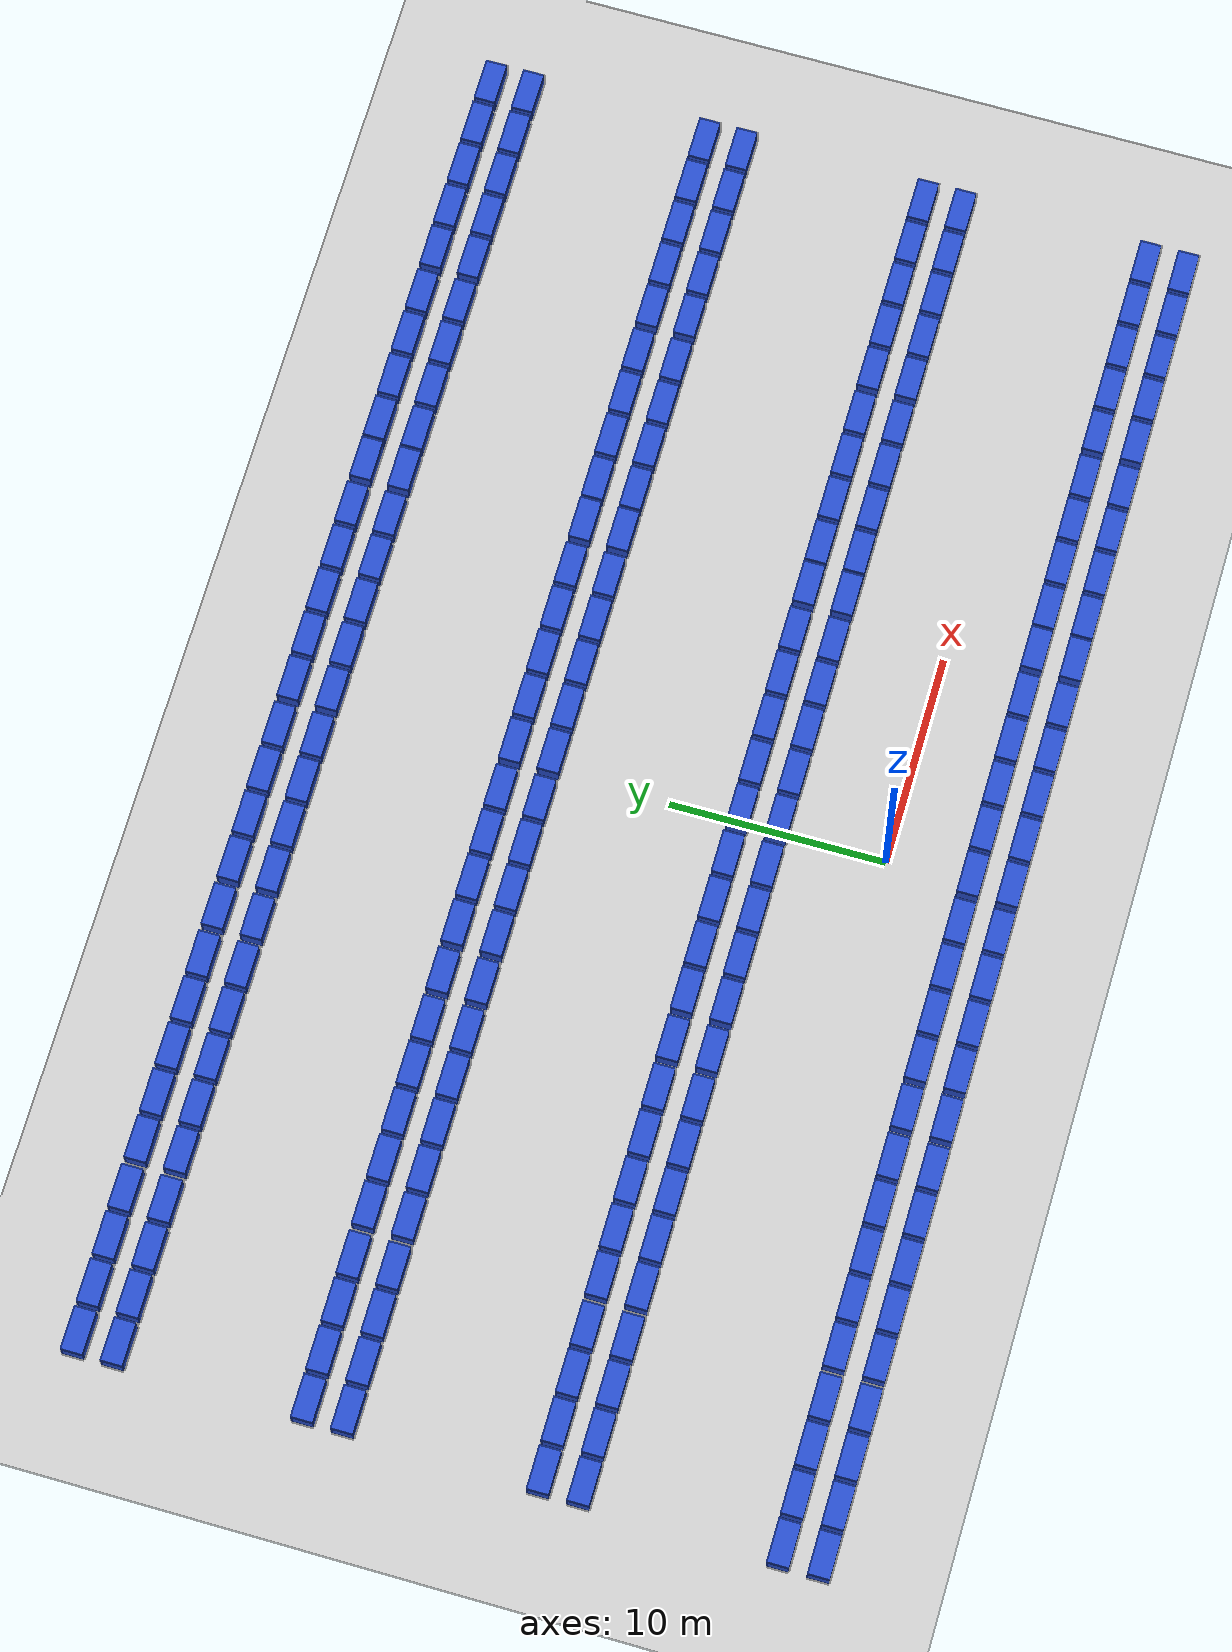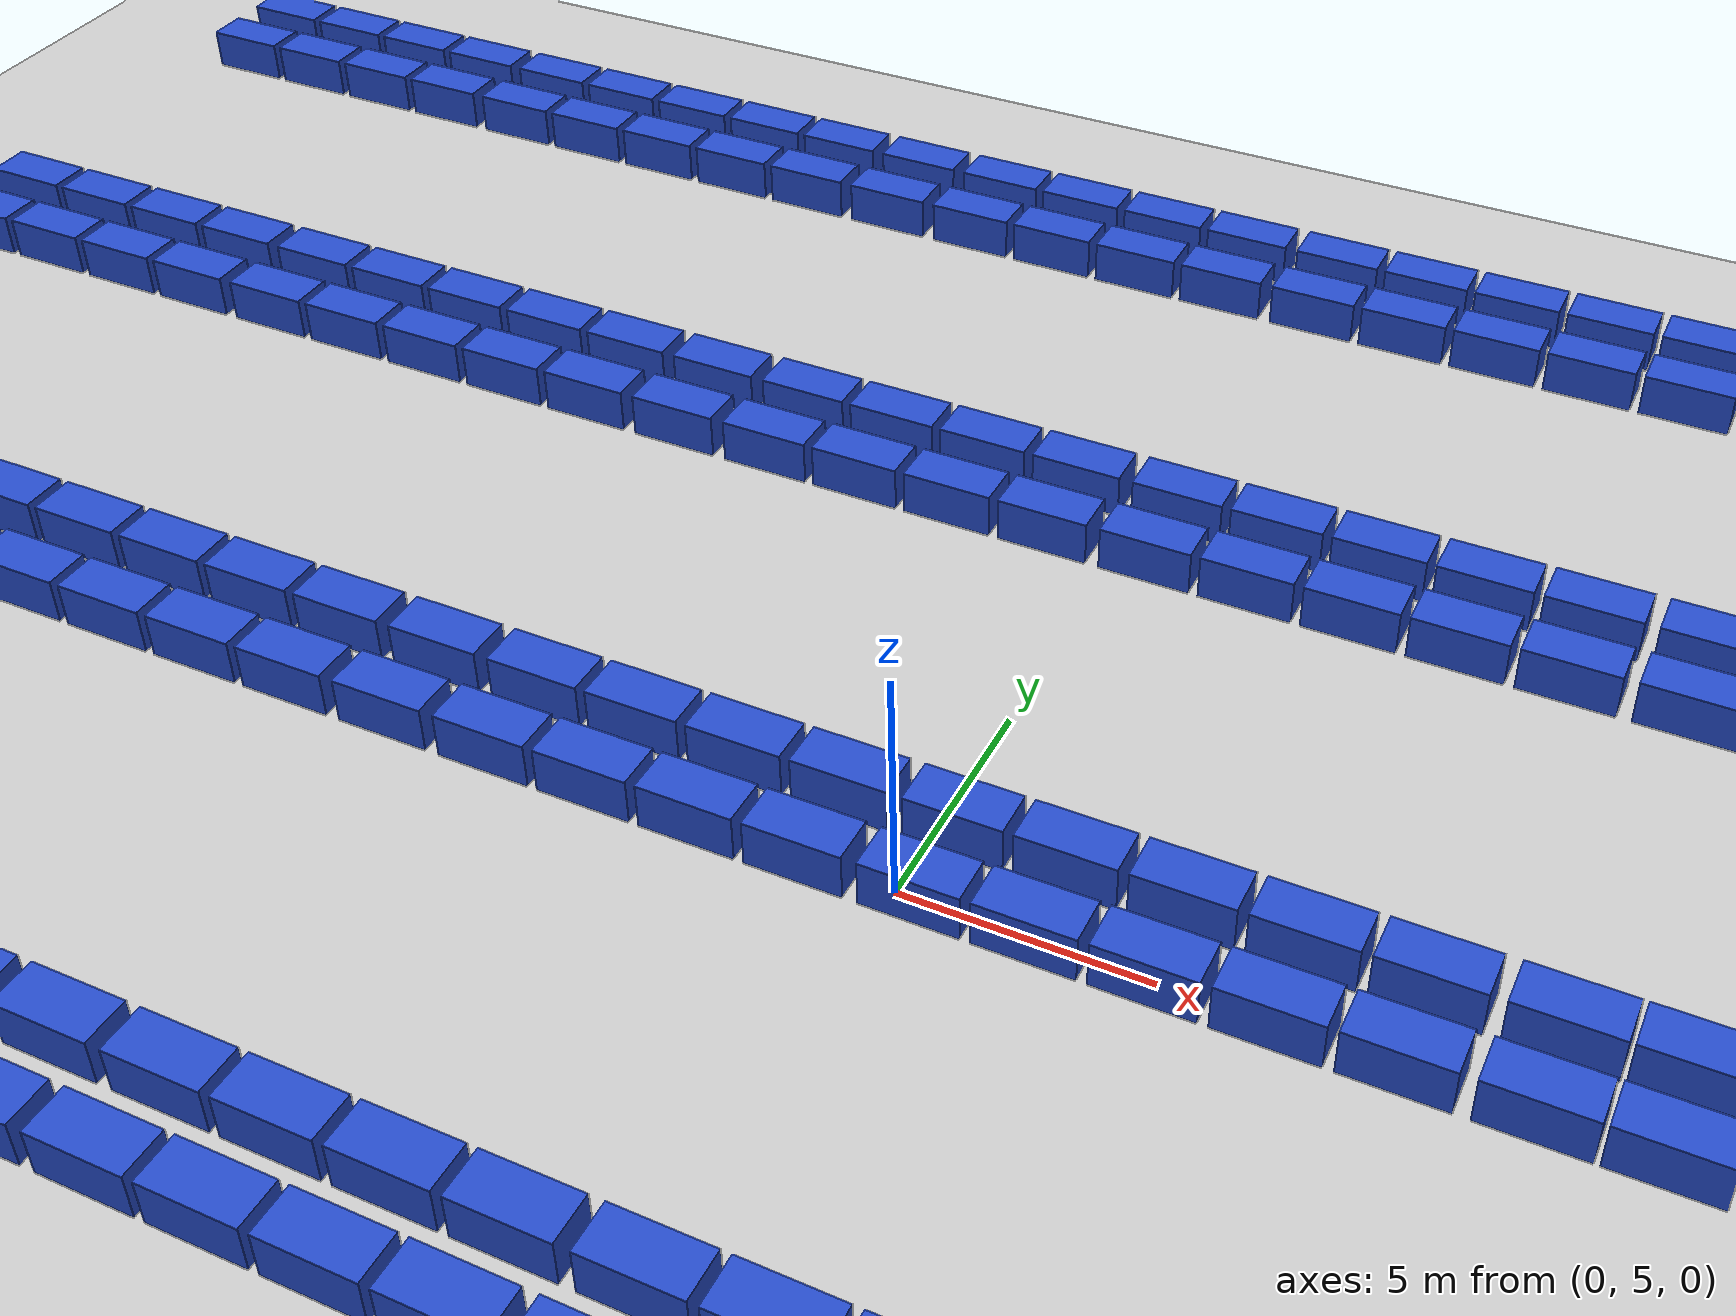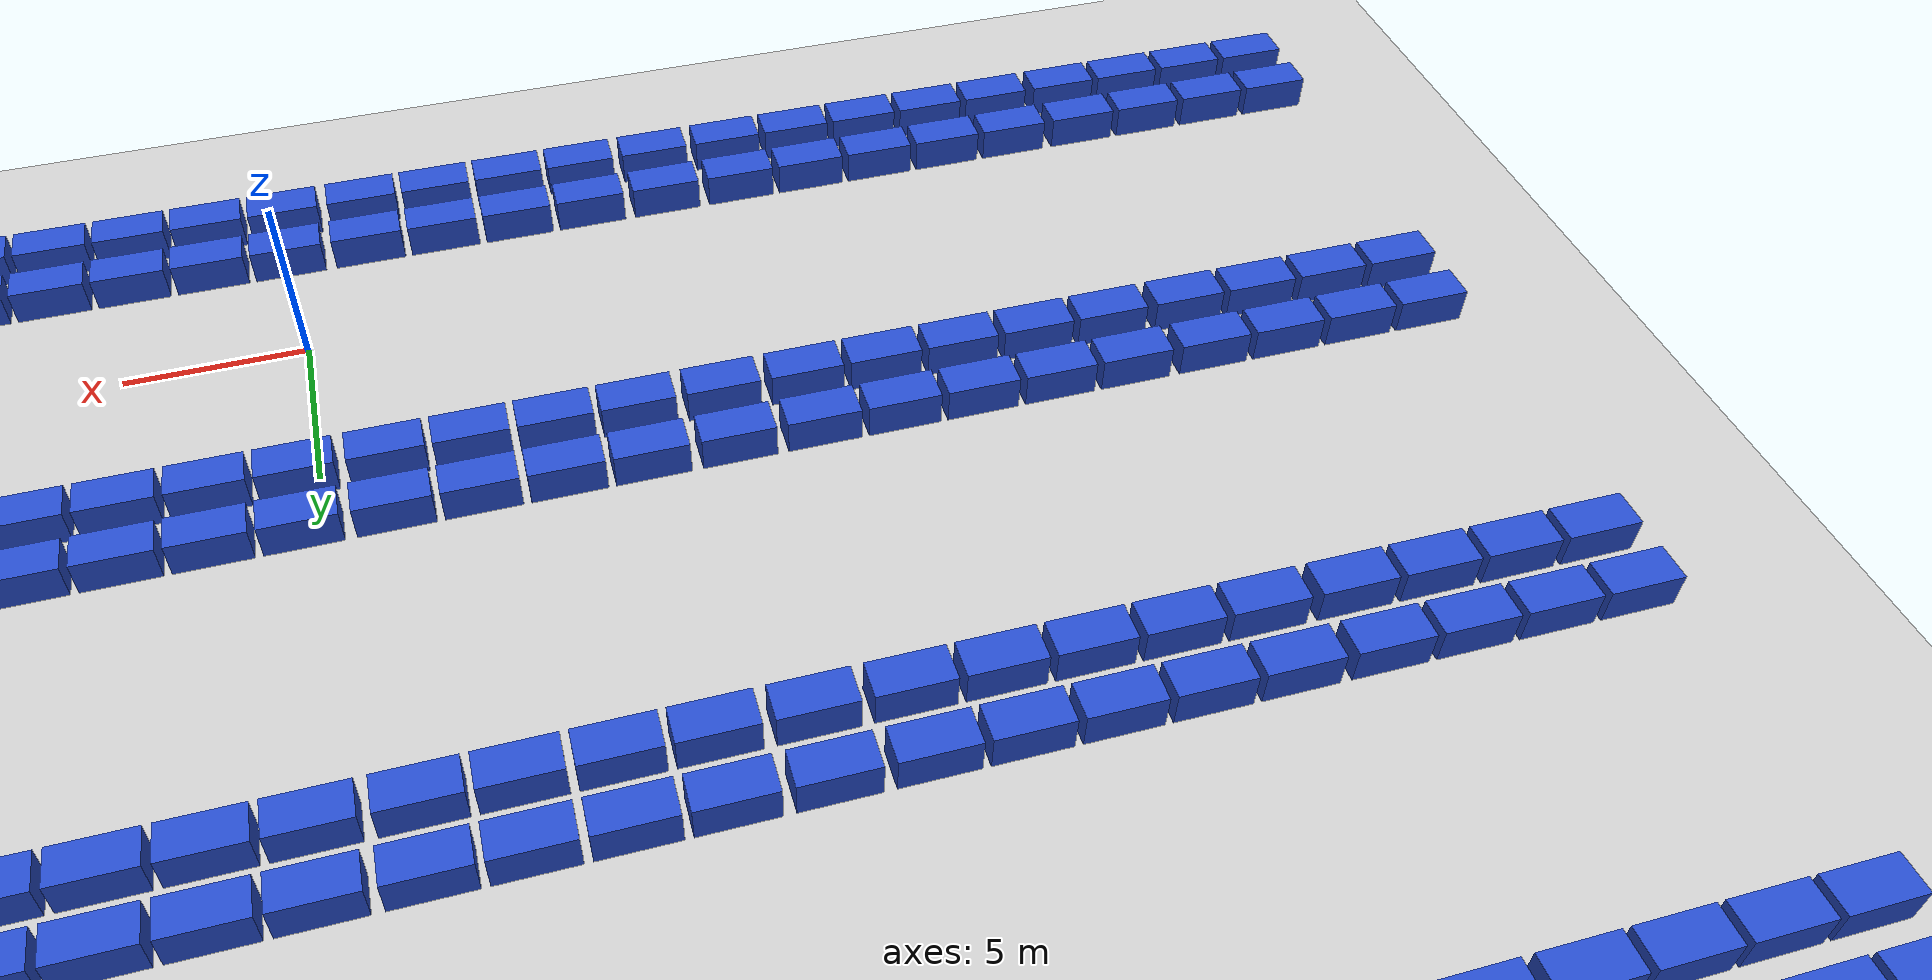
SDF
<sdf version="1.6">
 <world name="default">
  <light name="sun" type="directional">
   <pose>0 0 10 0 -0 0</pose>
   <diffuse>0.8 0.8 0.8 1</diffuse>
   <specular>0.2 0.2 0.2 1</specular>
   <attenuation>
    <range>1000</range>
    <constant>0.9</constant>
    <linear>0.01</linear>
    <quadratic>0.001</quadratic>
   </attenuation>
   <direction>-0.5 0.1 -0.9</direction>
  </light>
  <model name="ground_plane">
   <static>1</static>
   <link name="link">
    <collision name="collision">
     <geometry><plane><normal>0 0 1</normal><size>100 100</size></plane></geometry>
     <surface><friction><ode><mu>100</mu><mu2>50</mu2></ode></friction></surface>
    </collision>
    <visual name="visual">
     <cast_shadows>0</cast_shadows>
     <geometry><plane><normal>0 0 1</normal><size>100 100</size></plane></geometry>
     <material>
      <script><uri>file://media/materials/scripts/gazebo.material</uri><name>Gazebo/Grey</name></script>
     </material>
    </visual>
   </link>
  </model>
  <physics name="default_physics" default="0" type="ode">
   <max_step_size>0.01</max_step_size>
   <real_time_factor>1</real_time_factor>
   <real_time_update_rate>0</real_time_update_rate>
  </physics>
  <gravity>0 0 -9.8</gravity>
  <magnetic_field>6e-06 2.3e-05 -4.2e-05</magnetic_field>
  <atmosphere type="adiabatic"/>
  <scene><ambient>0.4 0.4 0.4 1</ambient><background>0.7 0.7 0.7 1</background><shadows>1</shadows></scene>
  <spherical_coordinates>
   <surface_model>EARTH_WGS84</surface_model>
   <latitude_deg>0</latitude_deg>
   <longitude_deg>0</longitude_deg>
   <elevation>0</elevation>
   <heading_deg>0</heading_deg>
  </spherical_coordinates>
  <model name="box0">
   <link name="blue_box">
    <inertial>
     <pose>2 0 0 0 -0 0</pose>
     <mass>1</mass>
     <inertia><ixx>0.17</ixx><ixy>0</ixy><ixz>0</ixz><iyy>0.42</iyy><iyz>0</iyz><izz>0.42</izz></inertia>
    </inertial>
    <collision name="blue_box_collision">
     <pose>2 0 1 0 -0 0</pose>
     <geometry><box><size>2 1 1</size></box></geometry>
    </collision>
    <visual name="blue_box_visual">
     <pose>2 0 1 0 -0 0</pose>
     <geometry><box><size>2 1 1</size></box></geometry>
     <material>
      <script><name>Gazebo/Blue</name><uri>file://media/materials/scripts/gazebo.material</uri></script>
     </material>
    </visual>
    <gravity>0</gravity>
   </link>
   <pose>-32.4 27.7996 -0.500378 -0.000755 0 0</pose>
  </model>
  <model name="box1">
   <link name="blue_box">
    <inertial>
     <pose>2 0 0 0 -0 0</pose>
     <mass>1</mass>
     <inertia><ixx>0.17</ixx><ixy>0</ixy><ixz>0</ixz><iyy>0.42</iyy><iyz>0</iyz><izz>0.42</izz></inertia>
    </inertial>
    <collision name="blue_box_collision">
     <pose>2 0 1 0 -0 0</pose>
     <geometry><box><size>2 1 1</size></box></geometry>
    </collision>
    <visual name="blue_box_visual">
     <pose>2 0 1 0 -0 0</pose>
     <geometry><box><size>2 1 1</size></box></geometry>
     <material>
      <script><name>Gazebo/Blue</name><uri>file://media/materials/scripts/gazebo.material</uri></script>
     </material>
    </visual>
    <gravity>0</gravity>
   </link>
   <pose>-30.2 27.7996 -0.500378 -0.000755 0 0</pose>
  </model>
  <model name="box2">
   <link name="blue_box">
    <inertial>
     <pose>2 0 0 0 -0 0</pose>
     <mass>1</mass>
     <inertia><ixx>0.17</ixx><ixy>0</ixy><ixz>0</ixz><iyy>0.42</iyy><iyz>0</iyz><izz>0.42</izz></inertia>
    </inertial>
    <collision name="blue_box_collision">
     <pose>2 0 1 0 -0 0</pose>
     <geometry><box><size>2 1 1</size></box></geometry>
    </collision>
    <visual name="blue_box_visual">
     <pose>2 0 1 0 -0 0</pose>
     <geometry><box><size>2 1 1</size></box></geometry>
     <material>
      <script><name>Gazebo/Blue</name><uri>file://media/materials/scripts/gazebo.material</uri></script>
     </material>
    </visual>
    <gravity>0</gravity>
   </link>
   <pose>-28 27.7996 -0.500378 -0.000755 0 0</pose>
  </model>
  <model name="box3">
   <link name="blue_box">
    <inertial>
     <pose>2 0 0 0 -0 0</pose>
     <mass>1</mass>
     <inertia><ixx>0.17</ixx><ixy>0</ixy><ixz>0</ixz><iyy>0.42</iyy><iyz>0</iyz><izz>0.42</izz></inertia>
    </inertial>
    <collision name="blue_box_collision">
     <pose>2 0 1 0 -0 0</pose>
     <geometry><box><size>2 1 1</size></box></geometry>
    </collision>
    <visual name="blue_box_visual">
     <pose>2 0 1 0 -0 0</pose>
     <geometry><box><size>2 1 1</size></box></geometry>
     <material>
      <script><name>Gazebo/Blue</name><uri>file://media/materials/scripts/gazebo.material</uri></script>
     </material>
    </visual>
    <gravity>0</gravity>
   </link>
   <pose>-25.8 27.7996 -0.500378 -0.000755 0 0</pose>
  </model>
  <model name="box4">
   <link name="blue_box">
    <inertial>
     <pose>2 0 0 0 -0 0</pose>
     <mass>1</mass>
     <inertia><ixx>0.17</ixx><ixy>0</ixy><ixz>0</ixz><iyy>0.42</iyy><iyz>0</iyz><izz>0.42</izz></inertia>
    </inertial>
    <collision name="blue_box_collision">
     <pose>2 0 1 0 -0 0</pose>
     <geometry><box><size>2 1 1</size></box></geometry>
    </collision>
    <visual name="blue_box_visual">
     <pose>2 0 1 0 -0 0</pose>
     <geometry><box><size>2 1 1</size></box></geometry>
     <material>
      <script><name>Gazebo/Blue</name><uri>file://media/materials/scripts/gazebo.material</uri></script>
     </material>
    </visual>
    <gravity>0</gravity>
   </link>
   <pose>-23.5 27.7996 -0.500378 -0.000755 0 0</pose>
  </model>
  <model name="box5">
   <link name="blue_box">
    <inertial>
     <pose>2 0 0 0 -0 0</pose>
     <mass>1</mass>
     <inertia><ixx>0.17</ixx><ixy>0</ixy><ixz>0</ixz><iyy>0.42</iyy><iyz>0</iyz><izz>0.42</izz></inertia>
    </inertial>
    <collision name="blue_box_collision">
     <pose>2 0 1 0 -0 0</pose>
     <geometry><box><size>2 1 1</size></box></geometry>
    </collision>
    <visual name="blue_box_visual">
     <pose>2 0 1 0 -0 0</pose>
     <geometry><box><size>2 1 1</size></box></geometry>
     <material>
      <script><name>Gazebo/Blue</name><uri>file://media/materials/scripts/gazebo.material</uri></script>
     </material>
    </visual>
    <gravity>0</gravity>
   </link>
   <pose>-21.3 27.7996 -0.500378 -0.000755 0 0</pose>
  </model>
  <model name="box6">
   <link name="blue_box">
    <inertial>
     <pose>2 0 0 0 -0 0</pose>
     <mass>1</mass>
     <inertia><ixx>0.17</ixx><ixy>0</ixy><ixz>0</ixz><iyy>0.42</iyy><iyz>0</iyz><izz>0.42</izz></inertia>
    </inertial>
    <collision name="blue_box_collision">
     <pose>2 0 1 0 -0 0</pose>
     <geometry><box><size>2 1 1</size></box></geometry>
    </collision>
    <visual name="blue_box_visual">
     <pose>2 0 1 0 -0 0</pose>
     <geometry><box><size>2 1 1</size></box></geometry>
     <material>
      <script><name>Gazebo/Blue</name><uri>file://media/materials/scripts/gazebo.material</uri></script>
     </material>
    </visual>
    <gravity>0</gravity>
   </link>
   <pose>-19.1 27.7996 -0.500378 -0.000755 0 0</pose>
  </model>
  <model name="box7">
   <link name="blue_box">
    <inertial>
     <pose>2 0 0 0 -0 0</pose>
     <mass>1</mass>
     <inertia><ixx>0.17</ixx><ixy>0</ixy><ixz>0</ixz><iyy>0.42</iyy><iyz>0</iyz><izz>0.42</izz></inertia>
    </inertial>
    <collision name="blue_box_collision">
     <pose>2 0 1 0 -0 0</pose>
     <geometry><box><size>2 1 1</size></box></geometry>
    </collision>
    <visual name="blue_box_visual">
     <pose>2 0 1 0 -0 0</pose>
     <geometry><box><size>2 1 1</size></box></geometry>
     <material>
      <script><name>Gazebo/Blue</name><uri>file://media/materials/scripts/gazebo.material</uri></script>
     </material>
    </visual>
    <gravity>0</gravity>
   </link>
   <pose>-16.9 27.7996 -0.500378 -0.000755 0 0</pose>
  </model>
  <model name="box8">
   <link name="blue_box">
    <inertial>
     <pose>2 0 0 0 -0 0</pose>
     <mass>1</mass>
     <inertia><ixx>0.17</ixx><ixy>0</ixy><ixz>0</ixz><iyy>0.42</iyy><iyz>0</iyz><izz>0.42</izz></inertia>
    </inertial>
    <collision name="blue_box_collision">
     <pose>2 0 1 0 -0 0</pose>
     <geometry><box><size>2 1 1</size></box></geometry>
    </collision>
    <visual name="blue_box_visual">
     <pose>2 0 1 0 -0 0</pose>
     <geometry><box><size>2 1 1</size></box></geometry>
     <material>
      <script><name>Gazebo/Blue</name><uri>file://media/materials/scripts/gazebo.material</uri></script>
     </material>
    </visual>
    <gravity>0</gravity>
   </link>
   <pose>-14.7 27.7996 -0.500378 -0.000755 0 0</pose>
  </model>
  <model name="box9">
   <link name="blue_box">
    <inertial>
     <pose>2 0 0 0 -0 0</pose>
     <mass>1</mass>
     <inertia><ixx>0.17</ixx><ixy>0</ixy><ixz>0</ixz><iyy>0.42</iyy><iyz>0</iyz><izz>0.42</izz></inertia>
    </inertial>
    <collision name="blue_box_collision">
     <pose>2 0 1 0 -0 0</pose>
     <geometry><box><size>2 1 1</size></box></geometry>
    </collision>
    <visual name="blue_box_visual">
     <pose>2 0 1 0 -0 0</pose>
     <geometry><box><size>2 1 1</size></box></geometry>
     <material>
      <script><name>Gazebo/Blue</name><uri>file://media/materials/scripts/gazebo.material</uri></script>
     </material>
    </visual>
    <gravity>0</gravity>
   </link>
   <pose>-12.4 27.7996 -0.500378 -0.000755 0 0</pose>
  </model>
  <model name="box10">
   <link name="blue_box">
    <inertial>
     <pose>2 0 0 0 -0 0</pose>
     <mass>1</mass>
     <inertia><ixx>0.17</ixx><ixy>0</ixy><ixz>0</ixz><iyy>0.42</iyy><iyz>0</iyz><izz>0.42</izz></inertia>
    </inertial>
    <collision name="blue_box_collision">
     <pose>2 0 1 0 -0 0</pose>
     <geometry><box><size>2 1 1</size></box></geometry>
    </collision>
    <visual name="blue_box_visual">
     <pose>2 0 1 0 -0 0</pose>
     <geometry><box><size>2 1 1</size></box></geometry>
     <material>
      <script><name>Gazebo/Blue</name><uri>file://media/materials/scripts/gazebo.material</uri></script>
     </material>
    </visual>
    <gravity>0</gravity>
   </link>
   <pose>-10.1 27.7996 -0.500378 -0.000755 0 0</pose>
  </model>
  <model name="box11">
   <link name="blue_box">
    <inertial>
     <pose>2 0 0 0 -0 0</pose>
     <mass>1</mass>
     <inertia><ixx>0.17</ixx><ixy>0</ixy><ixz>0</ixz><iyy>0.42</iyy><iyz>0</iyz><izz>0.42</izz></inertia>
    </inertial>
    <collision name="blue_box_collision">
     <pose>2 0 1 0 -0 0</pose>
     <geometry><box><size>2 1 1</size></box></geometry>
    </collision>
    <visual name="blue_box_visual">
     <pose>2 0 1 0 -0 0</pose>
     <geometry><box><size>2 1 1</size></box></geometry>
     <material>
      <script><name>Gazebo/Blue</name><uri>file://media/materials/scripts/gazebo.material</uri></script>
     </material>
    </visual>
    <gravity>0</gravity>
   </link>
   <pose>-7.89999 27.7996 -0.500378 -0.000755 0 0</pose>
  </model>
  <model name="box12">
   <link name="blue_box">
    <inertial>
     <pose>2 0 0 0 -0 0</pose>
     <mass>1</mass>
     <inertia><ixx>0.17</ixx><ixy>0</ixy><ixz>0</ixz><iyy>0.42</iyy><iyz>0</iyz><izz>0.42</izz></inertia>
    </inertial>
    <collision name="blue_box_collision">
     <pose>2 0 1 0 -0 0</pose>
     <geometry><box><size>2 1 1</size></box></geometry>
    </collision>
    <visual name="blue_box_visual">
     <pose>2 0 1 0 -0 0</pose>
     <geometry><box><size>2 1 1</size></box></geometry>
     <material>
      <script><name>Gazebo/Blue</name><uri>file://media/materials/scripts/gazebo.material</uri></script>
     </material>
    </visual>
    <gravity>0</gravity>
   </link>
   <pose>-5.70001 27.7996 -0.500378 -0.000755 0 0</pose>
  </model>
  <model name="box13">
   <link name="blue_box">
    <inertial>
     <pose>2 0 0 0 -0 0</pose>
     <mass>1</mass>
     <inertia><ixx>0.17</ixx><ixy>0</ixy><ixz>0</ixz><iyy>0.42</iyy><iyz>0</iyz><izz>0.42</izz></inertia>
    </inertial>
    <collision name="blue_box_collision">
     <pose>2 0 1 0 -0 0</pose>
     <geometry><box><size>2 1 1</size></box></geometry>
    </collision>
    <visual name="blue_box_visual">
     <pose>2 0 1 0 -0 0</pose>
     <geometry><box><size>2 1 1</size></box></geometry>
     <material>
      <script><name>Gazebo/Blue</name><uri>file://media/materials/scripts/gazebo.material</uri></script>
     </material>
    </visual>
    <gravity>0</gravity>
   </link>
   <pose>-3.49999 27.7996 -0.500378 -0.000755 0 0</pose>
  </model>
  <model name="box14">
   <link name="blue_box">
    <inertial>
     <pose>2 0 0 0 -0 0</pose>
     <mass>1</mass>
     <inertia><ixx>0.17</ixx><ixy>0</ixy><ixz>0</ixz><iyy>0.42</iyy><iyz>0</iyz><izz>0.42</izz></inertia>
    </inertial>
    <collision name="blue_box_collision">
     <pose>2 0 1 0 -0 0</pose>
     <geometry><box><size>2 1 1</size></box></geometry>
    </collision>
    <visual name="blue_box_visual">
     <pose>2 0 1 0 -0 0</pose>
     <geometry><box><size>2 1 1</size></box></geometry>
     <material>
      <script><name>Gazebo/Blue</name><uri>file://media/materials/scripts/gazebo.material</uri></script>
     </material>
    </visual>
    <gravity>0</gravity>
   </link>
   <pose>-1.20001 27.7996 -0.500378 -0.000755 0 0</pose>
  </model>
  <model name="box15">
   <link name="blue_box">
    <inertial>
     <pose>2 0 0 0 -0 0</pose>
     <mass>1</mass>
     <inertia><ixx>0.17</ixx><ixy>0</ixy><ixz>0</ixz><iyy>0.42</iyy><iyz>0</iyz><izz>0.42</izz></inertia>
    </inertial>
    <collision name="blue_box_collision">
     <pose>2 0 1 0 -0 0</pose>
     <geometry><box><size>2 1 1</size></box></geometry>
    </collision>
    <visual name="blue_box_visual">
     <pose>2 0 1 0 -0 0</pose>
     <geometry><box><size>2 1 1</size></box></geometry>
     <material>
      <script><name>Gazebo/Blue</name><uri>file://media/materials/scripts/gazebo.material</uri></script>
     </material>
    </visual>
    <gravity>0</gravity>
   </link>
   <pose>1.00001 27.7996 -0.500378 -0.000755 0 0</pose>
  </model>
  <model name="box16">
   <link name="blue_box">
    <inertial>
     <pose>2 0 0 0 -0 0</pose>
     <mass>1</mass>
     <inertia><ixx>0.17</ixx><ixy>0</ixy><ixz>0</ixz><iyy>0.42</iyy><iyz>0</iyz><izz>0.42</izz></inertia>
    </inertial>
    <collision name="blue_box_collision">
     <pose>2 0 1 0 -0 0</pose>
     <geometry><box><size>2 1 1</size></box></geometry>
    </collision>
    <visual name="blue_box_visual">
     <pose>2 0 1 0 -0 0</pose>
     <geometry><box><size>2 1 1</size></box></geometry>
     <material>
      <script><name>Gazebo/Blue</name><uri>file://media/materials/scripts/gazebo.material</uri></script>
     </material>
    </visual>
    <gravity>0</gravity>
   </link>
   <pose>3.19999 27.7996 -0.500378 -0.000755 0 0</pose>
  </model>
  <model name="box17">
   <link name="blue_box">
    <inertial>
     <pose>2 0 0 0 -0 0</pose>
     <mass>1</mass>
     <inertia><ixx>0.17</ixx><ixy>0</ixy><ixz>0</ixz><iyy>0.42</iyy><iyz>0</iyz><izz>0.42</izz></inertia>
    </inertial>
    <collision name="blue_box_collision">
     <pose>2 0 1 0 -0 0</pose>
     <geometry><box><size>2 1 1</size></box></geometry>
    </collision>
    <visual name="blue_box_visual">
     <pose>2 0 1 0 -0 0</pose>
     <geometry><box><size>2 1 1</size></box></geometry>
     <material>
      <script><name>Gazebo/Blue</name><uri>file://media/materials/scripts/gazebo.material</uri></script>
     </material>
    </visual>
    <gravity>0</gravity>
   </link>
   <pose>5.40001 27.7996 -0.500378 -0.000755 0 0</pose>
  </model>
  <model name="box18">
   <link name="blue_box">
    <inertial>
     <pose>2 0 0 0 -0 0</pose>
     <mass>1</mass>
     <inertia><ixx>0.17</ixx><ixy>0</ixy><ixz>0</ixz><iyy>0.42</iyy><iyz>0</iyz><izz>0.42</izz></inertia>
    </inertial>
    <collision name="blue_box_collision">
     <pose>2 0 1 0 -0 0</pose>
     <geometry><box><size>2 1 1</size></box></geometry>
    </collision>
    <visual name="blue_box_visual">
     <pose>2 0 1 0 -0 0</pose>
     <geometry><box><size>2 1 1</size></box></geometry>
     <material>
      <script><name>Gazebo/Blue</name><uri>file://media/materials/scripts/gazebo.material</uri></script>
     </material>
    </visual>
    <gravity>0</gravity>
   </link>
   <pose>7.59999 27.7996 -0.500378 -0.000755 0 0</pose>
  </model>
  <model name="box19">
   <link name="blue_box">
    <inertial>
     <pose>2 0 0 0 -0 0</pose>
     <mass>1</mass>
     <inertia><ixx>0.17</ixx><ixy>0</ixy><ixz>0</ixz><iyy>0.42</iyy><iyz>0</iyz><izz>0.42</izz></inertia>
    </inertial>
    <collision name="blue_box_collision">
     <pose>2 0 1 0 -0 0</pose>
     <geometry><box><size>2 1 1</size></box></geometry>
    </collision>
    <visual name="blue_box_visual">
     <pose>2 0 1 0 -0 0</pose>
     <geometry><box><size>2 1 1</size></box></geometry>
     <material>
      <script><name>Gazebo/Blue</name><uri>file://media/materials/scripts/gazebo.material</uri></script>
     </material>
    </visual>
    <gravity>0</gravity>
   </link>
   <pose>9.89999 27.7996 -0.500378 -0.000755 0 0</pose>
  </model>
  <model name="box20">
   <link name="blue_box">
    <inertial>
     <pose>2 0 0 0 -0 0</pose>
     <mass>1</mass>
     <inertia><ixx>0.17</ixx><ixy>0</ixy><ixz>0</ixz><iyy>0.42</iyy><iyz>0</iyz><izz>0.42</izz></inertia>
    </inertial>
    <collision name="blue_box_collision">
     <pose>2 0 1 0 -0 0</pose>
     <geometry><box><size>2 1 1</size></box></geometry>
    </collision>
    <visual name="blue_box_visual">
     <pose>2 0 1 0 -0 0</pose>
     <geometry><box><size>2 1 1</size></box></geometry>
     <material>
      <script><name>Gazebo/Blue</name><uri>file://media/materials/scripts/gazebo.material</uri></script>
     </material>
    </visual>
    <gravity>0</gravity>
   </link>
   <pose>12 27.7996 -0.500378 -0.000755 0 0</pose>
  </model>
  <model name="box21">
   <link name="blue_box">
    <inertial>
     <pose>2 0 0 0 -0 0</pose>
     <mass>1</mass>
     <inertia><ixx>0.17</ixx><ixy>0</ixy><ixz>0</ixz><iyy>0.42</iyy><iyz>0</iyz><izz>0.42</izz></inertia>
    </inertial>
    <collision name="blue_box_collision">
     <pose>2 0 1 0 -0 0</pose>
     <geometry><box><size>2 1 1</size></box></geometry>
    </collision>
    <visual name="blue_box_visual">
     <pose>2 0 1 0 -0 0</pose>
     <geometry><box><size>2 1 1</size></box></geometry>
     <material>
      <script><name>Gazebo/Blue</name><uri>file://media/materials/scripts/gazebo.material</uri></script>
     </material>
    </visual>
    <gravity>0</gravity>
   </link>
   <pose>14.2 27.8004 -0.500378 0.000755 -0 0</pose>
  </model>
  <model name="box22">
   <link name="blue_box">
    <inertial>
     <pose>2 0 0 0 -0 0</pose>
     <mass>1</mass>
     <inertia><ixx>0.17</ixx><ixy>0</ixy><ixz>0</ixz><iyy>0.42</iyy><iyz>0</iyz><izz>0.42</izz></inertia>
    </inertial>
    <collision name="blue_box_collision">
     <pose>2 0 1 0 -0 0</pose>
     <geometry><box><size>2 1 1</size></box></geometry>
    </collision>
    <visual name="blue_box_visual">
     <pose>2 0 1 0 -0 0</pose>
     <geometry><box><size>2 1 1</size></box></geometry>
     <material>
      <script><name>Gazebo/Blue</name><uri>file://media/materials/scripts/gazebo.material</uri></script>
     </material>
    </visual>
    <gravity>0</gravity>
   </link>
   <pose>16.4 27.7996 -0.500378 -0.000755 0 0</pose>
  </model>
  <model name="box23">
   <link name="blue_box">
    <inertial>
     <pose>2 0 0 0 -0 0</pose>
     <mass>1</mass>
     <inertia><ixx>0.17</ixx><ixy>0</ixy><ixz>0</ixz><iyy>0.42</iyy><iyz>0</iyz><izz>0.42</izz></inertia>
    </inertial>
    <collision name="blue_box_collision">
     <pose>2 0 1 0 -0 0</pose>
     <geometry><box><size>2 1 1</size></box></geometry>
    </collision>
    <visual name="blue_box_visual">
     <pose>2 0 1 0 -0 0</pose>
     <geometry><box><size>2 1 1</size></box></geometry>
     <material>
      <script><name>Gazebo/Blue</name><uri>file://media/materials/scripts/gazebo.material</uri></script>
     </material>
    </visual>
    <gravity>0</gravity>
   </link>
   <pose>18.6 27.7996 -0.500378 -0.000755 0 0</pose>
  </model>
  <model name="box24">
   <link name="blue_box">
    <inertial>
     <pose>2 0 0 0 -0 0</pose>
     <mass>1</mass>
     <inertia><ixx>0.17</ixx><ixy>0</ixy><ixz>0</ixz><iyy>0.42</iyy><iyz>0</iyz><izz>0.42</izz></inertia>
    </inertial>
    <collision name="blue_box_collision">
     <pose>2 0 1 0 -0 0</pose>
     <geometry><box><size>2 1 1</size></box></geometry>
    </collision>
    <visual name="blue_box_visual">
     <pose>2 0 1 0 -0 0</pose>
     <geometry><box><size>2 1 1</size></box></geometry>
     <material>
      <script><name>Gazebo/Blue</name><uri>file://media/materials/scripts/gazebo.material</uri></script>
     </material>
    </visual>
    <gravity>0</gravity>
   </link>
   <pose>20.9 27.7996 -0.500378 -0.000755 0 0</pose>
  </model>
  <model name="box25">
   <link name="blue_box">
    <inertial>
     <pose>2 0 0 0 -0 0</pose>
     <mass>1</mass>
     <inertia><ixx>0.17</ixx><ixy>0</ixy><ixz>0</ixz><iyy>0.42</iyy><iyz>0</iyz><izz>0.42</izz></inertia>
    </inertial>
    <collision name="blue_box_collision">
     <pose>2 0 1 0 -0 0</pose>
     <geometry><box><size>2 1 1</size></box></geometry>
    </collision>
    <visual name="blue_box_visual">
     <pose>2 0 1 0 -0 0</pose>
     <geometry><box><size>2 1 1</size></box></geometry>
     <material>
      <script><name>Gazebo/Blue</name><uri>file://media/materials/scripts/gazebo.material</uri></script>
     </material>
    </visual>
    <gravity>0</gravity>
   </link>
   <pose>23.1 27.7996 -0.500378 -0.000755 0 0</pose>
  </model>
  <model name="box26">
   <link name="blue_box">
    <inertial>
     <pose>2 0 0 0 -0 0</pose>
     <mass>1</mass>
     <inertia><ixx>0.17</ixx><ixy>0</ixy><ixz>0</ixz><iyy>0.42</iyy><iyz>0</iyz><izz>0.42</izz></inertia>
    </inertial>
    <collision name="blue_box_collision">
     <pose>2 0 1 0 -0 0</pose>
     <geometry><box><size>2 1 1</size></box></geometry>
    </collision>
    <visual name="blue_box_visual">
     <pose>2 0 1 0 -0 0</pose>
     <geometry><box><size>2 1 1</size></box></geometry>
     <material>
      <script><name>Gazebo/Blue</name><uri>file://media/materials/scripts/gazebo.material</uri></script>
     </material>
    </visual>
    <gravity>0</gravity>
   </link>
   <pose>25.3 27.7996 -0.500378 -0.000755 0 0</pose>
  </model>
  <model name="box27">
   <link name="blue_box">
    <inertial>
     <pose>2 0 0 0 -0 0</pose>
     <mass>1</mass>
     <inertia><ixx>0.17</ixx><ixy>0</ixy><ixz>0</ixz><iyy>0.42</iyy><iyz>0</iyz><izz>0.42</izz></inertia>
    </inertial>
    <collision name="blue_box_collision">
     <pose>2 0 1 0 -0 0</pose>
     <geometry><box><size>2 1 1</size></box></geometry>
    </collision>
    <visual name="blue_box_visual">
     <pose>2 0 1 0 -0 0</pose>
     <geometry><box><size>2 1 1</size></box></geometry>
     <material>
      <script><name>Gazebo/Blue</name><uri>file://media/materials/scripts/gazebo.material</uri></script>
     </material>
    </visual>
    <gravity>0</gravity>
   </link>
   <pose>27.5 27.7996 -0.500378 -0.000755 0 0</pose>
  </model>
  <model name="box28">
   <link name="blue_box">
    <inertial>
     <pose>2 0 0 0 -0 0</pose>
     <mass>1</mass>
     <inertia><ixx>0.17</ixx><ixy>0</ixy><ixz>0</ixz><iyy>0.42</iyy><iyz>0</iyz><izz>0.42</izz></inertia>
    </inertial>
    <collision name="blue_box_collision">
     <pose>2 0 1 0 -0 0</pose>
     <geometry><box><size>2 1 1</size></box></geometry>
    </collision>
    <visual name="blue_box_visual">
     <pose>2 0 1 0 -0 0</pose>
     <geometry><box><size>2 1 1</size></box></geometry>
     <material>
      <script><name>Gazebo/Blue</name><uri>file://media/materials/scripts/gazebo.material</uri></script>
     </material>
    </visual>
    <gravity>0</gravity>
   </link>
   <pose>29.7 27.7996 -0.500378 -0.000755 0 0</pose>
  </model>
  <model name="box29">
   <link name="blue_box">
    <inertial>
     <pose>2 0 0 0 -0 0</pose>
     <mass>1</mass>
     <inertia><ixx>0.17</ixx><ixy>0</ixy><ixz>0</ixz><iyy>0.42</iyy><iyz>0</iyz><izz>0.42</izz></inertia>
    </inertial>
    <collision name="blue_box_collision">
     <pose>2 0 1 0 -0 0</pose>
     <geometry><box><size>2 1 1</size></box></geometry>
    </collision>
    <visual name="blue_box_visual">
     <pose>2 0 1 0 -0 0</pose>
     <geometry><box><size>2 1 1</size></box></geometry>
     <material>
      <script><name>Gazebo/Blue</name><uri>file://media/materials/scripts/gazebo.material</uri></script>
     </material>
    </visual>
    <gravity>0</gravity>
   </link>
   <pose>-32.4 25.9996 -0.500378 -0.000755 0 0</pose>
  </model>
  <model name="box30">
   <link name="blue_box">
    <inertial>
     <pose>2 0 0 0 -0 0</pose>
     <mass>1</mass>
     <inertia><ixx>0.17</ixx><ixy>0</ixy><ixz>0</ixz><iyy>0.42</iyy><iyz>0</iyz><izz>0.42</izz></inertia>
    </inertial>
    <collision name="blue_box_collision">
     <pose>2 0 1 0 -0 0</pose>
     <geometry><box><size>2 1 1</size></box></geometry>
    </collision>
    <visual name="blue_box_visual">
     <pose>2 0 1 0 -0 0</pose>
     <geometry><box><size>2 1 1</size></box></geometry>
     <material>
      <script><name>Gazebo/Blue</name><uri>file://media/materials/scripts/gazebo.material</uri></script>
     </material>
    </visual>
    <gravity>0</gravity>
   </link>
   <pose>-30.2 26.0004 -0.500378 0.000755 -0 0</pose>
  </model>
  <model name="box31">
   <link name="blue_box">
    <inertial>
     <pose>2 0 0 0 -0 0</pose>
     <mass>1</mass>
     <inertia><ixx>0.17</ixx><ixy>0</ixy><ixz>0</ixz><iyy>0.42</iyy><iyz>0</iyz><izz>0.42</izz></inertia>
    </inertial>
    <collision name="blue_box_collision">
     <pose>2 0 1 0 -0 0</pose>
     <geometry><box><size>2 1 1</size></box></geometry>
    </collision>
    <visual name="blue_box_visual">
     <pose>2 0 1 0 -0 0</pose>
     <geometry><box><size>2 1 1</size></box></geometry>
     <material>
      <script><name>Gazebo/Blue</name><uri>file://media/materials/scripts/gazebo.material</uri></script>
     </material>
    </visual>
    <gravity>0</gravity>
   </link>
   <pose>-28 25.9996 -0.500378 -0.000755 0 0</pose>
  </model>
  <model name="box32">
   <link name="blue_box">
    <inertial>
     <pose>2 0 0 0 -0 0</pose>
     <mass>1</mass>
     <inertia><ixx>0.17</ixx><ixy>0</ixy><ixz>0</ixz><iyy>0.42</iyy><iyz>0</iyz><izz>0.42</izz></inertia>
    </inertial>
    <collision name="blue_box_collision">
     <pose>2 0 1 0 -0 0</pose>
     <geometry><box><size>2 1 1</size></box></geometry>
    </collision>
    <visual name="blue_box_visual">
     <pose>2 0 1 0 -0 0</pose>
     <geometry><box><size>2 1 1</size></box></geometry>
     <material>
      <script><name>Gazebo/Blue</name><uri>file://media/materials/scripts/gazebo.material</uri></script>
     </material>
    </visual>
    <gravity>0</gravity>
   </link>
   <pose>-25.8 25.9996 -0.500378 -0.000755 0 0</pose>
  </model>
  <model name="box33">
   <link name="blue_box">
    <inertial>
     <pose>2 0 0 0 -0 0</pose>
     <mass>1</mass>
     <inertia><ixx>0.17</ixx><ixy>0</ixy><ixz>0</ixz><iyy>0.42</iyy><iyz>0</iyz><izz>0.42</izz></inertia>
    </inertial>
    <collision name="blue_box_collision">
     <pose>2 0 1 0 -0 0</pose>
     <geometry><box><size>2 1 1</size></box></geometry>
    </collision>
    <visual name="blue_box_visual">
     <pose>2 0 1 0 -0 0</pose>
     <geometry><box><size>2 1 1</size></box></geometry>
     <material>
      <script><name>Gazebo/Blue</name><uri>file://media/materials/scripts/gazebo.material</uri></script>
     </material>
    </visual>
    <gravity>0</gravity>
   </link>
   <pose>-23.5 26.0004 -0.500378 0.000755 -0 0</pose>
  </model>
  <model name="box34">
   <link name="blue_box">
    <inertial>
     <pose>2 0 0 0 -0 0</pose>
     <mass>1</mass>
     <inertia><ixx>0.17</ixx><ixy>0</ixy><ixz>0</ixz><iyy>0.42</iyy><iyz>0</iyz><izz>0.42</izz></inertia>
    </inertial>
    <collision name="blue_box_collision">
     <pose>2 0 1 0 -0 0</pose>
     <geometry><box><size>2 1 1</size></box></geometry>
    </collision>
    <visual name="blue_box_visual">
     <pose>2 0 1 0 -0 0</pose>
     <geometry><box><size>2 1 1</size></box></geometry>
     <material>
      <script><name>Gazebo/Blue</name><uri>file://media/materials/scripts/gazebo.material</uri></script>
     </material>
    </visual>
    <gravity>0</gravity>
   </link>
   <pose>-21.3 26.0004 -0.500378 0.000755 -0 0</pose>
  </model>
  <model name="box35">
   <link name="blue_box">
    <inertial>
     <pose>2 0 0 0 -0 0</pose>
     <mass>1</mass>
     <inertia><ixx>0.17</ixx><ixy>0</ixy><ixz>0</ixz><iyy>0.42</iyy><iyz>0</iyz><izz>0.42</izz></inertia>
    </inertial>
    <collision name="blue_box_collision">
     <pose>2 0 1 0 -0 0</pose>
     <geometry><box><size>2 1 1</size></box></geometry>
    </collision>
    <visual name="blue_box_visual">
     <pose>2 0 1 0 -0 0</pose>
     <geometry><box><size>2 1 1</size></box></geometry>
     <material>
      <script><name>Gazebo/Blue</name><uri>file://media/materials/scripts/gazebo.material</uri></script>
     </material>
    </visual>
    <gravity>0</gravity>
   </link>
   <pose>-19.1 25.9996 -0.500378 -0.000755 0 0</pose>
  </model>
  <model name="box36">
   <link name="blue_box">
    <inertial>
     <pose>2 0 0 0 -0 0</pose>
     <mass>1</mass>
     <inertia><ixx>0.17</ixx><ixy>0</ixy><ixz>0</ixz><iyy>0.42</iyy><iyz>0</iyz><izz>0.42</izz></inertia>
    </inertial>
    <collision name="blue_box_collision">
     <pose>2 0 1 0 -0 0</pose>
     <geometry><box><size>2 1 1</size></box></geometry>
    </collision>
    <visual name="blue_box_visual">
     <pose>2 0 1 0 -0 0</pose>
     <geometry><box><size>2 1 1</size></box></geometry>
     <material>
      <script><name>Gazebo/Blue</name><uri>file://media/materials/scripts/gazebo.material</uri></script>
     </material>
    </visual>
    <gravity>0</gravity>
   </link>
   <pose>-16.9 25.9996 -0.500378 -0.000755 0 0</pose>
  </model>
  <model name="box37">
   <link name="blue_box">
    <inertial>
     <pose>2 0 0 0 -0 0</pose>
     <mass>1</mass>
     <inertia><ixx>0.17</ixx><ixy>0</ixy><ixz>0</ixz><iyy>0.42</iyy><iyz>0</iyz><izz>0.42</izz></inertia>
    </inertial>
    <collision name="blue_box_collision">
     <pose>2 0 1 0 -0 0</pose>
     <geometry><box><size>2 1 1</size></box></geometry>
    </collision>
    <visual name="blue_box_visual">
     <pose>2 0 1 0 -0 0</pose>
     <geometry><box><size>2 1 1</size></box></geometry>
     <material>
      <script><name>Gazebo/Blue</name><uri>file://media/materials/scripts/gazebo.material</uri></script>
     </material>
    </visual>
    <gravity>0</gravity>
   </link>
   <pose>-14.7 25.9996 -0.500378 -0.000755 0 0</pose>
  </model>
  <model name="box38">
   <link name="blue_box">
    <inertial>
     <pose>2 0 0 0 -0 0</pose>
     <mass>1</mass>
     <inertia><ixx>0.17</ixx><ixy>0</ixy><ixz>0</ixz><iyy>0.42</iyy><iyz>0</iyz><izz>0.42</izz></inertia>
    </inertial>
    <collision name="blue_box_collision">
     <pose>2 0 1 0 -0 0</pose>
     <geometry><box><size>2 1 1</size></box></geometry>
    </collision>
    <visual name="blue_box_visual">
     <pose>2 0 1 0 -0 0</pose>
     <geometry><box><size>2 1 1</size></box></geometry>
     <material>
      <script><name>Gazebo/Blue</name><uri>file://media/materials/scripts/gazebo.material</uri></script>
     </material>
    </visual>
    <gravity>0</gravity>
   </link>
   <pose>-12.4 25.9996 -0.500378 -0.000755 0 0</pose>
  </model>
  <model name="box39">
   <link name="blue_box">
    <inertial>
     <pose>2 0 0 0 -0 0</pose>
     <mass>1</mass>
     <inertia><ixx>0.17</ixx><ixy>0</ixy><ixz>0</ixz><iyy>0.42</iyy><iyz>0</iyz><izz>0.42</izz></inertia>
    </inertial>
    <collision name="blue_box_collision">
     <pose>2 0 1 0 -0 0</pose>
     <geometry><box><size>2 1 1</size></box></geometry>
    </collision>
    <visual name="blue_box_visual">
     <pose>2 0 1 0 -0 0</pose>
     <geometry><box><size>2 1 1</size></box></geometry>
     <material>
      <script><name>Gazebo/Blue</name><uri>file://media/materials/scripts/gazebo.material</uri></script>
     </material>
    </visual>
    <gravity>0</gravity>
   </link>
   <pose>-10.1 25.9996 -0.500378 -0.000755 0 0</pose>
  </model>
  <model name="box40">
   <link name="blue_box">
    <inertial>
     <pose>2 0 0 0 -0 0</pose>
     <mass>1</mass>
     <inertia><ixx>0.17</ixx><ixy>0</ixy><ixz>0</ixz><iyy>0.42</iyy><iyz>0</iyz><izz>0.42</izz></inertia>
    </inertial>
    <collision name="blue_box_collision">
     <pose>2 0 1 0 -0 0</pose>
     <geometry><box><size>2 1 1</size></box></geometry>
    </collision>
    <visual name="blue_box_visual">
     <pose>2 0 1 0 -0 0</pose>
     <geometry><box><size>2 1 1</size></box></geometry>
     <material>
      <script><name>Gazebo/Blue</name><uri>file://media/materials/scripts/gazebo.material</uri></script>
     </material>
    </visual>
    <gravity>0</gravity>
   </link>
   <pose>-7.90001 25.9996 -0.500378 -0.000755 0 0</pose>
  </model>
  <model name="box41">
   <link name="blue_box">
    <inertial>
     <pose>2 0 0 0 -0 0</pose>
     <mass>1</mass>
     <inertia><ixx>0.17</ixx><ixy>0</ixy><ixz>0</ixz><iyy>0.42</iyy><iyz>0</iyz><izz>0.42</izz></inertia>
    </inertial>
    <collision name="blue_box_collision">
     <pose>2 0 1 0 -0 0</pose>
     <geometry><box><size>2 1 1</size></box></geometry>
    </collision>
    <visual name="blue_box_visual">
     <pose>2 0 1 0 -0 0</pose>
     <geometry><box><size>2 1 1</size></box></geometry>
     <material>
      <script><name>Gazebo/Blue</name><uri>file://media/materials/scripts/gazebo.material</uri></script>
     </material>
    </visual>
    <gravity>0</gravity>
   </link>
   <pose>-5.69999 25.9996 -0.500378 -0.000755 0 0</pose>
  </model>
  <model name="box42">
   <link name="blue_box">
    <inertial>
     <pose>2 0 0 0 -0 0</pose>
     <mass>1</mass>
     <inertia><ixx>0.17</ixx><ixy>0</ixy><ixz>0</ixz><iyy>0.42</iyy><iyz>0</iyz><izz>0.42</izz></inertia>
    </inertial>
    <collision name="blue_box_collision">
     <pose>2 0 1 0 -0 0</pose>
     <geometry><box><size>2 1 1</size></box></geometry>
    </collision>
    <visual name="blue_box_visual">
     <pose>2 0 1 0 -0 0</pose>
     <geometry><box><size>2 1 1</size></box></geometry>
     <material>
      <script><name>Gazebo/Blue</name><uri>file://media/materials/scripts/gazebo.material</uri></script>
     </material>
    </visual>
    <gravity>0</gravity>
   </link>
   <pose>-3.50001 25.9996 -0.500378 -0.000755 0 0</pose>
  </model>
  <model name="box43">
   <link name="blue_box">
    <inertial>
     <pose>2 0 0 0 -0 0</pose>
     <mass>1</mass>
     <inertia><ixx>0.17</ixx><ixy>0</ixy><ixz>0</ixz><iyy>0.42</iyy><iyz>0</iyz><izz>0.42</izz></inertia>
    </inertial>
    <collision name="blue_box_collision">
     <pose>2 0 1 0 -0 0</pose>
     <geometry><box><size>2 1 1</size></box></geometry>
    </collision>
    <visual name="blue_box_visual">
     <pose>2 0 1 0 -0 0</pose>
     <geometry><box><size>2 1 1</size></box></geometry>
     <material>
      <script><name>Gazebo/Blue</name><uri>file://media/materials/scripts/gazebo.material</uri></script>
     </material>
    </visual>
    <gravity>0</gravity>
   </link>
   <pose>-1.20001 26.0004 -0.500378 0.000755 -0 0</pose>
  </model>
  <model name="box44">
   <link name="blue_box">
    <inertial>
     <pose>2 0 0 0 -0 0</pose>
     <mass>1</mass>
     <inertia><ixx>0.17</ixx><ixy>0</ixy><ixz>0</ixz><iyy>0.42</iyy><iyz>0</iyz><izz>0.42</izz></inertia>
    </inertial>
    <collision name="blue_box_collision">
     <pose>2 0 1 0 -0 0</pose>
     <geometry><box><size>2 1 1</size></box></geometry>
    </collision>
    <visual name="blue_box_visual">
     <pose>2 0 1 0 -0 0</pose>
     <geometry><box><size>2 1 1</size></box></geometry>
     <material>
      <script><name>Gazebo/Blue</name><uri>file://media/materials/scripts/gazebo.material</uri></script>
     </material>
    </visual>
    <gravity>0</gravity>
   </link>
   <pose>0.999994 25.9996 -0.500378 -0.000755 0 0</pose>
  </model>
  <model name="box45">
   <link name="blue_box">
    <inertial>
     <pose>2 0 0 0 -0 0</pose>
     <mass>1</mass>
     <inertia><ixx>0.17</ixx><ixy>0</ixy><ixz>0</ixz><iyy>0.42</iyy><iyz>0</iyz><izz>0.42</izz></inertia>
    </inertial>
    <collision name="blue_box_collision">
     <pose>2 0 1 0 -0 0</pose>
     <geometry><box><size>2 1 1</size></box></geometry>
    </collision>
    <visual name="blue_box_visual">
     <pose>2 0 1 0 -0 0</pose>
     <geometry><box><size>2 1 1</size></box></geometry>
     <material>
      <script><name>Gazebo/Blue</name><uri>file://media/materials/scripts/gazebo.material</uri></script>
     </material>
    </visual>
    <gravity>0</gravity>
   </link>
   <pose>3.20001 25.9996 -0.500378 -0.000755 0 0</pose>
  </model>
  <model name="box46">
   <link name="blue_box">
    <inertial>
     <pose>2 0 0 0 -0 0</pose>
     <mass>1</mass>
     <inertia><ixx>0.17</ixx><ixy>0</ixy><ixz>0</ixz><iyy>0.42</iyy><iyz>0</iyz><izz>0.42</izz></inertia>
    </inertial>
    <collision name="blue_box_collision">
     <pose>2 0 1 0 -0 0</pose>
     <geometry><box><size>2 1 1</size></box></geometry>
    </collision>
    <visual name="blue_box_visual">
     <pose>2 0 1 0 -0 0</pose>
     <geometry><box><size>2 1 1</size></box></geometry>
     <material>
      <script><name>Gazebo/Blue</name><uri>file://media/materials/scripts/gazebo.material</uri></script>
     </material>
    </visual>
    <gravity>0</gravity>
   </link>
   <pose>5.40001 26.0004 -0.500378 0.000755 -0 0</pose>
  </model>
  <model name="box47">
   <link name="blue_box">
    <inertial>
     <pose>2 0 0 0 -0 0</pose>
     <mass>1</mass>
     <inertia><ixx>0.17</ixx><ixy>0</ixy><ixz>0</ixz><iyy>0.42</iyy><iyz>0</iyz><izz>0.42</izz></inertia>
    </inertial>
    <collision name="blue_box_collision">
     <pose>2 0 1 0 -0 0</pose>
     <geometry><box><size>2 1 1</size></box></geometry>
    </collision>
    <visual name="blue_box_visual">
     <pose>2 0 1 0 -0 0</pose>
     <geometry><box><size>2 1 1</size></box></geometry>
     <material>
      <script><name>Gazebo/Blue</name><uri>file://media/materials/scripts/gazebo.material</uri></script>
     </material>
    </visual>
    <gravity>0</gravity>
   </link>
   <pose>7.59999 26.0004 -0.500378 0.000755 -0 0</pose>
  </model>
  <model name="box48">
   <link name="blue_box">
    <inertial>
     <pose>2 0 0 0 -0 0</pose>
     <mass>1</mass>
     <inertia><ixx>0.17</ixx><ixy>0</ixy><ixz>0</ixz><iyy>0.42</iyy><iyz>0</iyz><izz>0.42</izz></inertia>
    </inertial>
    <collision name="blue_box_collision">
     <pose>2 0 1 0 -0 0</pose>
     <geometry><box><size>2 1 1</size></box></geometry>
    </collision>
    <visual name="blue_box_visual">
     <pose>2 0 1 0 -0 0</pose>
     <geometry><box><size>2 1 1</size></box></geometry>
     <material>
      <script><name>Gazebo/Blue</name><uri>file://media/materials/scripts/gazebo.material</uri></script>
     </material>
    </visual>
    <gravity>0</gravity>
   </link>
   <pose>9.9 25.9996 -0.500378 -0.000755 0 0</pose>
  </model>
  <model name="box49">
   <link name="blue_box">
    <inertial>
     <pose>2 0 0 0 -0 0</pose>
     <mass>1</mass>
     <inertia><ixx>0.17</ixx><ixy>0</ixy><ixz>0</ixz><iyy>0.42</iyy><iyz>0</iyz><izz>0.42</izz></inertia>
    </inertial>
    <collision name="blue_box_collision">
     <pose>2 0 1 0 -0 0</pose>
     <geometry><box><size>2 1 1</size></box></geometry>
    </collision>
    <visual name="blue_box_visual">
     <pose>2 0 1 0 -0 0</pose>
     <geometry><box><size>2 1 1</size></box></geometry>
     <material>
      <script><name>Gazebo/Blue</name><uri>file://media/materials/scripts/gazebo.material</uri></script>
     </material>
    </visual>
    <gravity>0</gravity>
   </link>
   <pose>12 25.9996 -0.500378 -0.000755 0 0</pose>
  </model>
  <model name="box50">
   <link name="blue_box">
    <inertial>
     <pose>2 0 0 0 -0 0</pose>
     <mass>1</mass>
     <inertia><ixx>0.17</ixx><ixy>0</ixy><ixz>0</ixz><iyy>0.42</iyy><iyz>0</iyz><izz>0.42</izz></inertia>
    </inertial>
    <collision name="blue_box_collision">
     <pose>2 0 1 0 -0 0</pose>
     <geometry><box><size>2 1 1</size></box></geometry>
    </collision>
    <visual name="blue_box_visual">
     <pose>2 0 1 0 -0 0</pose>
     <geometry><box><size>2 1 1</size></box></geometry>
     <material>
      <script><name>Gazebo/Blue</name><uri>file://media/materials/scripts/gazebo.material</uri></script>
     </material>
    </visual>
    <gravity>0</gravity>
   </link>
   <pose>14.2 25.9996 -0.500378 -0.000755 0 0</pose>
  </model>
  <model name="box51">
   <link name="blue_box">
    <inertial>
     <pose>2 0 0 0 -0 0</pose>
     <mass>1</mass>
     <inertia><ixx>0.17</ixx><ixy>0</ixy><ixz>0</ixz><iyy>0.42</iyy><iyz>0</iyz><izz>0.42</izz></inertia>
    </inertial>
    <collision name="blue_box_collision">
     <pose>2 0 1 0 -0 0</pose>
     <geometry><box><size>2 1 1</size></box></geometry>
    </collision>
    <visual name="blue_box_visual">
     <pose>2 0 1 0 -0 0</pose>
     <geometry><box><size>2 1 1</size></box></geometry>
     <material>
      <script><name>Gazebo/Blue</name><uri>file://media/materials/scripts/gazebo.material</uri></script>
     </material>
    </visual>
    <gravity>0</gravity>
   </link>
   <pose>16.4 26.0004 -0.500378 0.000755 -0 0</pose>
  </model>
  <model name="box52">
   <link name="blue_box">
    <inertial>
     <pose>2 0 0 0 -0 0</pose>
     <mass>1</mass>
     <inertia><ixx>0.17</ixx><ixy>0</ixy><ixz>0</ixz><iyy>0.42</iyy><iyz>0</iyz><izz>0.42</izz></inertia>
    </inertial>
    <collision name="blue_box_collision">
     <pose>2 0 1 0 -0 0</pose>
     <geometry><box><size>2 1 1</size></box></geometry>
    </collision>
    <visual name="blue_box_visual">
     <pose>2 0 1 0 -0 0</pose>
     <geometry><box><size>2 1 1</size></box></geometry>
     <material>
      <script><name>Gazebo/Blue</name><uri>file://media/materials/scripts/gazebo.material</uri></script>
     </material>
    </visual>
    <gravity>0</gravity>
   </link>
   <pose>18.6 26.0004 -0.500378 0.000755 -0 0</pose>
  </model>
  <model name="box53">
   <link name="blue_box">
    <inertial>
     <pose>2 0 0 0 -0 0</pose>
     <mass>1</mass>
     <inertia><ixx>0.17</ixx><ixy>0</ixy><ixz>0</ixz><iyy>0.42</iyy><iyz>0</iyz><izz>0.42</izz></inertia>
    </inertial>
    <collision name="blue_box_collision">
     <pose>2 0 1 0 -0 0</pose>
     <geometry><box><size>2 1 1</size></box></geometry>
    </collision>
    <visual name="blue_box_visual">
     <pose>2 0 1 0 -0 0</pose>
     <geometry><box><size>2 1 1</size></box></geometry>
     <material>
      <script><name>Gazebo/Blue</name><uri>file://media/materials/scripts/gazebo.material</uri></script>
     </material>
    </visual>
    <gravity>0</gravity>
   </link>
   <pose>20.9 25.9996 -0.500378 -0.000755 0 0</pose>
  </model>
  <model name="box54">
   <link name="blue_box">
    <inertial>
     <pose>2 0 0 0 -0 0</pose>
     <mass>1</mass>
     <inertia><ixx>0.17</ixx><ixy>0</ixy><ixz>0</ixz><iyy>0.42</iyy><iyz>0</iyz><izz>0.42</izz></inertia>
    </inertial>
    <collision name="blue_box_collision">
     <pose>2 0 1 0 -0 0</pose>
     <geometry><box><size>2 1 1</size></box></geometry>
    </collision>
    <visual name="blue_box_visual">
     <pose>2 0 1 0 -0 0</pose>
     <geometry><box><size>2 1 1</size></box></geometry>
     <material>
      <script><name>Gazebo/Blue</name><uri>file://media/materials/scripts/gazebo.material</uri></script>
     </material>
    </visual>
    <gravity>0</gravity>
   </link>
   <pose>23.1 25.9996 -0.500378 -0.000755 0 0</pose>
  </model>
  <model name="box55">
   <link name="blue_box">
    <inertial>
     <pose>2 0 0 0 -0 0</pose>
     <mass>1</mass>
     <inertia><ixx>0.17</ixx><ixy>0</ixy><ixz>0</ixz><iyy>0.42</iyy><iyz>0</iyz><izz>0.42</izz></inertia>
    </inertial>
    <collision name="blue_box_collision">
     <pose>2 0 1 0 -0 0</pose>
     <geometry><box><size>2 1 1</size></box></geometry>
    </collision>
    <visual name="blue_box_visual">
     <pose>2 0 1 0 -0 0</pose>
     <geometry><box><size>2 1 1</size></box></geometry>
     <material>
      <script><name>Gazebo/Blue</name><uri>file://media/materials/scripts/gazebo.material</uri></script>
     </material>
    </visual>
    <gravity>0</gravity>
   </link>
   <pose>25.3 26.0004 -0.500378 0.000755 -0 0</pose>
  </model>
  <model name="box56">
   <link name="blue_box">
    <inertial>
     <pose>2 0 0 0 -0 0</pose>
     <mass>1</mass>
     <inertia><ixx>0.17</ixx><ixy>0</ixy><ixz>0</ixz><iyy>0.42</iyy><iyz>0</iyz><izz>0.42</izz></inertia>
    </inertial>
    <collision name="blue_box_collision">
     <pose>2 0 1 0 -0 0</pose>
     <geometry><box><size>2 1 1</size></box></geometry>
    </collision>
    <visual name="blue_box_visual">
     <pose>2 0 1 0 -0 0</pose>
     <geometry><box><size>2 1 1</size></box></geometry>
     <material>
      <script><name>Gazebo/Blue</name><uri>file://media/materials/scripts/gazebo.material</uri></script>
     </material>
    </visual>
    <gravity>0</gravity>
   </link>
   <pose>27.5 26.0004 -0.500378 0.000755 -0 0</pose>
  </model>
  <model name="box57">
   <link name="blue_box">
    <inertial>
     <pose>2 0 0 0 -0 0</pose>
     <mass>1</mass>
     <inertia><ixx>0.17</ixx><ixy>0</ixy><ixz>0</ixz><iyy>0.42</iyy><iyz>0</iyz><izz>0.42</izz></inertia>
    </inertial>
    <collision name="blue_box_collision">
     <pose>2 0 1 0 -0 0</pose>
     <geometry><box><size>2 1 1</size></box></geometry>
    </collision>
    <visual name="blue_box_visual">
     <pose>2 0 1 0 -0 0</pose>
     <geometry><box><size>2 1 1</size></box></geometry>
     <material>
      <script><name>Gazebo/Blue</name><uri>file://media/materials/scripts/gazebo.material</uri></script>
     </material>
    </visual>
    <gravity>0</gravity>
   </link>
   <pose>29.7 26.0004 -0.500378 0.000755 -0 0</pose>
  </model>
  <model name="box58">
   <link name="blue_box">
    <inertial>
     <pose>2 0 0 0 -0 0</pose>
     <mass>1</mass>
     <inertia><ixx>0.17</ixx><ixy>0</ixy><ixz>0</ixz><iyy>0.42</iyy><iyz>0</iyz><izz>0.42</izz></inertia>
    </inertial>
    <collision name="blue_box_collision">
     <pose>2 0 1 0 -0 0</pose>
     <geometry><box><size>2 1 1</size></box></geometry>
    </collision>
    <visual name="blue_box_visual">
     <pose>2 0 1 0 -0 0</pose>
     <geometry><box><size>2 1 1</size></box></geometry>
     <material>
      <script><name>Gazebo/Blue</name><uri>file://media/materials/scripts/gazebo.material</uri></script>
     </material>
    </visual>
    <gravity>0</gravity>
   </link>
   <pose>-32.5 17.3996 -0.500378 -0.000755 0 0</pose>
  </model>
  <model name="box59">
   <link name="blue_box">
    <inertial>
     <pose>2 0 0 0 -0 0</pose>
     <mass>1</mass>
     <inertia><ixx>0.17</ixx><ixy>0</ixy><ixz>0</ixz><iyy>0.42</iyy><iyz>0</iyz><izz>0.42</izz></inertia>
    </inertial>
    <collision name="blue_box_collision">
     <pose>2 0 1 0 -0 0</pose>
     <geometry><box><size>2 1 1</size></box></geometry>
    </collision>
    <visual name="blue_box_visual">
     <pose>2 0 1 0 -0 0</pose>
     <geometry><box><size>2 1 1</size></box></geometry>
     <material>
      <script><name>Gazebo/Blue</name><uri>file://media/materials/scripts/gazebo.material</uri></script>
     </material>
    </visual>
    <gravity>0</gravity>
   </link>
   <pose>-30.3 17.4004 -0.500378 0.000755 -0 0</pose>
  </model>
  <model name="box60">
   <link name="blue_box">
    <inertial>
     <pose>2 0 0 0 -0 0</pose>
     <mass>1</mass>
     <inertia><ixx>0.17</ixx><ixy>0</ixy><ixz>0</ixz><iyy>0.42</iyy><iyz>0</iyz><izz>0.42</izz></inertia>
    </inertial>
    <collision name="blue_box_collision">
     <pose>2 0 1 0 -0 0</pose>
     <geometry><box><size>2 1 1</size></box></geometry>
    </collision>
    <visual name="blue_box_visual">
     <pose>2 0 1 0 -0 0</pose>
     <geometry><box><size>2 1 1</size></box></geometry>
     <material>
      <script><name>Gazebo/Blue</name><uri>file://media/materials/scripts/gazebo.material</uri></script>
     </material>
    </visual>
    <gravity>0</gravity>
   </link>
   <pose>-28.1 17.4004 -0.500378 0.000755 -0 0</pose>
  </model>
  <model name="box61">
   <link name="blue_box">
    <inertial>
     <pose>2 0 0 0 -0 0</pose>
     <mass>1</mass>
     <inertia><ixx>0.17</ixx><ixy>0</ixy><ixz>0</ixz><iyy>0.42</iyy><iyz>0</iyz><izz>0.42</izz></inertia>
    </inertial>
    <collision name="blue_box_collision">
     <pose>2 0 1 0 -0 0</pose>
     <geometry><box><size>2 1 1</size></box></geometry>
    </collision>
    <visual name="blue_box_visual">
     <pose>2 0 1 0 -0 0</pose>
     <geometry><box><size>2 1 1</size></box></geometry>
     <material>
      <script><name>Gazebo/Blue</name><uri>file://media/materials/scripts/gazebo.material</uri></script>
     </material>
    </visual>
    <gravity>0</gravity>
   </link>
   <pose>-25.9 17.3996 -0.500378 -0.000755 0 0</pose>
  </model>
  <model name="box62">
   <link name="blue_box">
    <inertial>
     <pose>2 0 0 0 -0 0</pose>
     <mass>1</mass>
     <inertia><ixx>0.17</ixx><ixy>0</ixy><ixz>0</ixz><iyy>0.42</iyy><iyz>0</iyz><izz>0.42</izz></inertia>
    </inertial>
    <collision name="blue_box_collision">
     <pose>2 0 1 0 -0 0</pose>
     <geometry><box><size>2 1 1</size></box></geometry>
    </collision>
    <visual name="blue_box_visual">
     <pose>2 0 1 0 -0 0</pose>
     <geometry><box><size>2 1 1</size></box></geometry>
     <material>
      <script><name>Gazebo/Blue</name><uri>file://media/materials/scripts/gazebo.material</uri></script>
     </material>
    </visual>
    <gravity>0</gravity>
   </link>
   <pose>-23.6 17.3996 -0.500378 -0.000755 0 0</pose>
  </model>
  <model name="box63">
   <link name="blue_box">
    <inertial>
     <pose>2 0 0 0 -0 0</pose>
     <mass>1</mass>
     <inertia><ixx>0.17</ixx><ixy>0</ixy><ixz>0</ixz><iyy>0.42</iyy><iyz>0</iyz><izz>0.42</izz></inertia>
    </inertial>
    <collision name="blue_box_collision">
     <pose>2 0 1 0 -0 0</pose>
     <geometry><box><size>2 1 1</size></box></geometry>
    </collision>
    <visual name="blue_box_visual">
     <pose>2 0 1 0 -0 0</pose>
     <geometry><box><size>2 1 1</size></box></geometry>
     <material>
      <script><name>Gazebo/Blue</name><uri>file://media/materials/scripts/gazebo.material</uri></script>
     </material>
    </visual>
    <gravity>0</gravity>
   </link>
   <pose>-21.4 17.4004 -0.500378 0.000755 -0 0</pose>
  </model>
  <model name="box64">
   <link name="blue_box">
    <inertial>
     <pose>2 0 0 0 -0 0</pose>
     <mass>1</mass>
     <inertia><ixx>0.17</ixx><ixy>0</ixy><ixz>0</ixz><iyy>0.42</iyy><iyz>0</iyz><izz>0.42</izz></inertia>
    </inertial>
    <collision name="blue_box_collision">
     <pose>2 0 1 0 -0 0</pose>
     <geometry><box><size>2 1 1</size></box></geometry>
    </collision>
    <visual name="blue_box_visual">
     <pose>2 0 1 0 -0 0</pose>
     <geometry><box><size>2 1 1</size></box></geometry>
     <material>
      <script><name>Gazebo/Blue</name><uri>file://media/materials/scripts/gazebo.material</uri></script>
     </material>
    </visual>
    <gravity>0</gravity>
   </link>
   <pose>-19.2 17.3996 -0.500378 -0.000755 0 0</pose>
  </model>
  <model name="box65">
   <link name="blue_box">
    <inertial>
     <pose>2 0 0 0 -0 0</pose>
     <mass>1</mass>
     <inertia><ixx>0.17</ixx><ixy>0</ixy><ixz>0</ixz><iyy>0.42</iyy><iyz>0</iyz><izz>0.42</izz></inertia>
    </inertial>
    <collision name="blue_box_collision">
     <pose>2 0 1 0 -0 0</pose>
     <geometry><box><size>2 1 1</size></box></geometry>
    </collision>
    <visual name="blue_box_visual">
     <pose>2 0 1 0 -0 0</pose>
     <geometry><box><size>2 1 1</size></box></geometry>
     <material>
      <script><name>Gazebo/Blue</name><uri>file://media/materials/scripts/gazebo.material</uri></script>
     </material>
    </visual>
    <gravity>0</gravity>
   </link>
   <pose>-17 17.4004 -0.500378 0.000755 -0 0</pose>
  </model>
  <model name="box66">
   <link name="blue_box">
    <inertial>
     <pose>2 0 0 0 -0 0</pose>
     <mass>1</mass>
     <inertia><ixx>0.17</ixx><ixy>0</ixy><ixz>0</ixz><iyy>0.42</iyy><iyz>0</iyz><izz>0.42</izz></inertia>
    </inertial>
    <collision name="blue_box_collision">
     <pose>2 0 1 0 -0 0</pose>
     <geometry><box><size>2 1 1</size></box></geometry>
    </collision>
    <visual name="blue_box_visual">
     <pose>2 0 1 0 -0 0</pose>
     <geometry><box><size>2 1 1</size></box></geometry>
     <material>
      <script><name>Gazebo/Blue</name><uri>file://media/materials/scripts/gazebo.material</uri></script>
     </material>
    </visual>
    <gravity>0</gravity>
   </link>
   <pose>-14.8 17.4004 -0.500378 0.000755 -0 0</pose>
  </model>
  <model name="box67">
   <link name="blue_box">
    <inertial>
     <pose>2 0 0 0 -0 0</pose>
     <mass>1</mass>
     <inertia><ixx>0.17</ixx><ixy>0</ixy><ixz>0</ixz><iyy>0.42</iyy><iyz>0</iyz><izz>0.42</izz></inertia>
    </inertial>
    <collision name="blue_box_collision">
     <pose>2 0 1 0 -0 0</pose>
     <geometry><box><size>2 1 1</size></box></geometry>
    </collision>
    <visual name="blue_box_visual">
     <pose>2 0 1 0 -0 0</pose>
     <geometry><box><size>2 1 1</size></box></geometry>
     <material>
      <script><name>Gazebo/Blue</name><uri>file://media/materials/scripts/gazebo.material</uri></script>
     </material>
    </visual>
    <gravity>0</gravity>
   </link>
   <pose>-12.5 17.4004 -0.500378 0.000755 -0 0</pose>
  </model>
  <model name="box68">
   <link name="blue_box">
    <inertial>
     <pose>2 0 0 0 -0 0</pose>
     <mass>1</mass>
     <inertia><ixx>0.17</ixx><ixy>0</ixy><ixz>0</ixz><iyy>0.42</iyy><iyz>0</iyz><izz>0.42</izz></inertia>
    </inertial>
    <collision name="blue_box_collision">
     <pose>2 0 1 0 -0 0</pose>
     <geometry><box><size>2 1 1</size></box></geometry>
    </collision>
    <visual name="blue_box_visual">
     <pose>2 0 1 0 -0 0</pose>
     <geometry><box><size>2 1 1</size></box></geometry>
     <material>
      <script><name>Gazebo/Blue</name><uri>file://media/materials/scripts/gazebo.material</uri></script>
     </material>
    </visual>
    <gravity>0</gravity>
   </link>
   <pose>-10.2 17.3996 -0.500378 -0.000755 0 0</pose>
  </model>
  <model name="box69">
   <link name="blue_box">
    <inertial>
     <pose>2 0 0 0 -0 0</pose>
     <mass>1</mass>
     <inertia><ixx>0.17</ixx><ixy>0</ixy><ixz>0</ixz><iyy>0.42</iyy><iyz>0</iyz><izz>0.42</izz></inertia>
    </inertial>
    <collision name="blue_box_collision">
     <pose>2 0 1 0 -0 0</pose>
     <geometry><box><size>2 1 1</size></box></geometry>
    </collision>
    <visual name="blue_box_visual">
     <pose>2 0 1 0 -0 0</pose>
     <geometry><box><size>2 1 1</size></box></geometry>
     <material>
      <script><name>Gazebo/Blue</name><uri>file://media/materials/scripts/gazebo.material</uri></script>
     </material>
    </visual>
    <gravity>0</gravity>
   </link>
   <pose>-8 17.4004 -0.500378 0.000755 -0 0</pose>
  </model>
  <model name="box70">
   <link name="blue_box">
    <inertial>
     <pose>2 0 0 0 -0 0</pose>
     <mass>1</mass>
     <inertia><ixx>0.17</ixx><ixy>0</ixy><ixz>0</ixz><iyy>0.42</iyy><iyz>0</iyz><izz>0.42</izz></inertia>
    </inertial>
    <collision name="blue_box_collision">
     <pose>2 0 1 0 -0 0</pose>
     <geometry><box><size>2 1 1</size></box></geometry>
    </collision>
    <visual name="blue_box_visual">
     <pose>2 0 1 0 -0 0</pose>
     <geometry><box><size>2 1 1</size></box></geometry>
     <material>
      <script><name>Gazebo/Blue</name><uri>file://media/materials/scripts/gazebo.material</uri></script>
     </material>
    </visual>
    <gravity>0</gravity>
   </link>
   <pose>-5.8 17.4004 -0.500378 0.000755 -0 0</pose>
  </model>
  <model name="box71">
   <link name="blue_box">
    <inertial>
     <pose>2 0 0 0 -0 0</pose>
     <mass>1</mass>
     <inertia><ixx>0.17</ixx><ixy>0</ixy><ixz>0</ixz><iyy>0.42</iyy><iyz>0</iyz><izz>0.42</izz></inertia>
    </inertial>
    <collision name="blue_box_collision">
     <pose>2 0 1 0 -0 0</pose>
     <geometry><box><size>2 1 1</size></box></geometry>
    </collision>
    <visual name="blue_box_visual">
     <pose>2 0 1 0 -0 0</pose>
     <geometry><box><size>2 1 1</size></box></geometry>
     <material>
      <script><name>Gazebo/Blue</name><uri>file://media/materials/scripts/gazebo.material</uri></script>
     </material>
    </visual>
    <gravity>0</gravity>
   </link>
   <pose>-3.59999 17.4004 -0.500378 0.000755 -0 0</pose>
  </model>
  <model name="box72">
   <link name="blue_box">
    <inertial>
     <pose>2 0 0 0 -0 0</pose>
     <mass>1</mass>
     <inertia><ixx>0.17</ixx><ixy>0</ixy><ixz>0</ixz><iyy>0.42</iyy><iyz>0</iyz><izz>0.42</izz></inertia>
    </inertial>
    <collision name="blue_box_collision">
     <pose>2 0 1 0 -0 0</pose>
     <geometry><box><size>2 1 1</size></box></geometry>
    </collision>
    <visual name="blue_box_visual">
     <pose>2 0 1 0 -0 0</pose>
     <geometry><box><size>2 1 1</size></box></geometry>
     <material>
      <script><name>Gazebo/Blue</name><uri>file://media/materials/scripts/gazebo.material</uri></script>
     </material>
    </visual>
    <gravity>0</gravity>
   </link>
   <pose>-1.3 17.4004 -0.500378 0.000755 -0 0</pose>
  </model>
  <model name="box73">
   <link name="blue_box">
    <inertial>
     <pose>2 0 0 0 -0 0</pose>
     <mass>1</mass>
     <inertia><ixx>0.17</ixx><ixy>0</ixy><ixz>0</ixz><iyy>0.42</iyy><iyz>0</iyz><izz>0.42</izz></inertia>
    </inertial>
    <collision name="blue_box_collision">
     <pose>2 0 1 0 -0 0</pose>
     <geometry><box><size>2 1 1</size></box></geometry>
    </collision>
    <visual name="blue_box_visual">
     <pose>2 0 1 0 -0 0</pose>
     <geometry><box><size>2 1 1</size></box></geometry>
     <material>
      <script><name>Gazebo/Blue</name><uri>file://media/materials/scripts/gazebo.material</uri></script>
     </material>
    </visual>
    <gravity>0</gravity>
   </link>
   <pose>0.900005 17.3996 -0.500378 -0.000755 0 0</pose>
  </model>
  <model name="box74">
   <link name="blue_box">
    <inertial>
     <pose>2 0 0 0 -0 0</pose>
     <mass>1</mass>
     <inertia><ixx>0.17</ixx><ixy>0</ixy><ixz>0</ixz><iyy>0.42</iyy><iyz>0</iyz><izz>0.42</izz></inertia>
    </inertial>
    <collision name="blue_box_collision">
     <pose>2 0 1 0 -0 0</pose>
     <geometry><box><size>2 1 1</size></box></geometry>
    </collision>
    <visual name="blue_box_visual">
     <pose>2 0 1 0 -0 0</pose>
     <geometry><box><size>2 1 1</size></box></geometry>
     <material>
      <script><name>Gazebo/Blue</name><uri>file://media/materials/scripts/gazebo.material</uri></script>
     </material>
    </visual>
    <gravity>0</gravity>
   </link>
   <pose>3.1 17.3996 -0.500378 -0.000755 0 0</pose>
  </model>
  <model name="box75">
   <link name="blue_box">
    <inertial>
     <pose>2 0 0 0 -0 0</pose>
     <mass>1</mass>
     <inertia><ixx>0.17</ixx><ixy>0</ixy><ixz>0</ixz><iyy>0.42</iyy><iyz>0</iyz><izz>0.42</izz></inertia>
    </inertial>
    <collision name="blue_box_collision">
     <pose>2 0 1 0 -0 0</pose>
     <geometry><box><size>2 1 1</size></box></geometry>
    </collision>
    <visual name="blue_box_visual">
     <pose>2 0 1 0 -0 0</pose>
     <geometry><box><size>2 1 1</size></box></geometry>
     <material>
      <script><name>Gazebo/Blue</name><uri>file://media/materials/scripts/gazebo.material</uri></script>
     </material>
    </visual>
    <gravity>0</gravity>
   </link>
   <pose>5.3 17.4004 -0.500378 0.000755 -0 0</pose>
  </model>
  <model name="box76">
   <link name="blue_box">
    <inertial>
     <pose>2 0 0 0 -0 0</pose>
     <mass>1</mass>
     <inertia><ixx>0.17</ixx><ixy>0</ixy><ixz>0</ixz><iyy>0.42</iyy><iyz>0</iyz><izz>0.42</izz></inertia>
    </inertial>
    <collision name="blue_box_collision">
     <pose>2 0 1 0 -0 0</pose>
     <geometry><box><size>2 1 1</size></box></geometry>
    </collision>
    <visual name="blue_box_visual">
     <pose>2 0 1 0 -0 0</pose>
     <geometry><box><size>2 1 1</size></box></geometry>
     <material>
      <script><name>Gazebo/Blue</name><uri>file://media/materials/scripts/gazebo.material</uri></script>
     </material>
    </visual>
    <gravity>0</gravity>
   </link>
   <pose>7.5 17.4004 -0.500378 0.000755 -0 0</pose>
  </model>
  <model name="box77">
   <link name="blue_box">
    <inertial>
     <pose>2 0 0 0 -0 0</pose>
     <mass>1</mass>
     <inertia><ixx>0.17</ixx><ixy>0</ixy><ixz>0</ixz><iyy>0.42</iyy><iyz>0</iyz><izz>0.42</izz></inertia>
    </inertial>
    <collision name="blue_box_collision">
     <pose>2 0 1 0 -0 0</pose>
     <geometry><box><size>2 1 1</size></box></geometry>
    </collision>
    <visual name="blue_box_visual">
     <pose>2 0 1 0 -0 0</pose>
     <geometry><box><size>2 1 1</size></box></geometry>
     <material>
      <script><name>Gazebo/Blue</name><uri>file://media/materials/scripts/gazebo.material</uri></script>
     </material>
    </visual>
    <gravity>0</gravity>
   </link>
   <pose>9.80001 17.4004 -0.500378 0.000755 -0 0</pose>
  </model>
  <model name="box78">
   <link name="blue_box">
    <inertial>
     <pose>2 0 0 0 -0 0</pose>
     <mass>1</mass>
     <inertia><ixx>0.17</ixx><ixy>0</ixy><ixz>0</ixz><iyy>0.42</iyy><iyz>0</iyz><izz>0.42</izz></inertia>
    </inertial>
    <collision name="blue_box_collision">
     <pose>2 0 1 0 -0 0</pose>
     <geometry><box><size>2 1 1</size></box></geometry>
    </collision>
    <visual name="blue_box_visual">
     <pose>2 0 1 0 -0 0</pose>
     <geometry><box><size>2 1 1</size></box></geometry>
     <material>
      <script><name>Gazebo/Blue</name><uri>file://media/materials/scripts/gazebo.material</uri></script>
     </material>
    </visual>
    <gravity>0</gravity>
   </link>
   <pose>11.9 17.3996 -0.500378 -0.000755 0 0</pose>
  </model>
  <model name="box79">
   <link name="blue_box">
    <inertial>
     <pose>2 0 0 0 -0 0</pose>
     <mass>1</mass>
     <inertia><ixx>0.17</ixx><ixy>0</ixy><ixz>0</ixz><iyy>0.42</iyy><iyz>0</iyz><izz>0.42</izz></inertia>
    </inertial>
    <collision name="blue_box_collision">
     <pose>2 0 1 0 -0 0</pose>
     <geometry><box><size>2 1 1</size></box></geometry>
    </collision>
    <visual name="blue_box_visual">
     <pose>2 0 1 0 -0 0</pose>
     <geometry><box><size>2 1 1</size></box></geometry>
     <material>
      <script><name>Gazebo/Blue</name><uri>file://media/materials/scripts/gazebo.material</uri></script>
     </material>
    </visual>
    <gravity>0</gravity>
   </link>
   <pose>14.1 17.3996 -0.500378 -0.000755 0 0</pose>
  </model>
  <model name="box80">
   <link name="blue_box">
    <inertial>
     <pose>2 0 0 0 -0 0</pose>
     <mass>1</mass>
     <inertia><ixx>0.17</ixx><ixy>0</ixy><ixz>0</ixz><iyy>0.42</iyy><iyz>0</iyz><izz>0.42</izz></inertia>
    </inertial>
    <collision name="blue_box_collision">
     <pose>2 0 1 0 -0 0</pose>
     <geometry><box><size>2 1 1</size></box></geometry>
    </collision>
    <visual name="blue_box_visual">
     <pose>2 0 1 0 -0 0</pose>
     <geometry><box><size>2 1 1</size></box></geometry>
     <material>
      <script><name>Gazebo/Blue</name><uri>file://media/materials/scripts/gazebo.material</uri></script>
     </material>
    </visual>
    <gravity>0</gravity>
   </link>
   <pose>16.3 17.3996 -0.500378 -0.000755 0 0</pose>
  </model>
  <model name="box81">
   <link name="blue_box">
    <inertial>
     <pose>2 0 0 0 -0 0</pose>
     <mass>1</mass>
     <inertia><ixx>0.17</ixx><ixy>0</ixy><ixz>0</ixz><iyy>0.42</iyy><iyz>0</iyz><izz>0.42</izz></inertia>
    </inertial>
    <collision name="blue_box_collision">
     <pose>2 0 1 0 -0 0</pose>
     <geometry><box><size>2 1 1</size></box></geometry>
    </collision>
    <visual name="blue_box_visual">
     <pose>2 0 1 0 -0 0</pose>
     <geometry><box><size>2 1 1</size></box></geometry>
     <material>
      <script><name>Gazebo/Blue</name><uri>file://media/materials/scripts/gazebo.material</uri></script>
     </material>
    </visual>
    <gravity>0</gravity>
   </link>
   <pose>18.5 17.3996 -0.500378 -0.000755 0 0</pose>
  </model>
  <model name="box82">
   <link name="blue_box">
    <inertial>
     <pose>2 0 0 0 -0 0</pose>
     <mass>1</mass>
     <inertia><ixx>0.17</ixx><ixy>0</ixy><ixz>0</ixz><iyy>0.42</iyy><iyz>0</iyz><izz>0.42</izz></inertia>
    </inertial>
    <collision name="blue_box_collision">
     <pose>2 0 1 0 -0 0</pose>
     <geometry><box><size>2 1 1</size></box></geometry>
    </collision>
    <visual name="blue_box_visual">
     <pose>2 0 1 0 -0 0</pose>
     <geometry><box><size>2 1 1</size></box></geometry>
     <material>
      <script><name>Gazebo/Blue</name><uri>file://media/materials/scripts/gazebo.material</uri></script>
     </material>
    </visual>
    <gravity>0</gravity>
   </link>
   <pose>20.8 17.4004 -0.500378 0.000755 -0 0</pose>
  </model>
  <model name="box83">
   <link name="blue_box">
    <inertial>
     <pose>2 0 0 0 -0 0</pose>
     <mass>1</mass>
     <inertia><ixx>0.17</ixx><ixy>0</ixy><ixz>0</ixz><iyy>0.42</iyy><iyz>0</iyz><izz>0.42</izz></inertia>
    </inertial>
    <collision name="blue_box_collision">
     <pose>2 0 1 0 -0 0</pose>
     <geometry><box><size>2 1 1</size></box></geometry>
    </collision>
    <visual name="blue_box_visual">
     <pose>2 0 1 0 -0 0</pose>
     <geometry><box><size>2 1 1</size></box></geometry>
     <material>
      <script><name>Gazebo/Blue</name><uri>file://media/materials/scripts/gazebo.material</uri></script>
     </material>
    </visual>
    <gravity>0</gravity>
   </link>
   <pose>23 17.4004 -0.500378 0.000755 -0 0</pose>
  </model>
  <model name="box84">
   <link name="blue_box">
    <inertial>
     <pose>2 0 0 0 -0 0</pose>
     <mass>1</mass>
     <inertia><ixx>0.17</ixx><ixy>0</ixy><ixz>0</ixz><iyy>0.42</iyy><iyz>0</iyz><izz>0.42</izz></inertia>
    </inertial>
    <collision name="blue_box_collision">
     <pose>2 0 1 0 -0 0</pose>
     <geometry><box><size>2 1 1</size></box></geometry>
    </collision>
    <visual name="blue_box_visual">
     <pose>2 0 1 0 -0 0</pose>
     <geometry><box><size>2 1 1</size></box></geometry>
     <material>
      <script><name>Gazebo/Blue</name><uri>file://media/materials/scripts/gazebo.material</uri></script>
     </material>
    </visual>
    <gravity>0</gravity>
   </link>
   <pose>25.2 17.4004 -0.500378 0.000755 -0 0</pose>
  </model>
  <model name="box85">
   <link name="blue_box">
    <inertial>
     <pose>2 0 0 0 -0 0</pose>
     <mass>1</mass>
     <inertia><ixx>0.17</ixx><ixy>0</ixy><ixz>0</ixz><iyy>0.42</iyy><iyz>0</iyz><izz>0.42</izz></inertia>
    </inertial>
    <collision name="blue_box_collision">
     <pose>2 0 1 0 -0 0</pose>
     <geometry><box><size>2 1 1</size></box></geometry>
    </collision>
    <visual name="blue_box_visual">
     <pose>2 0 1 0 -0 0</pose>
     <geometry><box><size>2 1 1</size></box></geometry>
     <material>
      <script><name>Gazebo/Blue</name><uri>file://media/materials/scripts/gazebo.material</uri></script>
     </material>
    </visual>
    <gravity>0</gravity>
   </link>
   <pose>27.4 17.3996 -0.500378 -0.000755 0 0</pose>
  </model>
  <model name="box86">
   <link name="blue_box">
    <inertial>
     <pose>2 0 0 0 -0 0</pose>
     <mass>1</mass>
     <inertia><ixx>0.17</ixx><ixy>0</ixy><ixz>0</ixz><iyy>0.42</iyy><iyz>0</iyz><izz>0.42</izz></inertia>
    </inertial>
    <collision name="blue_box_collision">
     <pose>2 0 1 0 -0 0</pose>
     <geometry><box><size>2 1 1</size></box></geometry>
    </collision>
    <visual name="blue_box_visual">
     <pose>2 0 1 0 -0 0</pose>
     <geometry><box><size>2 1 1</size></box></geometry>
     <material>
      <script><name>Gazebo/Blue</name><uri>file://media/materials/scripts/gazebo.material</uri></script>
     </material>
    </visual>
    <gravity>0</gravity>
   </link>
   <pose>29.6 17.3996 -0.500378 -0.000755 0 0</pose>
  </model>
  <model name="box87">
   <link name="blue_box">
    <inertial>
     <pose>2 0 0 0 -0 0</pose>
     <mass>1</mass>
     <inertia><ixx>0.17</ixx><ixy>0</ixy><ixz>0</ixz><iyy>0.42</iyy><iyz>0</iyz><izz>0.42</izz></inertia>
    </inertial>
    <collision name="blue_box_collision">
     <pose>2 0 1 0 -0 0</pose>
     <geometry><box><size>2 1 1</size></box></geometry>
    </collision>
    <visual name="blue_box_visual">
     <pose>2 0 1 0 -0 0</pose>
     <geometry><box><size>2 1 1</size></box></geometry>
     <material>
      <script><name>Gazebo/Blue</name><uri>file://media/materials/scripts/gazebo.material</uri></script>
     </material>
    </visual>
    <gravity>0</gravity>
   </link>
   <pose>-32.5 15.5996 -0.500378 -0.000755 0 0</pose>
  </model>
  <model name="box88">
   <link name="blue_box">
    <inertial>
     <pose>2 0 0 0 -0 0</pose>
     <mass>1</mass>
     <inertia><ixx>0.17</ixx><ixy>0</ixy><ixz>0</ixz><iyy>0.42</iyy><iyz>0</iyz><izz>0.42</izz></inertia>
    </inertial>
    <collision name="blue_box_collision">
     <pose>2 0 1 0 -0 0</pose>
     <geometry><box><size>2 1 1</size></box></geometry>
    </collision>
    <visual name="blue_box_visual">
     <pose>2 0 1 0 -0 0</pose>
     <geometry><box><size>2 1 1</size></box></geometry>
     <material>
      <script><name>Gazebo/Blue</name><uri>file://media/materials/scripts/gazebo.material</uri></script>
     </material>
    </visual>
    <gravity>0</gravity>
   </link>
   <pose>-30.3 15.5996 -0.500378 -0.000755 0 0</pose>
  </model>
  <model name="box89">
   <link name="blue_box">
    <inertial>
     <pose>2 0 0 0 -0 0</pose>
     <mass>1</mass>
     <inertia><ixx>0.17</ixx><ixy>0</ixy><ixz>0</ixz><iyy>0.42</iyy><iyz>0</iyz><izz>0.42</izz></inertia>
    </inertial>
    <collision name="blue_box_collision">
     <pose>2 0 1 0 -0 0</pose>
     <geometry><box><size>2 1 1</size></box></geometry>
    </collision>
    <visual name="blue_box_visual">
     <pose>2 0 1 0 -0 0</pose>
     <geometry><box><size>2 1 1</size></box></geometry>
     <material>
      <script><name>Gazebo/Blue</name><uri>file://media/materials/scripts/gazebo.material</uri></script>
     </material>
    </visual>
    <gravity>0</gravity>
   </link>
   <pose>-28.1 15.6004 -0.500378 0.000755 -0 0</pose>
  </model>
  <model name="box90">
   <link name="blue_box">
    <inertial>
     <pose>2 0 0 0 -0 0</pose>
     <mass>1</mass>
     <inertia><ixx>0.17</ixx><ixy>0</ixy><ixz>0</ixz><iyy>0.42</iyy><iyz>0</iyz><izz>0.42</izz></inertia>
    </inertial>
    <collision name="blue_box_collision">
     <pose>2 0 1 0 -0 0</pose>
     <geometry><box><size>2 1 1</size></box></geometry>
    </collision>
    <visual name="blue_box_visual">
     <pose>2 0 1 0 -0 0</pose>
     <geometry><box><size>2 1 1</size></box></geometry>
     <material>
      <script><name>Gazebo/Blue</name><uri>file://media/materials/scripts/gazebo.material</uri></script>
     </material>
    </visual>
    <gravity>0</gravity>
   </link>
   <pose>-25.9 15.6004 -0.500378 0.000755 -0 0</pose>
  </model>
  <model name="box91">
   <link name="blue_box">
    <inertial>
     <pose>2 0 0 0 -0 0</pose>
     <mass>1</mass>
     <inertia><ixx>0.17</ixx><ixy>0</ixy><ixz>0</ixz><iyy>0.42</iyy><iyz>0</iyz><izz>0.42</izz></inertia>
    </inertial>
    <collision name="blue_box_collision">
     <pose>2 0 1 0 -0 0</pose>
     <geometry><box><size>2 1 1</size></box></geometry>
    </collision>
    <visual name="blue_box_visual">
     <pose>2 0 1 0 -0 0</pose>
     <geometry><box><size>2 1 1</size></box></geometry>
     <material>
      <script><name>Gazebo/Blue</name><uri>file://media/materials/scripts/gazebo.material</uri></script>
     </material>
    </visual>
    <gravity>0</gravity>
   </link>
   <pose>-23.6 15.6004 -0.500378 0.000755 -0 0</pose>
  </model>
  <model name="box92">
   <link name="blue_box">
    <inertial>
     <pose>2 0 0 0 -0 0</pose>
     <mass>1</mass>
     <inertia><ixx>0.17</ixx><ixy>0</ixy><ixz>0</ixz><iyy>0.42</iyy><iyz>0</iyz><izz>0.42</izz></inertia>
    </inertial>
    <collision name="blue_box_collision">
     <pose>2 0 1 0 -0 0</pose>
     <geometry><box><size>2 1 1</size></box></geometry>
    </collision>
    <visual name="blue_box_visual">
     <pose>2 0 1 0 -0 0</pose>
     <geometry><box><size>2 1 1</size></box></geometry>
     <material>
      <script><name>Gazebo/Blue</name><uri>file://media/materials/scripts/gazebo.material</uri></script>
     </material>
    </visual>
    <gravity>0</gravity>
   </link>
   <pose>-21.4 15.5996 -0.500378 -0.000755 0 0</pose>
  </model>
  <model name="box93">
   <link name="blue_box">
    <inertial>
     <pose>2 0 0 0 -0 0</pose>
     <mass>1</mass>
     <inertia><ixx>0.17</ixx><ixy>0</ixy><ixz>0</ixz><iyy>0.42</iyy><iyz>0</iyz><izz>0.42</izz></inertia>
    </inertial>
    <collision name="blue_box_collision">
     <pose>2 0 1 0 -0 0</pose>
     <geometry><box><size>2 1 1</size></box></geometry>
    </collision>
    <visual name="blue_box_visual">
     <pose>2 0 1 0 -0 0</pose>
     <geometry><box><size>2 1 1</size></box></geometry>
     <material>
      <script><name>Gazebo/Blue</name><uri>file://media/materials/scripts/gazebo.material</uri></script>
     </material>
    </visual>
    <gravity>0</gravity>
   </link>
   <pose>-19.2 15.5996 -0.500378 -0.000755 0 0</pose>
  </model>
  <model name="box94">
   <link name="blue_box">
    <inertial>
     <pose>2 0 0 0 -0 0</pose>
     <mass>1</mass>
     <inertia><ixx>0.17</ixx><ixy>0</ixy><ixz>0</ixz><iyy>0.42</iyy><iyz>0</iyz><izz>0.42</izz></inertia>
    </inertial>
    <collision name="blue_box_collision">
     <pose>2 0 1 0 -0 0</pose>
     <geometry><box><size>2 1 1</size></box></geometry>
    </collision>
    <visual name="blue_box_visual">
     <pose>2 0 1 0 -0 0</pose>
     <geometry><box><size>2 1 1</size></box></geometry>
     <material>
      <script><name>Gazebo/Blue</name><uri>file://media/materials/scripts/gazebo.material</uri></script>
     </material>
    </visual>
    <gravity>0</gravity>
   </link>
   <pose>-17 15.6004 -0.500378 0.000755 -0 0</pose>
  </model>
  <model name="box95">
   <link name="blue_box">
    <inertial>
     <pose>2 0 0 0 -0 0</pose>
     <mass>1</mass>
     <inertia><ixx>0.17</ixx><ixy>0</ixy><ixz>0</ixz><iyy>0.42</iyy><iyz>0</iyz><izz>0.42</izz></inertia>
    </inertial>
    <collision name="blue_box_collision">
     <pose>2 0 1 0 -0 0</pose>
     <geometry><box><size>2 1 1</size></box></geometry>
    </collision>
    <visual name="blue_box_visual">
     <pose>2 0 1 0 -0 0</pose>
     <geometry><box><size>2 1 1</size></box></geometry>
     <material>
      <script><name>Gazebo/Blue</name><uri>file://media/materials/scripts/gazebo.material</uri></script>
     </material>
    </visual>
    <gravity>0</gravity>
   </link>
   <pose>-14.8 15.6004 -0.500378 0.000755 -0 0</pose>
  </model>
  <model name="box96">
   <link name="blue_box">
    <inertial>
     <pose>2 0 0 0 -0 0</pose>
     <mass>1</mass>
     <inertia><ixx>0.17</ixx><ixy>0</ixy><ixz>0</ixz><iyy>0.42</iyy><iyz>0</iyz><izz>0.42</izz></inertia>
    </inertial>
    <collision name="blue_box_collision">
     <pose>2 0 1 0 -0 0</pose>
     <geometry><box><size>2 1 1</size></box></geometry>
    </collision>
    <visual name="blue_box_visual">
     <pose>2 0 1 0 -0 0</pose>
     <geometry><box><size>2 1 1</size></box></geometry>
     <material>
      <script><name>Gazebo/Blue</name><uri>file://media/materials/scripts/gazebo.material</uri></script>
     </material>
    </visual>
    <gravity>0</gravity>
   </link>
   <pose>-12.5 15.6004 -0.500378 0.000755 -0 0</pose>
  </model>
  <model name="box97">
   <link name="blue_box">
    <inertial>
     <pose>2 0 0 0 -0 0</pose>
     <mass>1</mass>
     <inertia><ixx>0.17</ixx><ixy>0</ixy><ixz>0</ixz><iyy>0.42</iyy><iyz>0</iyz><izz>0.42</izz></inertia>
    </inertial>
    <collision name="blue_box_collision">
     <pose>2 0 1 0 -0 0</pose>
     <geometry><box><size>2 1 1</size></box></geometry>
    </collision>
    <visual name="blue_box_visual">
     <pose>2 0 1 0 -0 0</pose>
     <geometry><box><size>2 1 1</size></box></geometry>
     <material>
      <script><name>Gazebo/Blue</name><uri>file://media/materials/scripts/gazebo.material</uri></script>
     </material>
    </visual>
    <gravity>0</gravity>
   </link>
   <pose>-10.2 15.6004 -0.500378 0.000755 -0 0</pose>
  </model>
  <model name="box98">
   <link name="blue_box">
    <inertial>
     <pose>2 0 0 0 -0 0</pose>
     <mass>1</mass>
     <inertia><ixx>0.17</ixx><ixy>0</ixy><ixz>0</ixz><iyy>0.42</iyy><iyz>0</iyz><izz>0.42</izz></inertia>
    </inertial>
    <collision name="blue_box_collision">
     <pose>2 0 1 0 -0 0</pose>
     <geometry><box><size>2 1 1</size></box></geometry>
    </collision>
    <visual name="blue_box_visual">
     <pose>2 0 1 0 -0 0</pose>
     <geometry><box><size>2 1 1</size></box></geometry>
     <material>
      <script><name>Gazebo/Blue</name><uri>file://media/materials/scripts/gazebo.material</uri></script>
     </material>
    </visual>
    <gravity>0</gravity>
   </link>
   <pose>-8 15.5996 -0.500378 -0.000755 0 0</pose>
  </model>
  <model name="box99">
   <link name="blue_box">
    <inertial>
     <pose>2 0 0 0 -0 0</pose>
     <mass>1</mass>
     <inertia><ixx>0.17</ixx><ixy>0</ixy><ixz>0</ixz><iyy>0.42</iyy><iyz>0</iyz><izz>0.42</izz></inertia>
    </inertial>
    <collision name="blue_box_collision">
     <pose>2 0 1 0 -0 0</pose>
     <geometry><box><size>2 1 1</size></box></geometry>
    </collision>
    <visual name="blue_box_visual">
     <pose>2 0 1 0 -0 0</pose>
     <geometry><box><size>2 1 1</size></box></geometry>
     <material>
      <script><name>Gazebo/Blue</name><uri>file://media/materials/scripts/gazebo.material</uri></script>
     </material>
    </visual>
    <gravity>0</gravity>
   </link>
   <pose>-5.8 15.5996 -0.500378 -0.000755 0 0</pose>
  </model>
  <model name="box100">
   <link name="blue_box">
    <inertial>
     <pose>2 0 0 0 -0 0</pose>
     <mass>1</mass>
     <inertia><ixx>0.17</ixx><ixy>0</ixy><ixz>0</ixz><iyy>0.42</iyy><iyz>0</iyz><izz>0.42</izz></inertia>
    </inertial>
    <collision name="blue_box_collision">
     <pose>2 0 1 0 -0 0</pose>
     <geometry><box><size>2 1 1</size></box></geometry>
    </collision>
    <visual name="blue_box_visual">
     <pose>2 0 1 0 -0 0</pose>
     <geometry><box><size>2 1 1</size></box></geometry>
     <material>
      <script><name>Gazebo/Blue</name><uri>file://media/materials/scripts/gazebo.material</uri></script>
     </material>
    </visual>
    <gravity>0</gravity>
   </link>
   <pose>-3.6 15.6004 -0.500378 0.000755 -0 0</pose>
  </model>
  <model name="box101">
   <link name="blue_box">
    <inertial>
     <pose>2 0 0 0 -0 0</pose>
     <mass>1</mass>
     <inertia><ixx>0.17</ixx><ixy>0</ixy><ixz>0</ixz><iyy>0.42</iyy><iyz>0</iyz><izz>0.42</izz></inertia>
    </inertial>
    <collision name="blue_box_collision">
     <pose>2 0 1 0 -0 0</pose>
     <geometry><box><size>2 1 1</size></box></geometry>
    </collision>
    <visual name="blue_box_visual">
     <pose>2 0 1 0 -0 0</pose>
     <geometry><box><size>2 1 1</size></box></geometry>
     <material>
      <script><name>Gazebo/Blue</name><uri>file://media/materials/scripts/gazebo.material</uri></script>
     </material>
    </visual>
    <gravity>0</gravity>
   </link>
   <pose>-1.3 15.5996 -0.500378 -0.000755 0 0</pose>
  </model>
  <model name="box102">
   <link name="blue_box">
    <inertial>
     <pose>2 0 0 0 -0 0</pose>
     <mass>1</mass>
     <inertia><ixx>0.17</ixx><ixy>0</ixy><ixz>0</ixz><iyy>0.42</iyy><iyz>0</iyz><izz>0.42</izz></inertia>
    </inertial>
    <collision name="blue_box_collision">
     <pose>2 0 1 0 -0 0</pose>
     <geometry><box><size>2 1 1</size></box></geometry>
    </collision>
    <visual name="blue_box_visual">
     <pose>2 0 1 0 -0 0</pose>
     <geometry><box><size>2 1 1</size></box></geometry>
     <material>
      <script><name>Gazebo/Blue</name><uri>file://media/materials/scripts/gazebo.material</uri></script>
     </material>
    </visual>
    <gravity>0</gravity>
   </link>
   <pose>0.900004 15.5996 -0.500378 -0.000755 0 0</pose>
  </model>
  <model name="box103">
   <link name="blue_box">
    <inertial>
     <pose>2 0 0 0 -0 0</pose>
     <mass>1</mass>
     <inertia><ixx>0.17</ixx><ixy>0</ixy><ixz>0</ixz><iyy>0.42</iyy><iyz>0</iyz><izz>0.42</izz></inertia>
    </inertial>
    <collision name="blue_box_collision">
     <pose>2 0 1 0 -0 0</pose>
     <geometry><box><size>2 1 1</size></box></geometry>
    </collision>
    <visual name="blue_box_visual">
     <pose>2 0 1 0 -0 0</pose>
     <geometry><box><size>2 1 1</size></box></geometry>
     <material>
      <script><name>Gazebo/Blue</name><uri>file://media/materials/scripts/gazebo.material</uri></script>
     </material>
    </visual>
    <gravity>0</gravity>
   </link>
   <pose>3.1 15.6004 -0.500378 0.000755 -0 0</pose>
  </model>
  <model name="box104">
   <link name="blue_box">
    <inertial>
     <pose>2 0 0 0 -0 0</pose>
     <mass>1</mass>
     <inertia><ixx>0.17</ixx><ixy>0</ixy><ixz>0</ixz><iyy>0.42</iyy><iyz>0</iyz><izz>0.42</izz></inertia>
    </inertial>
    <collision name="blue_box_collision">
     <pose>2 0 1 0 -0 0</pose>
     <geometry><box><size>2 1 1</size></box></geometry>
    </collision>
    <visual name="blue_box_visual">
     <pose>2 0 1 0 -0 0</pose>
     <geometry><box><size>2 1 1</size></box></geometry>
     <material>
      <script><name>Gazebo/Blue</name><uri>file://media/materials/scripts/gazebo.material</uri></script>
     </material>
    </visual>
    <gravity>0</gravity>
   </link>
   <pose>5.3 15.5996 -0.500378 -0.000755 0 0</pose>
  </model>
  <model name="box105">
   <link name="blue_box">
    <inertial>
     <pose>2 0 0 0 -0 0</pose>
     <mass>1</mass>
     <inertia><ixx>0.17</ixx><ixy>0</ixy><ixz>0</ixz><iyy>0.42</iyy><iyz>0</iyz><izz>0.42</izz></inertia>
    </inertial>
    <collision name="blue_box_collision">
     <pose>2 0 1 0 -0 0</pose>
     <geometry><box><size>2 1 1</size></box></geometry>
    </collision>
    <visual name="blue_box_visual">
     <pose>2 0 1 0 -0 0</pose>
     <geometry><box><size>2 1 1</size></box></geometry>
     <material>
      <script><name>Gazebo/Blue</name><uri>file://media/materials/scripts/gazebo.material</uri></script>
     </material>
    </visual>
    <gravity>0</gravity>
   </link>
   <pose>7.5 15.5996 -0.500378 -0.000755 0 0</pose>
  </model>
  <model name="box106">
   <link name="blue_box">
    <inertial>
     <pose>2 0 0 0 -0 0</pose>
     <mass>1</mass>
     <inertia><ixx>0.17</ixx><ixy>0</ixy><ixz>0</ixz><iyy>0.42</iyy><iyz>0</iyz><izz>0.42</izz></inertia>
    </inertial>
    <collision name="blue_box_collision">
     <pose>2 0 1 0 -0 0</pose>
     <geometry><box><size>2 1 1</size></box></geometry>
    </collision>
    <visual name="blue_box_visual">
     <pose>2 0 1 0 -0 0</pose>
     <geometry><box><size>2 1 1</size></box></geometry>
     <material>
      <script><name>Gazebo/Blue</name><uri>file://media/materials/scripts/gazebo.material</uri></script>
     </material>
    </visual>
    <gravity>0</gravity>
   </link>
   <pose>9.8 15.5996 -0.500378 -0.000755 0 0</pose>
  </model>
  <model name="box107">
   <link name="blue_box">
    <inertial>
     <pose>2 0 0 0 -0 0</pose>
     <mass>1</mass>
     <inertia><ixx>0.17</ixx><ixy>0</ixy><ixz>0</ixz><iyy>0.42</iyy><iyz>0</iyz><izz>0.42</izz></inertia>
    </inertial>
    <collision name="blue_box_collision">
     <pose>2 0 1 0 -0 0</pose>
     <geometry><box><size>2 1 1</size></box></geometry>
    </collision>
    <visual name="blue_box_visual">
     <pose>2 0 1 0 -0 0</pose>
     <geometry><box><size>2 1 1</size></box></geometry>
     <material>
      <script><name>Gazebo/Blue</name><uri>file://media/materials/scripts/gazebo.material</uri></script>
     </material>
    </visual>
    <gravity>0</gravity>
   </link>
   <pose>11.9 15.5996 -0.500378 -0.000755 0 0</pose>
  </model>
  <model name="box108">
   <link name="blue_box">
    <inertial>
     <pose>2 0 0 0 -0 0</pose>
     <mass>1</mass>
     <inertia><ixx>0.17</ixx><ixy>0</ixy><ixz>0</ixz><iyy>0.42</iyy><iyz>0</iyz><izz>0.42</izz></inertia>
    </inertial>
    <collision name="blue_box_collision">
     <pose>2 0 1 0 -0 0</pose>
     <geometry><box><size>2 1 1</size></box></geometry>
    </collision>
    <visual name="blue_box_visual">
     <pose>2 0 1 0 -0 0</pose>
     <geometry><box><size>2 1 1</size></box></geometry>
     <material>
      <script><name>Gazebo/Blue</name><uri>file://media/materials/scripts/gazebo.material</uri></script>
     </material>
    </visual>
    <gravity>0</gravity>
   </link>
   <pose>14.1 15.5996 -0.500378 -0.000755 0 0</pose>
  </model>
  <model name="box109">
   <link name="blue_box">
    <inertial>
     <pose>2 0 0 0 -0 0</pose>
     <mass>1</mass>
     <inertia><ixx>0.17</ixx><ixy>0</ixy><ixz>0</ixz><iyy>0.42</iyy><iyz>0</iyz><izz>0.42</izz></inertia>
    </inertial>
    <collision name="blue_box_collision">
     <pose>2 0 1 0 -0 0</pose>
     <geometry><box><size>2 1 1</size></box></geometry>
    </collision>
    <visual name="blue_box_visual">
     <pose>2 0 1 0 -0 0</pose>
     <geometry><box><size>2 1 1</size></box></geometry>
     <material>
      <script><name>Gazebo/Blue</name><uri>file://media/materials/scripts/gazebo.material</uri></script>
     </material>
    </visual>
    <gravity>0</gravity>
   </link>
   <pose>16.3 15.6004 -0.500378 0.000755 -0 0</pose>
  </model>
  <model name="box110">
   <link name="blue_box">
    <inertial>
     <pose>2 0 0 0 -0 0</pose>
     <mass>1</mass>
     <inertia><ixx>0.17</ixx><ixy>0</ixy><ixz>0</ixz><iyy>0.42</iyy><iyz>0</iyz><izz>0.42</izz></inertia>
    </inertial>
    <collision name="blue_box_collision">
     <pose>2 0 1 0 -0 0</pose>
     <geometry><box><size>2 1 1</size></box></geometry>
    </collision>
    <visual name="blue_box_visual">
     <pose>2 0 1 0 -0 0</pose>
     <geometry><box><size>2 1 1</size></box></geometry>
     <material>
      <script><name>Gazebo/Blue</name><uri>file://media/materials/scripts/gazebo.material</uri></script>
     </material>
    </visual>
    <gravity>0</gravity>
   </link>
   <pose>18.5 15.5996 -0.500378 -0.000755 0 0</pose>
  </model>
  <model name="box111">
   <link name="blue_box">
    <inertial>
     <pose>2 0 0 0 -0 0</pose>
     <mass>1</mass>
     <inertia><ixx>0.17</ixx><ixy>0</ixy><ixz>0</ixz><iyy>0.42</iyy><iyz>0</iyz><izz>0.42</izz></inertia>
    </inertial>
    <collision name="blue_box_collision">
     <pose>2 0 1 0 -0 0</pose>
     <geometry><box><size>2 1 1</size></box></geometry>
    </collision>
    <visual name="blue_box_visual">
     <pose>2 0 1 0 -0 0</pose>
     <geometry><box><size>2 1 1</size></box></geometry>
     <material>
      <script><name>Gazebo/Blue</name><uri>file://media/materials/scripts/gazebo.material</uri></script>
     </material>
    </visual>
    <gravity>0</gravity>
   </link>
   <pose>20.8 15.6004 -0.500378 0.000755 -0 0</pose>
  </model>
  <model name="box112">
   <link name="blue_box">
    <inertial>
     <pose>2 0 0 0 -0 0</pose>
     <mass>1</mass>
     <inertia><ixx>0.17</ixx><ixy>0</ixy><ixz>0</ixz><iyy>0.42</iyy><iyz>0</iyz><izz>0.42</izz></inertia>
    </inertial>
    <collision name="blue_box_collision">
     <pose>2 0 1 0 -0 0</pose>
     <geometry><box><size>2 1 1</size></box></geometry>
    </collision>
    <visual name="blue_box_visual">
     <pose>2 0 1 0 -0 0</pose>
     <geometry><box><size>2 1 1</size></box></geometry>
     <material>
      <script><name>Gazebo/Blue</name><uri>file://media/materials/scripts/gazebo.material</uri></script>
     </material>
    </visual>
    <gravity>0</gravity>
   </link>
   <pose>23 15.5996 -0.500378 -0.000755 0 0</pose>
  </model>
  <model name="box113">
   <link name="blue_box">
    <inertial>
     <pose>2 0 0 0 -0 0</pose>
     <mass>1</mass>
     <inertia><ixx>0.17</ixx><ixy>0</ixy><ixz>0</ixz><iyy>0.42</iyy><iyz>0</iyz><izz>0.42</izz></inertia>
    </inertial>
    <collision name="blue_box_collision">
     <pose>2 0 1 0 -0 0</pose>
     <geometry><box><size>2 1 1</size></box></geometry>
    </collision>
    <visual name="blue_box_visual">
     <pose>2 0 1 0 -0 0</pose>
     <geometry><box><size>2 1 1</size></box></geometry>
     <material>
      <script><name>Gazebo/Blue</name><uri>file://media/materials/scripts/gazebo.material</uri></script>
     </material>
    </visual>
    <gravity>0</gravity>
   </link>
   <pose>25.2 15.6004 -0.500378 0.000755 -0 0</pose>
  </model>
  <model name="box114">
   <link name="blue_box">
    <inertial>
     <pose>2 0 0 0 -0 0</pose>
     <mass>1</mass>
     <inertia><ixx>0.17</ixx><ixy>0</ixy><ixz>0</ixz><iyy>0.42</iyy><iyz>0</iyz><izz>0.42</izz></inertia>
    </inertial>
    <collision name="blue_box_collision">
     <pose>2 0 1 0 -0 0</pose>
     <geometry><box><size>2 1 1</size></box></geometry>
    </collision>
    <visual name="blue_box_visual">
     <pose>2 0 1 0 -0 0</pose>
     <geometry><box><size>2 1 1</size></box></geometry>
     <material>
      <script><name>Gazebo/Blue</name><uri>file://media/materials/scripts/gazebo.material</uri></script>
     </material>
    </visual>
    <gravity>0</gravity>
   </link>
   <pose>27.4 15.6004 -0.500378 0.000755 -0 0</pose>
  </model>
  <model name="box115">
   <link name="blue_box">
    <inertial>
     <pose>2 0 0 0 -0 0</pose>
     <mass>1</mass>
     <inertia><ixx>0.17</ixx><ixy>0</ixy><ixz>0</ixz><iyy>0.42</iyy><iyz>0</iyz><izz>0.42</izz></inertia>
    </inertial>
    <collision name="blue_box_collision">
     <pose>2 0 1 0 -0 0</pose>
     <geometry><box><size>2 1 1</size></box></geometry>
    </collision>
    <visual name="blue_box_visual">
     <pose>2 0 1 0 -0 0</pose>
     <geometry><box><size>2 1 1</size></box></geometry>
     <material>
      <script><name>Gazebo/Blue</name><uri>file://media/materials/scripts/gazebo.material</uri></script>
     </material>
    </visual>
    <gravity>0</gravity>
   </link>
   <pose>29.6 15.5996 -0.500378 -0.000755 0 0</pose>
  </model>
  <model name="box116">
   <link name="blue_box">
    <inertial>
     <pose>2 0 0 0 -0 0</pose>
     <mass>1</mass>
     <inertia><ixx>0.17</ixx><ixy>0</ixy><ixz>0</ixz><iyy>0.42</iyy><iyz>0</iyz><izz>0.42</izz></inertia>
    </inertial>
    <collision name="blue_box_collision">
     <pose>2 0 1 0 -0 0</pose>
     <geometry><box><size>2 1 1</size></box></geometry>
    </collision>
    <visual name="blue_box_visual">
     <pose>2 0 1 0 -0 0</pose>
     <geometry><box><size>2 1 1</size></box></geometry>
     <material>
      <script><name>Gazebo/Blue</name><uri>file://media/materials/scripts/gazebo.material</uri></script>
     </material>
    </visual>
    <gravity>0</gravity>
   </link>
   <pose>-32.7 6.79962 -0.500378 -0.000755 0 0</pose>
  </model>
  <model name="box117">
   <link name="blue_box">
    <inertial>
     <pose>2 0 0 0 -0 0</pose>
     <mass>1</mass>
     <inertia><ixx>0.17</ixx><ixy>0</ixy><ixz>0</ixz><iyy>0.42</iyy><iyz>0</iyz><izz>0.42</izz></inertia>
    </inertial>
    <collision name="blue_box_collision">
     <pose>2 0 1 0 -0 0</pose>
     <geometry><box><size>2 1 1</size></box></geometry>
    </collision>
    <visual name="blue_box_visual">
     <pose>2 0 1 0 -0 0</pose>
     <geometry><box><size>2 1 1</size></box></geometry>
     <material>
      <script><name>Gazebo/Blue</name><uri>file://media/materials/scripts/gazebo.material</uri></script>
     </material>
    </visual>
    <gravity>0</gravity>
   </link>
   <pose>-30.5 6.80038 -0.500378 0.000755 -0 0</pose>
  </model>
  <model name="box118">
   <link name="blue_box">
    <inertial>
     <pose>2 0 0 0 -0 0</pose>
     <mass>1</mass>
     <inertia><ixx>0.17</ixx><ixy>0</ixy><ixz>0</ixz><iyy>0.42</iyy><iyz>0</iyz><izz>0.42</izz></inertia>
    </inertial>
    <collision name="blue_box_collision">
     <pose>2 0 1 0 -0 0</pose>
     <geometry><box><size>2 1 1</size></box></geometry>
    </collision>
    <visual name="blue_box_visual">
     <pose>2 0 1 0 -0 0</pose>
     <geometry><box><size>2 1 1</size></box></geometry>
     <material>
      <script><name>Gazebo/Blue</name><uri>file://media/materials/scripts/gazebo.material</uri></script>
     </material>
    </visual>
    <gravity>0</gravity>
   </link>
   <pose>-28.3 6.79962 -0.500378 -0.000755 0 0</pose>
  </model>
  <model name="box119">
   <link name="blue_box">
    <inertial>
     <pose>2 0 0 0 -0 0</pose>
     <mass>1</mass>
     <inertia><ixx>0.17</ixx><ixy>0</ixy><ixz>0</ixz><iyy>0.42</iyy><iyz>0</iyz><izz>0.42</izz></inertia>
    </inertial>
    <collision name="blue_box_collision">
     <pose>2 0 1 0 -0 0</pose>
     <geometry><box><size>2 1 1</size></box></geometry>
    </collision>
    <visual name="blue_box_visual">
     <pose>2 0 1 0 -0 0</pose>
     <geometry><box><size>2 1 1</size></box></geometry>
     <material>
      <script><name>Gazebo/Blue</name><uri>file://media/materials/scripts/gazebo.material</uri></script>
     </material>
    </visual>
    <gravity>0</gravity>
   </link>
   <pose>-26.1 6.80038 -0.500378 0.000755 -0 0</pose>
  </model>
  <model name="box120">
   <link name="blue_box">
    <inertial>
     <pose>2 0 0 0 -0 0</pose>
     <mass>1</mass>
     <inertia><ixx>0.17</ixx><ixy>0</ixy><ixz>0</ixz><iyy>0.42</iyy><iyz>0</iyz><izz>0.42</izz></inertia>
    </inertial>
    <collision name="blue_box_collision">
     <pose>2 0 1 0 -0 0</pose>
     <geometry><box><size>2 1 1</size></box></geometry>
    </collision>
    <visual name="blue_box_visual">
     <pose>2 0 1 0 -0 0</pose>
     <geometry><box><size>2 1 1</size></box></geometry>
     <material>
      <script><name>Gazebo/Blue</name><uri>file://media/materials/scripts/gazebo.material</uri></script>
     </material>
    </visual>
    <gravity>0</gravity>
   </link>
   <pose>-23.8 6.79962 -0.500378 -0.000755 0 0</pose>
  </model>
  <model name="box121">
   <link name="blue_box">
    <inertial>
     <pose>2 0 0 0 -0 0</pose>
     <mass>1</mass>
     <inertia><ixx>0.17</ixx><ixy>0</ixy><ixz>0</ixz><iyy>0.42</iyy><iyz>0</iyz><izz>0.42</izz></inertia>
    </inertial>
    <collision name="blue_box_collision">
     <pose>2 0 1 0 -0 0</pose>
     <geometry><box><size>2 1 1</size></box></geometry>
    </collision>
    <visual name="blue_box_visual">
     <pose>2 0 1 0 -0 0</pose>
     <geometry><box><size>2 1 1</size></box></geometry>
     <material>
      <script><name>Gazebo/Blue</name><uri>file://media/materials/scripts/gazebo.material</uri></script>
     </material>
    </visual>
    <gravity>0</gravity>
   </link>
   <pose>-21.6 6.79962 -0.500378 -0.000755 0 0</pose>
  </model>
  <model name="box122">
   <link name="blue_box">
    <inertial>
     <pose>2 0 0 0 -0 0</pose>
     <mass>1</mass>
     <inertia><ixx>0.17</ixx><ixy>0</ixy><ixz>0</ixz><iyy>0.42</iyy><iyz>0</iyz><izz>0.42</izz></inertia>
    </inertial>
    <collision name="blue_box_collision">
     <pose>2 0 1 0 -0 0</pose>
     <geometry><box><size>2 1 1</size></box></geometry>
    </collision>
    <visual name="blue_box_visual">
     <pose>2 0 1 0 -0 0</pose>
     <geometry><box><size>2 1 1</size></box></geometry>
     <material>
      <script><name>Gazebo/Blue</name><uri>file://media/materials/scripts/gazebo.material</uri></script>
     </material>
    </visual>
    <gravity>0</gravity>
   </link>
   <pose>-19.4 6.79962 -0.500378 -0.000755 0 0</pose>
  </model>
  <model name="box123">
   <link name="blue_box">
    <inertial>
     <pose>2 0 0 0 -0 0</pose>
     <mass>1</mass>
     <inertia><ixx>0.17</ixx><ixy>0</ixy><ixz>0</ixz><iyy>0.42</iyy><iyz>0</iyz><izz>0.42</izz></inertia>
    </inertial>
    <collision name="blue_box_collision">
     <pose>2 0 1 0 -0 0</pose>
     <geometry><box><size>2 1 1</size></box></geometry>
    </collision>
    <visual name="blue_box_visual">
     <pose>2 0 1 0 -0 0</pose>
     <geometry><box><size>2 1 1</size></box></geometry>
     <material>
      <script><name>Gazebo/Blue</name><uri>file://media/materials/scripts/gazebo.material</uri></script>
     </material>
    </visual>
    <gravity>0</gravity>
   </link>
   <pose>-17.2 6.80038 -0.500378 0.000755 -0 0</pose>
  </model>
  <model name="box124">
   <link name="blue_box">
    <inertial>
     <pose>2 0 0 0 -0 0</pose>
     <mass>1</mass>
     <inertia><ixx>0.17</ixx><ixy>0</ixy><ixz>0</ixz><iyy>0.42</iyy><iyz>0</iyz><izz>0.42</izz></inertia>
    </inertial>
    <collision name="blue_box_collision">
     <pose>2 0 1 0 -0 0</pose>
     <geometry><box><size>2 1 1</size></box></geometry>
    </collision>
    <visual name="blue_box_visual">
     <pose>2 0 1 0 -0 0</pose>
     <geometry><box><size>2 1 1</size></box></geometry>
     <material>
      <script><name>Gazebo/Blue</name><uri>file://media/materials/scripts/gazebo.material</uri></script>
     </material>
    </visual>
    <gravity>0</gravity>
   </link>
   <pose>-15 6.80038 -0.500378 0.000755 -0 0</pose>
  </model>
  <model name="box125">
   <link name="blue_box">
    <inertial>
     <pose>2 0 0 0 -0 0</pose>
     <mass>1</mass>
     <inertia><ixx>0.17</ixx><ixy>0</ixy><ixz>0</ixz><iyy>0.42</iyy><iyz>0</iyz><izz>0.42</izz></inertia>
    </inertial>
    <collision name="blue_box_collision">
     <pose>2 0 1 0 -0 0</pose>
     <geometry><box><size>2 1 1</size></box></geometry>
    </collision>
    <visual name="blue_box_visual">
     <pose>2 0 1 0 -0 0</pose>
     <geometry><box><size>2 1 1</size></box></geometry>
     <material>
      <script><name>Gazebo/Blue</name><uri>file://media/materials/scripts/gazebo.material</uri></script>
     </material>
    </visual>
    <gravity>0</gravity>
   </link>
   <pose>-12.7 6.80038 -0.500378 0.000755 -0 0</pose>
  </model>
  <model name="box126">
   <link name="blue_box">
    <inertial>
     <pose>2 0 0 0 -0 0</pose>
     <mass>1</mass>
     <inertia><ixx>0.17</ixx><ixy>0</ixy><ixz>0</ixz><iyy>0.42</iyy><iyz>0</iyz><izz>0.42</izz></inertia>
    </inertial>
    <collision name="blue_box_collision">
     <pose>2 0 1 0 -0 0</pose>
     <geometry><box><size>2 1 1</size></box></geometry>
    </collision>
    <visual name="blue_box_visual">
     <pose>2 0 1 0 -0 0</pose>
     <geometry><box><size>2 1 1</size></box></geometry>
     <material>
      <script><name>Gazebo/Blue</name><uri>file://media/materials/scripts/gazebo.material</uri></script>
     </material>
    </visual>
    <gravity>0</gravity>
   </link>
   <pose>-10.4 6.79962 -0.500378 -0.000755 0 0</pose>
  </model>
  <model name="box127">
   <link name="blue_box">
    <inertial>
     <pose>2 0 0 0 -0 0</pose>
     <mass>1</mass>
     <inertia><ixx>0.17</ixx><ixy>0</ixy><ixz>0</ixz><iyy>0.42</iyy><iyz>0</iyz><izz>0.42</izz></inertia>
    </inertial>
    <collision name="blue_box_collision">
     <pose>2 0 1 0 -0 0</pose>
     <geometry><box><size>2 1 1</size></box></geometry>
    </collision>
    <visual name="blue_box_visual">
     <pose>2 0 1 0 -0 0</pose>
     <geometry><box><size>2 1 1</size></box></geometry>
     <material>
      <script><name>Gazebo/Blue</name><uri>file://media/materials/scripts/gazebo.material</uri></script>
     </material>
    </visual>
    <gravity>0</gravity>
   </link>
   <pose>-8.2 6.79962 -0.500378 -0.000755 0 0</pose>
  </model>
  <model name="box128">
   <link name="blue_box">
    <inertial>
     <pose>2 0 0 0 -0 0</pose>
     <mass>1</mass>
     <inertia><ixx>0.17</ixx><ixy>0</ixy><ixz>0</ixz><iyy>0.42</iyy><iyz>0</iyz><izz>0.42</izz></inertia>
    </inertial>
    <collision name="blue_box_collision">
     <pose>2 0 1 0 -0 0</pose>
     <geometry><box><size>2 1 1</size></box></geometry>
    </collision>
    <visual name="blue_box_visual">
     <pose>2 0 1 0 -0 0</pose>
     <geometry><box><size>2 1 1</size></box></geometry>
     <material>
      <script><name>Gazebo/Blue</name><uri>file://media/materials/scripts/gazebo.material</uri></script>
     </material>
    </visual>
    <gravity>0</gravity>
   </link>
   <pose>-6 6.80038 -0.500378 0.000755 -0 0</pose>
  </model>
  <model name="box129">
   <link name="blue_box">
    <inertial>
     <pose>2 0 0 0 -0 0</pose>
     <mass>1</mass>
     <inertia><ixx>0.17</ixx><ixy>0</ixy><ixz>0</ixz><iyy>0.42</iyy><iyz>0</iyz><izz>0.42</izz></inertia>
    </inertial>
    <collision name="blue_box_collision">
     <pose>2 0 1 0 -0 0</pose>
     <geometry><box><size>2 1 1</size></box></geometry>
    </collision>
    <visual name="blue_box_visual">
     <pose>2 0 1 0 -0 0</pose>
     <geometry><box><size>2 1 1</size></box></geometry>
     <material>
      <script><name>Gazebo/Blue</name><uri>file://media/materials/scripts/gazebo.material</uri></script>
     </material>
    </visual>
    <gravity>0</gravity>
   </link>
   <pose>-3.8 6.79962 -0.500378 -0.000755 0 0</pose>
  </model>
  <model name="box130">
   <link name="blue_box">
    <inertial>
     <pose>2 0 0 0 -0 0</pose>
     <mass>1</mass>
     <inertia><ixx>0.17</ixx><ixy>0</ixy><ixz>0</ixz><iyy>0.42</iyy><iyz>0</iyz><izz>0.42</izz></inertia>
    </inertial>
    <collision name="blue_box_collision">
     <pose>2 0 1 0 -0 0</pose>
     <geometry><box><size>2 1 1</size></box></geometry>
    </collision>
    <visual name="blue_box_visual">
     <pose>2 0 1 0 -0 0</pose>
     <geometry><box><size>2 1 1</size></box></geometry>
     <material>
      <script><name>Gazebo/Blue</name><uri>file://media/materials/scripts/gazebo.material</uri></script>
     </material>
    </visual>
    <gravity>0</gravity>
   </link>
   <pose>-1.5 6.80038 -0.500378 0.000755 -0 0</pose>
  </model>
  <model name="box131">
   <link name="blue_box">
    <inertial>
     <pose>2 0 0 0 -0 0</pose>
     <mass>1</mass>
     <inertia><ixx>0.17</ixx><ixy>0</ixy><ixz>0</ixz><iyy>0.42</iyy><iyz>0</iyz><izz>0.42</izz></inertia>
    </inertial>
    <collision name="blue_box_collision">
     <pose>2 0 1 0 -0 0</pose>
     <geometry><box><size>2 1 1</size></box></geometry>
    </collision>
    <visual name="blue_box_visual">
     <pose>2 0 1 0 -0 0</pose>
     <geometry><box><size>2 1 1</size></box></geometry>
     <material>
      <script><name>Gazebo/Blue</name><uri>file://media/materials/scripts/gazebo.material</uri></script>
     </material>
    </visual>
    <gravity>0</gravity>
   </link>
   <pose>0.700003 6.79962 -0.500378 -0.000755 0 0</pose>
  </model>
  <model name="box132">
   <link name="blue_box">
    <inertial>
     <pose>2 0 0 0 -0 0</pose>
     <mass>1</mass>
     <inertia><ixx>0.17</ixx><ixy>0</ixy><ixz>0</ixz><iyy>0.42</iyy><iyz>0</iyz><izz>0.42</izz></inertia>
    </inertial>
    <collision name="blue_box_collision">
     <pose>2 0 1 0 -0 0</pose>
     <geometry><box><size>2 1 1</size></box></geometry>
    </collision>
    <visual name="blue_box_visual">
     <pose>2 0 1 0 -0 0</pose>
     <geometry><box><size>2 1 1</size></box></geometry>
     <material>
      <script><name>Gazebo/Blue</name><uri>file://media/materials/scripts/gazebo.material</uri></script>
     </material>
    </visual>
    <gravity>0</gravity>
   </link>
   <pose>2.9 6.79962 -0.500378 -0.000755 0 0</pose>
  </model>
  <model name="box133">
   <link name="blue_box">
    <inertial>
     <pose>2 0 0 0 -0 0</pose>
     <mass>1</mass>
     <inertia><ixx>0.17</ixx><ixy>0</ixy><ixz>0</ixz><iyy>0.42</iyy><iyz>0</iyz><izz>0.42</izz></inertia>
    </inertial>
    <collision name="blue_box_collision">
     <pose>2 0 1 0 -0 0</pose>
     <geometry><box><size>2 1 1</size></box></geometry>
    </collision>
    <visual name="blue_box_visual">
     <pose>2 0 1 0 -0 0</pose>
     <geometry><box><size>2 1 1</size></box></geometry>
     <material>
      <script><name>Gazebo/Blue</name><uri>file://media/materials/scripts/gazebo.material</uri></script>
     </material>
    </visual>
    <gravity>0</gravity>
   </link>
   <pose>5.1 6.79962 -0.500378 -0.000755 0 0</pose>
  </model>
  <model name="box134">
   <link name="blue_box">
    <inertial>
     <pose>2 0 0 0 -0 0</pose>
     <mass>1</mass>
     <inertia><ixx>0.17</ixx><ixy>0</ixy><ixz>0</ixz><iyy>0.42</iyy><iyz>0</iyz><izz>0.42</izz></inertia>
    </inertial>
    <collision name="blue_box_collision">
     <pose>2 0 1 0 -0 0</pose>
     <geometry><box><size>2 1 1</size></box></geometry>
    </collision>
    <visual name="blue_box_visual">
     <pose>2 0 1 0 -0 0</pose>
     <geometry><box><size>2 1 1</size></box></geometry>
     <material>
      <script><name>Gazebo/Blue</name><uri>file://media/materials/scripts/gazebo.material</uri></script>
     </material>
    </visual>
    <gravity>0</gravity>
   </link>
   <pose>7.3 6.79962 -0.500378 -0.000755 0 0</pose>
  </model>
  <model name="box135">
   <link name="blue_box">
    <inertial>
     <pose>2 0 0 0 -0 0</pose>
     <mass>1</mass>
     <inertia><ixx>0.17</ixx><ixy>0</ixy><ixz>0</ixz><iyy>0.42</iyy><iyz>0</iyz><izz>0.42</izz></inertia>
    </inertial>
    <collision name="blue_box_collision">
     <pose>2 0 1 0 -0 0</pose>
     <geometry><box><size>2 1 1</size></box></geometry>
    </collision>
    <visual name="blue_box_visual">
     <pose>2 0 1 0 -0 0</pose>
     <geometry><box><size>2 1 1</size></box></geometry>
     <material>
      <script><name>Gazebo/Blue</name><uri>file://media/materials/scripts/gazebo.material</uri></script>
     </material>
    </visual>
    <gravity>0</gravity>
   </link>
   <pose>9.6 6.79962 -0.500378 -0.000755 0 0</pose>
  </model>
  <model name="box136">
   <link name="blue_box">
    <inertial>
     <pose>2 0 0 0 -0 0</pose>
     <mass>1</mass>
     <inertia><ixx>0.17</ixx><ixy>0</ixy><ixz>0</ixz><iyy>0.42</iyy><iyz>0</iyz><izz>0.42</izz></inertia>
    </inertial>
    <collision name="blue_box_collision">
     <pose>2 0 1 0 -0 0</pose>
     <geometry><box><size>2 1 1</size></box></geometry>
    </collision>
    <visual name="blue_box_visual">
     <pose>2 0 1 0 -0 0</pose>
     <geometry><box><size>2 1 1</size></box></geometry>
     <material>
      <script><name>Gazebo/Blue</name><uri>file://media/materials/scripts/gazebo.material</uri></script>
     </material>
    </visual>
    <gravity>0</gravity>
   </link>
   <pose>11.7 6.79962 -0.500378 -0.000755 0 0</pose>
  </model>
  <model name="box137">
   <link name="blue_box">
    <inertial>
     <pose>2 0 0 0 -0 0</pose>
     <mass>1</mass>
     <inertia><ixx>0.17</ixx><ixy>0</ixy><ixz>0</ixz><iyy>0.42</iyy><iyz>0</iyz><izz>0.42</izz></inertia>
    </inertial>
    <collision name="blue_box_collision">
     <pose>2 0 1 0 -0 0</pose>
     <geometry><box><size>2 1 1</size></box></geometry>
    </collision>
    <visual name="blue_box_visual">
     <pose>2 0 1 0 -0 0</pose>
     <geometry><box><size>2 1 1</size></box></geometry>
     <material>
      <script><name>Gazebo/Blue</name><uri>file://media/materials/scripts/gazebo.material</uri></script>
     </material>
    </visual>
    <gravity>0</gravity>
   </link>
   <pose>13.9 6.80038 -0.500378 0.000755 -0 0</pose>
  </model>
  <model name="box138">
   <link name="blue_box">
    <inertial>
     <pose>2 0 0 0 -0 0</pose>
     <mass>1</mass>
     <inertia><ixx>0.17</ixx><ixy>0</ixy><ixz>0</ixz><iyy>0.42</iyy><iyz>0</iyz><izz>0.42</izz></inertia>
    </inertial>
    <collision name="blue_box_collision">
     <pose>2 0 1 0 -0 0</pose>
     <geometry><box><size>2 1 1</size></box></geometry>
    </collision>
    <visual name="blue_box_visual">
     <pose>2 0 1 0 -0 0</pose>
     <geometry><box><size>2 1 1</size></box></geometry>
     <material>
      <script><name>Gazebo/Blue</name><uri>file://media/materials/scripts/gazebo.material</uri></script>
     </material>
    </visual>
    <gravity>0</gravity>
   </link>
   <pose>16.1 6.79962 -0.500378 -0.000755 0 0</pose>
  </model>
  <model name="box139">
   <link name="blue_box">
    <inertial>
     <pose>2 0 0 0 -0 0</pose>
     <mass>1</mass>
     <inertia><ixx>0.17</ixx><ixy>0</ixy><ixz>0</ixz><iyy>0.42</iyy><iyz>0</iyz><izz>0.42</izz></inertia>
    </inertial>
    <collision name="blue_box_collision">
     <pose>2 0 1 0 -0 0</pose>
     <geometry><box><size>2 1 1</size></box></geometry>
    </collision>
    <visual name="blue_box_visual">
     <pose>2 0 1 0 -0 0</pose>
     <geometry><box><size>2 1 1</size></box></geometry>
     <material>
      <script><name>Gazebo/Blue</name><uri>file://media/materials/scripts/gazebo.material</uri></script>
     </material>
    </visual>
    <gravity>0</gravity>
   </link>
   <pose>18.3 6.79962 -0.500378 -0.000755 0 0</pose>
  </model>
  <model name="box140">
   <link name="blue_box">
    <inertial>
     <pose>2 0 0 0 -0 0</pose>
     <mass>1</mass>
     <inertia><ixx>0.17</ixx><ixy>0</ixy><ixz>0</ixz><iyy>0.42</iyy><iyz>0</iyz><izz>0.42</izz></inertia>
    </inertial>
    <collision name="blue_box_collision">
     <pose>2 0 1 0 -0 0</pose>
     <geometry><box><size>2 1 1</size></box></geometry>
    </collision>
    <visual name="blue_box_visual">
     <pose>2 0 1 0 -0 0</pose>
     <geometry><box><size>2 1 1</size></box></geometry>
     <material>
      <script><name>Gazebo/Blue</name><uri>file://media/materials/scripts/gazebo.material</uri></script>
     </material>
    </visual>
    <gravity>0</gravity>
   </link>
   <pose>20.6 6.80038 -0.500378 0.000755 -0 0</pose>
  </model>
  <model name="box141">
   <link name="blue_box">
    <inertial>
     <pose>2 0 0 0 -0 0</pose>
     <mass>1</mass>
     <inertia><ixx>0.17</ixx><ixy>0</ixy><ixz>0</ixz><iyy>0.42</iyy><iyz>0</iyz><izz>0.42</izz></inertia>
    </inertial>
    <collision name="blue_box_collision">
     <pose>2 0 1 0 -0 0</pose>
     <geometry><box><size>2 1 1</size></box></geometry>
    </collision>
    <visual name="blue_box_visual">
     <pose>2 0 1 0 -0 0</pose>
     <geometry><box><size>2 1 1</size></box></geometry>
     <material>
      <script><name>Gazebo/Blue</name><uri>file://media/materials/scripts/gazebo.material</uri></script>
     </material>
    </visual>
    <gravity>0</gravity>
   </link>
   <pose>22.8 6.80038 -0.500378 0.000755 -0 0</pose>
  </model>
  <model name="box142">
   <link name="blue_box">
    <inertial>
     <pose>2 0 0 0 -0 0</pose>
     <mass>1</mass>
     <inertia><ixx>0.17</ixx><ixy>0</ixy><ixz>0</ixz><iyy>0.42</iyy><iyz>0</iyz><izz>0.42</izz></inertia>
    </inertial>
    <collision name="blue_box_collision">
     <pose>2 0 1 0 -0 0</pose>
     <geometry><box><size>2 1 1</size></box></geometry>
    </collision>
    <visual name="blue_box_visual">
     <pose>2 0 1 0 -0 0</pose>
     <geometry><box><size>2 1 1</size></box></geometry>
     <material>
      <script><name>Gazebo/Blue</name><uri>file://media/materials/scripts/gazebo.material</uri></script>
     </material>
    </visual>
    <gravity>0</gravity>
   </link>
   <pose>25 6.79962 -0.500378 -0.000755 0 0</pose>
  </model>
  <model name="box143">
   <link name="blue_box">
    <inertial>
     <pose>2 0 0 0 -0 0</pose>
     <mass>1</mass>
     <inertia><ixx>0.17</ixx><ixy>0</ixy><ixz>0</ixz><iyy>0.42</iyy><iyz>0</iyz><izz>0.42</izz></inertia>
    </inertial>
    <collision name="blue_box_collision">
     <pose>2 0 1 0 -0 0</pose>
     <geometry><box><size>2 1 1</size></box></geometry>
    </collision>
    <visual name="blue_box_visual">
     <pose>2 0 1 0 -0 0</pose>
     <geometry><box><size>2 1 1</size></box></geometry>
     <material>
      <script><name>Gazebo/Blue</name><uri>file://media/materials/scripts/gazebo.material</uri></script>
     </material>
    </visual>
    <gravity>0</gravity>
   </link>
   <pose>27.2 6.80038 -0.500378 0.000755 -0 0</pose>
  </model>
  <model name="box144">
   <link name="blue_box">
    <inertial>
     <pose>2 0 0 0 -0 0</pose>
     <mass>1</mass>
     <inertia><ixx>0.17</ixx><ixy>0</ixy><ixz>0</ixz><iyy>0.42</iyy><iyz>0</iyz><izz>0.42</izz></inertia>
    </inertial>
    <collision name="blue_box_collision">
     <pose>2 0 1 0 -0 0</pose>
     <geometry><box><size>2 1 1</size></box></geometry>
    </collision>
    <visual name="blue_box_visual">
     <pose>2 0 1 0 -0 0</pose>
     <geometry><box><size>2 1 1</size></box></geometry>
     <material>
      <script><name>Gazebo/Blue</name><uri>file://media/materials/scripts/gazebo.material</uri></script>
     </material>
    </visual>
    <gravity>0</gravity>
   </link>
   <pose>29.4 6.79962 -0.500378 -0.000755 0 0</pose>
  </model>
  <model name="box145">
   <link name="blue_box">
    <inertial>
     <pose>2 0 0 0 -0 0</pose>
     <mass>1</mass>
     <inertia><ixx>0.17</ixx><ixy>0</ixy><ixz>0</ixz><iyy>0.42</iyy><iyz>0</iyz><izz>0.42</izz></inertia>
    </inertial>
    <collision name="blue_box_collision">
     <pose>2 0 1 0 -0 0</pose>
     <geometry><box><size>2 1 1</size></box></geometry>
    </collision>
    <visual name="blue_box_visual">
     <pose>2 0 1 0 -0 0</pose>
     <geometry><box><size>2 1 1</size></box></geometry>
     <material>
      <script><name>Gazebo/Blue</name><uri>file://media/materials/scripts/gazebo.material</uri></script>
     </material>
    </visual>
    <gravity>0</gravity>
   </link>
   <pose>-32.7 4.99962 -0.500378 -0.000755 0 0</pose>
  </model>
  <model name="box146">
   <link name="blue_box">
    <inertial>
     <pose>2 0 0 0 -0 0</pose>
     <mass>1</mass>
     <inertia><ixx>0.17</ixx><ixy>0</ixy><ixz>0</ixz><iyy>0.42</iyy><iyz>0</iyz><izz>0.42</izz></inertia>
    </inertial>
    <collision name="blue_box_collision">
     <pose>2 0 1 0 -0 0</pose>
     <geometry><box><size>2 1 1</size></box></geometry>
    </collision>
    <visual name="blue_box_visual">
     <pose>2 0 1 0 -0 0</pose>
     <geometry><box><size>2 1 1</size></box></geometry>
     <material>
      <script><name>Gazebo/Blue</name><uri>file://media/materials/scripts/gazebo.material</uri></script>
     </material>
    </visual>
    <gravity>0</gravity>
   </link>
   <pose>-30.5 5.00038 -0.500378 0.000755 -0 0</pose>
  </model>
  <model name="box147">
   <link name="blue_box">
    <inertial>
     <pose>2 0 0 0 -0 0</pose>
     <mass>1</mass>
     <inertia><ixx>0.17</ixx><ixy>0</ixy><ixz>0</ixz><iyy>0.42</iyy><iyz>0</iyz><izz>0.42</izz></inertia>
    </inertial>
    <collision name="blue_box_collision">
     <pose>2 0 1 0 -0 0</pose>
     <geometry><box><size>2 1 1</size></box></geometry>
    </collision>
    <visual name="blue_box_visual">
     <pose>2 0 1 0 -0 0</pose>
     <geometry><box><size>2 1 1</size></box></geometry>
     <material>
      <script><name>Gazebo/Blue</name><uri>file://media/materials/scripts/gazebo.material</uri></script>
     </material>
    </visual>
    <gravity>0</gravity>
   </link>
   <pose>-28.3 5.00038 -0.500378 0.000755 -0 0</pose>
  </model>
  <model name="box148">
   <link name="blue_box">
    <inertial>
     <pose>2 0 0 0 -0 0</pose>
     <mass>1</mass>
     <inertia><ixx>0.17</ixx><ixy>0</ixy><ixz>0</ixz><iyy>0.42</iyy><iyz>0</iyz><izz>0.42</izz></inertia>
    </inertial>
    <collision name="blue_box_collision">
     <pose>2 0 1 0 -0 0</pose>
     <geometry><box><size>2 1 1</size></box></geometry>
    </collision>
    <visual name="blue_box_visual">
     <pose>2 0 1 0 -0 0</pose>
     <geometry><box><size>2 1 1</size></box></geometry>
     <material>
      <script><name>Gazebo/Blue</name><uri>file://media/materials/scripts/gazebo.material</uri></script>
     </material>
    </visual>
    <gravity>0</gravity>
   </link>
   <pose>-26.1 5.00038 -0.500378 0.000755 -0 0</pose>
  </model>
  <model name="box149">
   <link name="blue_box">
    <inertial>
     <pose>2 0 0 0 -0 0</pose>
     <mass>1</mass>
     <inertia><ixx>0.17</ixx><ixy>0</ixy><ixz>0</ixz><iyy>0.42</iyy><iyz>0</iyz><izz>0.42</izz></inertia>
    </inertial>
    <collision name="blue_box_collision">
     <pose>2 0 1 0 -0 0</pose>
     <geometry><box><size>2 1 1</size></box></geometry>
    </collision>
    <visual name="blue_box_visual">
     <pose>2 0 1 0 -0 0</pose>
     <geometry><box><size>2 1 1</size></box></geometry>
     <material>
      <script><name>Gazebo/Blue</name><uri>file://media/materials/scripts/gazebo.material</uri></script>
     </material>
    </visual>
    <gravity>0</gravity>
   </link>
   <pose>-23.8 5.00038 -0.500378 0.000755 -0 0</pose>
  </model>
  <model name="box150">
   <link name="blue_box">
    <inertial>
     <pose>2 0 0 0 -0 0</pose>
     <mass>1</mass>
     <inertia><ixx>0.17</ixx><ixy>0</ixy><ixz>0</ixz><iyy>0.42</iyy><iyz>0</iyz><izz>0.42</izz></inertia>
    </inertial>
    <collision name="blue_box_collision">
     <pose>2 0 1 0 -0 0</pose>
     <geometry><box><size>2 1 1</size></box></geometry>
    </collision>
    <visual name="blue_box_visual">
     <pose>2 0 1 0 -0 0</pose>
     <geometry><box><size>2 1 1</size></box></geometry>
     <material>
      <script><name>Gazebo/Blue</name><uri>file://media/materials/scripts/gazebo.material</uri></script>
     </material>
    </visual>
    <gravity>0</gravity>
   </link>
   <pose>-21.6 5.00038 -0.500378 0.000755 -0 0</pose>
  </model>
  <model name="box151">
   <link name="blue_box">
    <inertial>
     <pose>2 0 0 0 -0 0</pose>
     <mass>1</mass>
     <inertia><ixx>0.17</ixx><ixy>0</ixy><ixz>0</ixz><iyy>0.42</iyy><iyz>0</iyz><izz>0.42</izz></inertia>
    </inertial>
    <collision name="blue_box_collision">
     <pose>2 0 1 0 -0 0</pose>
     <geometry><box><size>2 1 1</size></box></geometry>
    </collision>
    <visual name="blue_box_visual">
     <pose>2 0 1 0 -0 0</pose>
     <geometry><box><size>2 1 1</size></box></geometry>
     <material>
      <script><name>Gazebo/Blue</name><uri>file://media/materials/scripts/gazebo.material</uri></script>
     </material>
    </visual>
    <gravity>0</gravity>
   </link>
   <pose>-19.4 5.00038 -0.500378 0.000755 -0 0</pose>
  </model>
  <model name="box152">
   <link name="blue_box">
    <inertial>
     <pose>2 0 0 0 -0 0</pose>
     <mass>1</mass>
     <inertia><ixx>0.17</ixx><ixy>0</ixy><ixz>0</ixz><iyy>0.42</iyy><iyz>0</iyz><izz>0.42</izz></inertia>
    </inertial>
    <collision name="blue_box_collision">
     <pose>2 0 1 0 -0 0</pose>
     <geometry><box><size>2 1 1</size></box></geometry>
    </collision>
    <visual name="blue_box_visual">
     <pose>2 0 1 0 -0 0</pose>
     <geometry><box><size>2 1 1</size></box></geometry>
     <material>
      <script><name>Gazebo/Blue</name><uri>file://media/materials/scripts/gazebo.material</uri></script>
     </material>
    </visual>
    <gravity>0</gravity>
   </link>
   <pose>-17.2 4.99962 -0.500378 -0.000755 0 0</pose>
  </model>
  <model name="box153">
   <link name="blue_box">
    <inertial>
     <pose>2 0 0 0 -0 0</pose>
     <mass>1</mass>
     <inertia><ixx>0.17</ixx><ixy>0</ixy><ixz>0</ixz><iyy>0.42</iyy><iyz>0</iyz><izz>0.42</izz></inertia>
    </inertial>
    <collision name="blue_box_collision">
     <pose>2 0 1 0 -0 0</pose>
     <geometry><box><size>2 1 1</size></box></geometry>
    </collision>
    <visual name="blue_box_visual">
     <pose>2 0 1 0 -0 0</pose>
     <geometry><box><size>2 1 1</size></box></geometry>
     <material>
      <script><name>Gazebo/Blue</name><uri>file://media/materials/scripts/gazebo.material</uri></script>
     </material>
    </visual>
    <gravity>0</gravity>
   </link>
   <pose>-15 4.99962 -0.500378 -0.000755 0 0</pose>
  </model>
  <model name="box154">
   <link name="blue_box">
    <inertial>
     <pose>2 0 0 0 -0 0</pose>
     <mass>1</mass>
     <inertia><ixx>0.17</ixx><ixy>0</ixy><ixz>0</ixz><iyy>0.42</iyy><iyz>0</iyz><izz>0.42</izz></inertia>
    </inertial>
    <collision name="blue_box_collision">
     <pose>2 0 1 0 -0 0</pose>
     <geometry><box><size>2 1 1</size></box></geometry>
    </collision>
    <visual name="blue_box_visual">
     <pose>2 0 1 0 -0 0</pose>
     <geometry><box><size>2 1 1</size></box></geometry>
     <material>
      <script><name>Gazebo/Blue</name><uri>file://media/materials/scripts/gazebo.material</uri></script>
     </material>
    </visual>
    <gravity>0</gravity>
   </link>
   <pose>-12.7 4.99962 -0.500378 -0.000755 0 0</pose>
  </model>
  <model name="box155">
   <link name="blue_box">
    <inertial>
     <pose>2 0 0 0 -0 0</pose>
     <mass>1</mass>
     <inertia><ixx>0.17</ixx><ixy>0</ixy><ixz>0</ixz><iyy>0.42</iyy><iyz>0</iyz><izz>0.42</izz></inertia>
    </inertial>
    <collision name="blue_box_collision">
     <pose>2 0 1 0 -0 0</pose>
     <geometry><box><size>2 1 1</size></box></geometry>
    </collision>
    <visual name="blue_box_visual">
     <pose>2 0 1 0 -0 0</pose>
     <geometry><box><size>2 1 1</size></box></geometry>
     <material>
      <script><name>Gazebo/Blue</name><uri>file://media/materials/scripts/gazebo.material</uri></script>
     </material>
    </visual>
    <gravity>0</gravity>
   </link>
   <pose>-10.4 5.00038 -0.500378 0.000755 -0 0</pose>
  </model>
  <model name="box156">
   <link name="blue_box">
    <inertial>
     <pose>2 0 0 0 -0 0</pose>
     <mass>1</mass>
     <inertia><ixx>0.17</ixx><ixy>0</ixy><ixz>0</ixz><iyy>0.42</iyy><iyz>0</iyz><izz>0.42</izz></inertia>
    </inertial>
    <collision name="blue_box_collision">
     <pose>2 0 1 0 -0 0</pose>
     <geometry><box><size>2 1 1</size></box></geometry>
    </collision>
    <visual name="blue_box_visual">
     <pose>2 0 1 0 -0 0</pose>
     <geometry><box><size>2 1 1</size></box></geometry>
     <material>
      <script><name>Gazebo/Blue</name><uri>file://media/materials/scripts/gazebo.material</uri></script>
     </material>
    </visual>
    <gravity>0</gravity>
   </link>
   <pose>-8.2 4.99962 -0.500378 -0.000755 0 0</pose>
  </model>
  <model name="box157">
   <link name="blue_box">
    <inertial>
     <pose>2 0 0 0 -0 0</pose>
     <mass>1</mass>
     <inertia><ixx>0.17</ixx><ixy>0</ixy><ixz>0</ixz><iyy>0.42</iyy><iyz>0</iyz><izz>0.42</izz></inertia>
    </inertial>
    <collision name="blue_box_collision">
     <pose>2 0 1 0 -0 0</pose>
     <geometry><box><size>2 1 1</size></box></geometry>
    </collision>
    <visual name="blue_box_visual">
     <pose>2 0 1 0 -0 0</pose>
     <geometry><box><size>2 1 1</size></box></geometry>
     <material>
      <script><name>Gazebo/Blue</name><uri>file://media/materials/scripts/gazebo.material</uri></script>
     </material>
    </visual>
    <gravity>0</gravity>
   </link>
   <pose>-6 4.99962 -0.500378 -0.000755 0 0</pose>
  </model>
  <model name="box158">
   <link name="blue_box">
    <inertial>
     <pose>2 0 0 0 -0 0</pose>
     <mass>1</mass>
     <inertia><ixx>0.17</ixx><ixy>0</ixy><ixz>0</ixz><iyy>0.42</iyy><iyz>0</iyz><izz>0.42</izz></inertia>
    </inertial>
    <collision name="blue_box_collision">
     <pose>2 0 1 0 -0 0</pose>
     <geometry><box><size>2 1 1</size></box></geometry>
    </collision>
    <visual name="blue_box_visual">
     <pose>2 0 1 0 -0 0</pose>
     <geometry><box><size>2 1 1</size></box></geometry>
     <material>
      <script><name>Gazebo/Blue</name><uri>file://media/materials/scripts/gazebo.material</uri></script>
     </material>
    </visual>
    <gravity>0</gravity>
   </link>
   <pose>-3.8 5.00038 -0.500378 0.000755 -0 0</pose>
  </model>
  <model name="box159">
   <link name="blue_box">
    <inertial>
     <pose>2 0 0 0 -0 0</pose>
     <mass>1</mass>
     <inertia><ixx>0.17</ixx><ixy>0</ixy><ixz>0</ixz><iyy>0.42</iyy><iyz>0</iyz><izz>0.42</izz></inertia>
    </inertial>
    <collision name="blue_box_collision">
     <pose>2 0 1 0 -0 0</pose>
     <geometry><box><size>2 1 1</size></box></geometry>
    </collision>
    <visual name="blue_box_visual">
     <pose>2 0 1 0 -0 0</pose>
     <geometry><box><size>2 1 1</size></box></geometry>
     <material>
      <script><name>Gazebo/Blue</name><uri>file://media/materials/scripts/gazebo.material</uri></script>
     </material>
    </visual>
    <gravity>0</gravity>
   </link>
   <pose>-1.5 5.00038 -0.500378 0.000755 -0 0</pose>
  </model>
  <model name="box160">
   <link name="blue_box">
    <inertial>
     <pose>2 0 0 0 -0 0</pose>
     <mass>1</mass>
     <inertia><ixx>0.17</ixx><ixy>0</ixy><ixz>0</ixz><iyy>0.42</iyy><iyz>0</iyz><izz>0.42</izz></inertia>
    </inertial>
    <collision name="blue_box_collision">
     <pose>2 0 1 0 -0 0</pose>
     <geometry><box><size>2 1 1</size></box></geometry>
    </collision>
    <visual name="blue_box_visual">
     <pose>2 0 1 0 -0 0</pose>
     <geometry><box><size>2 1 1</size></box></geometry>
     <material>
      <script><name>Gazebo/Blue</name><uri>file://media/materials/scripts/gazebo.material</uri></script>
     </material>
    </visual>
    <gravity>0</gravity>
   </link>
   <pose>0.700002 5.00038 -0.500378 0.000755 -0 0</pose>
  </model>
  <model name="box161">
   <link name="blue_box">
    <inertial>
     <pose>2 0 0 0 -0 0</pose>
     <mass>1</mass>
     <inertia><ixx>0.17</ixx><ixy>0</ixy><ixz>0</ixz><iyy>0.42</iyy><iyz>0</iyz><izz>0.42</izz></inertia>
    </inertial>
    <collision name="blue_box_collision">
     <pose>2 0 1 0 -0 0</pose>
     <geometry><box><size>2 1 1</size></box></geometry>
    </collision>
    <visual name="blue_box_visual">
     <pose>2 0 1 0 -0 0</pose>
     <geometry><box><size>2 1 1</size></box></geometry>
     <material>
      <script><name>Gazebo/Blue</name><uri>file://media/materials/scripts/gazebo.material</uri></script>
     </material>
    </visual>
    <gravity>0</gravity>
   </link>
   <pose>2.9 5.00038 -0.500378 0.000755 -0 0</pose>
  </model>
  <model name="box162">
   <link name="blue_box">
    <inertial>
     <pose>2 0 0 0 -0 0</pose>
     <mass>1</mass>
     <inertia><ixx>0.17</ixx><ixy>0</ixy><ixz>0</ixz><iyy>0.42</iyy><iyz>0</iyz><izz>0.42</izz></inertia>
    </inertial>
    <collision name="blue_box_collision">
     <pose>2 0 1 0 -0 0</pose>
     <geometry><box><size>2 1 1</size></box></geometry>
    </collision>
    <visual name="blue_box_visual">
     <pose>2 0 1 0 -0 0</pose>
     <geometry><box><size>2 1 1</size></box></geometry>
     <material>
      <script><name>Gazebo/Blue</name><uri>file://media/materials/scripts/gazebo.material</uri></script>
     </material>
    </visual>
    <gravity>0</gravity>
   </link>
   <pose>5.1 4.99962 -0.500378 -0.000755 0 0</pose>
  </model>
  <model name="box163">
   <link name="blue_box">
    <inertial>
     <pose>2 0 0 0 -0 0</pose>
     <mass>1</mass>
     <inertia><ixx>0.17</ixx><ixy>0</ixy><ixz>0</ixz><iyy>0.42</iyy><iyz>0</iyz><izz>0.42</izz></inertia>
    </inertial>
    <collision name="blue_box_collision">
     <pose>2 0 1 0 -0 0</pose>
     <geometry><box><size>2 1 1</size></box></geometry>
    </collision>
    <visual name="blue_box_visual">
     <pose>2 0 1 0 -0 0</pose>
     <geometry><box><size>2 1 1</size></box></geometry>
     <material>
      <script><name>Gazebo/Blue</name><uri>file://media/materials/scripts/gazebo.material</uri></script>
     </material>
    </visual>
    <gravity>0</gravity>
   </link>
   <pose>7.3 5.00038 -0.500378 0.000755 -0 0</pose>
  </model>
  <model name="box164">
   <link name="blue_box">
    <inertial>
     <pose>2 0 0 0 -0 0</pose>
     <mass>1</mass>
     <inertia><ixx>0.17</ixx><ixy>0</ixy><ixz>0</ixz><iyy>0.42</iyy><iyz>0</iyz><izz>0.42</izz></inertia>
    </inertial>
    <collision name="blue_box_collision">
     <pose>2 0 1 0 -0 0</pose>
     <geometry><box><size>2 1 1</size></box></geometry>
    </collision>
    <visual name="blue_box_visual">
     <pose>2 0 1 0 -0 0</pose>
     <geometry><box><size>2 1 1</size></box></geometry>
     <material>
      <script><name>Gazebo/Blue</name><uri>file://media/materials/scripts/gazebo.material</uri></script>
     </material>
    </visual>
    <gravity>0</gravity>
   </link>
   <pose>9.6 5.00038 -0.500378 0.000755 -0 0</pose>
  </model>
  <model name="box165">
   <link name="blue_box">
    <inertial>
     <pose>2 0 0 0 -0 0</pose>
     <mass>1</mass>
     <inertia><ixx>0.17</ixx><ixy>0</ixy><ixz>0</ixz><iyy>0.42</iyy><iyz>0</iyz><izz>0.42</izz></inertia>
    </inertial>
    <collision name="blue_box_collision">
     <pose>2 0 1 0 -0 0</pose>
     <geometry><box><size>2 1 1</size></box></geometry>
    </collision>
    <visual name="blue_box_visual">
     <pose>2 0 1 0 -0 0</pose>
     <geometry><box><size>2 1 1</size></box></geometry>
     <material>
      <script><name>Gazebo/Blue</name><uri>file://media/materials/scripts/gazebo.material</uri></script>
     </material>
    </visual>
    <gravity>0</gravity>
   </link>
   <pose>11.7 5.00038 -0.500378 0.000755 -0 0</pose>
  </model>
  <model name="box166">
   <link name="blue_box">
    <inertial>
     <pose>2 0 0 0 -0 0</pose>
     <mass>1</mass>
     <inertia><ixx>0.17</ixx><ixy>0</ixy><ixz>0</ixz><iyy>0.42</iyy><iyz>0</iyz><izz>0.42</izz></inertia>
    </inertial>
    <collision name="blue_box_collision">
     <pose>2 0 1 0 -0 0</pose>
     <geometry><box><size>2 1 1</size></box></geometry>
    </collision>
    <visual name="blue_box_visual">
     <pose>2 0 1 0 -0 0</pose>
     <geometry><box><size>2 1 1</size></box></geometry>
     <material>
      <script><name>Gazebo/Blue</name><uri>file://media/materials/scripts/gazebo.material</uri></script>
     </material>
    </visual>
    <gravity>0</gravity>
   </link>
   <pose>13.9 4.99962 -0.500378 -0.000755 0 0</pose>
  </model>
  <model name="box167">
   <link name="blue_box">
    <inertial>
     <pose>2 0 0 0 -0 0</pose>
     <mass>1</mass>
     <inertia><ixx>0.17</ixx><ixy>0</ixy><ixz>0</ixz><iyy>0.42</iyy><iyz>0</iyz><izz>0.42</izz></inertia>
    </inertial>
    <collision name="blue_box_collision">
     <pose>2 0 1 0 -0 0</pose>
     <geometry><box><size>2 1 1</size></box></geometry>
    </collision>
    <visual name="blue_box_visual">
     <pose>2 0 1 0 -0 0</pose>
     <geometry><box><size>2 1 1</size></box></geometry>
     <material>
      <script><name>Gazebo/Blue</name><uri>file://media/materials/scripts/gazebo.material</uri></script>
     </material>
    </visual>
    <gravity>0</gravity>
   </link>
   <pose>16.1 5.00038 -0.500378 0.000755 -0 0</pose>
  </model>
  <model name="box168">
   <link name="blue_box">
    <inertial>
     <pose>2 0 0 0 -0 0</pose>
     <mass>1</mass>
     <inertia><ixx>0.17</ixx><ixy>0</ixy><ixz>0</ixz><iyy>0.42</iyy><iyz>0</iyz><izz>0.42</izz></inertia>
    </inertial>
    <collision name="blue_box_collision">
     <pose>2 0 1 0 -0 0</pose>
     <geometry><box><size>2 1 1</size></box></geometry>
    </collision>
    <visual name="blue_box_visual">
     <pose>2 0 1 0 -0 0</pose>
     <geometry><box><size>2 1 1</size></box></geometry>
     <material>
      <script><name>Gazebo/Blue</name><uri>file://media/materials/scripts/gazebo.material</uri></script>
     </material>
    </visual>
    <gravity>0</gravity>
   </link>
   <pose>18.3 4.99962 -0.500378 -0.000755 0 0</pose>
  </model>
  <model name="box169">
   <link name="blue_box">
    <inertial>
     <pose>2 0 0 0 -0 0</pose>
     <mass>1</mass>
     <inertia><ixx>0.17</ixx><ixy>0</ixy><ixz>0</ixz><iyy>0.42</iyy><iyz>0</iyz><izz>0.42</izz></inertia>
    </inertial>
    <collision name="blue_box_collision">
     <pose>2 0 1 0 -0 0</pose>
     <geometry><box><size>2 1 1</size></box></geometry>
    </collision>
    <visual name="blue_box_visual">
     <pose>2 0 1 0 -0 0</pose>
     <geometry><box><size>2 1 1</size></box></geometry>
     <material>
      <script><name>Gazebo/Blue</name><uri>file://media/materials/scripts/gazebo.material</uri></script>
     </material>
    </visual>
    <gravity>0</gravity>
   </link>
   <pose>20.6 5.00038 -0.500378 0.000755 -0 0</pose>
  </model>
  <model name="box170">
   <link name="blue_box">
    <inertial>
     <pose>2 0 0 0 -0 0</pose>
     <mass>1</mass>
     <inertia><ixx>0.17</ixx><ixy>0</ixy><ixz>0</ixz><iyy>0.42</iyy><iyz>0</iyz><izz>0.42</izz></inertia>
    </inertial>
    <collision name="blue_box_collision">
     <pose>2 0 1 0 -0 0</pose>
     <geometry><box><size>2 1 1</size></box></geometry>
    </collision>
    <visual name="blue_box_visual">
     <pose>2 0 1 0 -0 0</pose>
     <geometry><box><size>2 1 1</size></box></geometry>
     <material>
      <script><name>Gazebo/Blue</name><uri>file://media/materials/scripts/gazebo.material</uri></script>
     </material>
    </visual>
    <gravity>0</gravity>
   </link>
   <pose>22.8 4.99962 -0.500378 -0.000755 0 0</pose>
  </model>
  <model name="box171">
   <link name="blue_box">
    <inertial>
     <pose>2 0 0 0 -0 0</pose>
     <mass>1</mass>
     <inertia><ixx>0.17</ixx><ixy>0</ixy><ixz>0</ixz><iyy>0.42</iyy><iyz>0</iyz><izz>0.42</izz></inertia>
    </inertial>
    <collision name="blue_box_collision">
     <pose>2 0 1 0 -0 0</pose>
     <geometry><box><size>2 1 1</size></box></geometry>
    </collision>
    <visual name="blue_box_visual">
     <pose>2 0 1 0 -0 0</pose>
     <geometry><box><size>2 1 1</size></box></geometry>
     <material>
      <script><name>Gazebo/Blue</name><uri>file://media/materials/scripts/gazebo.material</uri></script>
     </material>
    </visual>
    <gravity>0</gravity>
   </link>
   <pose>25 5.00038 -0.500378 0.000755 -0 0</pose>
  </model>
  <model name="box172">
   <link name="blue_box">
    <inertial>
     <pose>2 0 0 0 -0 0</pose>
     <mass>1</mass>
     <inertia><ixx>0.17</ixx><ixy>0</ixy><ixz>0</ixz><iyy>0.42</iyy><iyz>0</iyz><izz>0.42</izz></inertia>
    </inertial>
    <collision name="blue_box_collision">
     <pose>2 0 1 0 -0 0</pose>
     <geometry><box><size>2 1 1</size></box></geometry>
    </collision>
    <visual name="blue_box_visual">
     <pose>2 0 1 0 -0 0</pose>
     <geometry><box><size>2 1 1</size></box></geometry>
     <material>
      <script><name>Gazebo/Blue</name><uri>file://media/materials/scripts/gazebo.material</uri></script>
     </material>
    </visual>
    <gravity>0</gravity>
   </link>
   <pose>27.2 4.99962 -0.500378 -0.000755 0 0</pose>
  </model>
  <model name="box173">
   <link name="blue_box">
    <inertial>
     <pose>2 0 0 0 -0 0</pose>
     <mass>1</mass>
     <inertia><ixx>0.17</ixx><ixy>0</ixy><ixz>0</ixz><iyy>0.42</iyy><iyz>0</iyz><izz>0.42</izz></inertia>
    </inertial>
    <collision name="blue_box_collision">
     <pose>2 0 1 0 -0 0</pose>
     <geometry><box><size>2 1 1</size></box></geometry>
    </collision>
    <visual name="blue_box_visual">
     <pose>2 0 1 0 -0 0</pose>
     <geometry><box><size>2 1 1</size></box></geometry>
     <material>
      <script><name>Gazebo/Blue</name><uri>file://media/materials/scripts/gazebo.material</uri></script>
     </material>
    </visual>
    <gravity>0</gravity>
   </link>
   <pose>29.4 5.00038 -0.500378 0.000755 -0 0</pose>
  </model>
  <model name="box174">
   <link name="blue_box">
    <inertial>
     <pose>2 0 0 0 -0 0</pose>
     <mass>1</mass>
     <inertia><ixx>0.17</ixx><ixy>0</ixy><ixz>0</ixz><iyy>0.42</iyy><iyz>0</iyz><izz>0.42</izz></inertia>
    </inertial>
    <collision name="blue_box_collision">
     <pose>2 0 1 0 -0 0</pose>
     <geometry><box><size>2 1 1</size></box></geometry>
    </collision>
    <visual name="blue_box_visual">
     <pose>2 0 1 0 -0 0</pose>
     <geometry><box><size>2 1 1</size></box></geometry>
     <material>
      <script><name>Gazebo/Blue</name><uri>file://media/materials/scripts/gazebo.material</uri></script>
     </material>
    </visual>
    <gravity>0</gravity>
   </link>
   <pose>-32.9 -3.90038 -0.500378 -0.000755 0 0</pose>
  </model>
  <model name="box175">
   <link name="blue_box">
    <inertial>
     <pose>2 0 0 0 -0 0</pose>
     <mass>1</mass>
     <inertia><ixx>0.17</ixx><ixy>0</ixy><ixz>0</ixz><iyy>0.42</iyy><iyz>0</iyz><izz>0.42</izz></inertia>
    </inertial>
    <collision name="blue_box_collision">
     <pose>2 0 1 0 -0 0</pose>
     <geometry><box><size>2 1 1</size></box></geometry>
    </collision>
    <visual name="blue_box_visual">
     <pose>2 0 1 0 -0 0</pose>
     <geometry><box><size>2 1 1</size></box></geometry>
     <material>
      <script><name>Gazebo/Blue</name><uri>file://media/materials/scripts/gazebo.material</uri></script>
     </material>
    </visual>
    <gravity>0</gravity>
   </link>
   <pose>-30.7 -3.89962 -0.500378 0.000755 -0 0</pose>
  </model>
  <model name="box176">
   <link name="blue_box">
    <inertial>
     <pose>2 0 0 0 -0 0</pose>
     <mass>1</mass>
     <inertia><ixx>0.17</ixx><ixy>0</ixy><ixz>0</ixz><iyy>0.42</iyy><iyz>0</iyz><izz>0.42</izz></inertia>
    </inertial>
    <collision name="blue_box_collision">
     <pose>2 0 1 0 -0 0</pose>
     <geometry><box><size>2 1 1</size></box></geometry>
    </collision>
    <visual name="blue_box_visual">
     <pose>2 0 1 0 -0 0</pose>
     <geometry><box><size>2 1 1</size></box></geometry>
     <material>
      <script><name>Gazebo/Blue</name><uri>file://media/materials/scripts/gazebo.material</uri></script>
     </material>
    </visual>
    <gravity>0</gravity>
   </link>
   <pose>-28.5 -3.90038 -0.500378 -0.000755 0 0</pose>
  </model>
  <model name="box177">
   <link name="blue_box">
    <inertial>
     <pose>2 0 0 0 -0 0</pose>
     <mass>1</mass>
     <inertia><ixx>0.17</ixx><ixy>0</ixy><ixz>0</ixz><iyy>0.42</iyy><iyz>0</iyz><izz>0.42</izz></inertia>
    </inertial>
    <collision name="blue_box_collision">
     <pose>2 0 1 0 -0 0</pose>
     <geometry><box><size>2 1 1</size></box></geometry>
    </collision>
    <visual name="blue_box_visual">
     <pose>2 0 1 0 -0 0</pose>
     <geometry><box><size>2 1 1</size></box></geometry>
     <material>
      <script><name>Gazebo/Blue</name><uri>file://media/materials/scripts/gazebo.material</uri></script>
     </material>
    </visual>
    <gravity>0</gravity>
   </link>
   <pose>-26.3 -3.89962 -0.500378 0.000755 -0 0</pose>
  </model>
  <model name="box178">
   <link name="blue_box">
    <inertial>
     <pose>2 0 0 0 -0 0</pose>
     <mass>1</mass>
     <inertia><ixx>0.17</ixx><ixy>0</ixy><ixz>0</ixz><iyy>0.42</iyy><iyz>0</iyz><izz>0.42</izz></inertia>
    </inertial>
    <collision name="blue_box_collision">
     <pose>2 0 1 0 -0 0</pose>
     <geometry><box><size>2 1 1</size></box></geometry>
    </collision>
    <visual name="blue_box_visual">
     <pose>2 0 1 0 -0 0</pose>
     <geometry><box><size>2 1 1</size></box></geometry>
     <material>
      <script><name>Gazebo/Blue</name><uri>file://media/materials/scripts/gazebo.material</uri></script>
     </material>
    </visual>
    <gravity>0</gravity>
   </link>
   <pose>-24 -3.90038 -0.500378 -0.000755 0 0</pose>
  </model>
  <model name="box179">
   <link name="blue_box">
    <inertial>
     <pose>2 0 0 0 -0 0</pose>
     <mass>1</mass>
     <inertia><ixx>0.17</ixx><ixy>0</ixy><ixz>0</ixz><iyy>0.42</iyy><iyz>0</iyz><izz>0.42</izz></inertia>
    </inertial>
    <collision name="blue_box_collision">
     <pose>2 0 1 0 -0 0</pose>
     <geometry><box><size>2 1 1</size></box></geometry>
    </collision>
    <visual name="blue_box_visual">
     <pose>2 0 1 0 -0 0</pose>
     <geometry><box><size>2 1 1</size></box></geometry>
     <material>
      <script><name>Gazebo/Blue</name><uri>file://media/materials/scripts/gazebo.material</uri></script>
     </material>
    </visual>
    <gravity>0</gravity>
   </link>
   <pose>-21.8 -3.89962 -0.500378 0.000755 -0 0</pose>
  </model>
  <model name="box180">
   <link name="blue_box">
    <inertial>
     <pose>2 0 0 0 -0 0</pose>
     <mass>1</mass>
     <inertia><ixx>0.17</ixx><ixy>0</ixy><ixz>0</ixz><iyy>0.42</iyy><iyz>0</iyz><izz>0.42</izz></inertia>
    </inertial>
    <collision name="blue_box_collision">
     <pose>2 0 1 0 -0 0</pose>
     <geometry><box><size>2 1 1</size></box></geometry>
    </collision>
    <visual name="blue_box_visual">
     <pose>2 0 1 0 -0 0</pose>
     <geometry><box><size>2 1 1</size></box></geometry>
     <material>
      <script><name>Gazebo/Blue</name><uri>file://media/materials/scripts/gazebo.material</uri></script>
     </material>
    </visual>
    <gravity>0</gravity>
   </link>
   <pose>-19.6 -3.89962 -0.500378 0.000755 -0 0</pose>
  </model>
  <model name="box181">
   <link name="blue_box">
    <inertial>
     <pose>2 0 0 0 -0 0</pose>
     <mass>1</mass>
     <inertia><ixx>0.17</ixx><ixy>0</ixy><ixz>0</ixz><iyy>0.42</iyy><iyz>0</iyz><izz>0.42</izz></inertia>
    </inertial>
    <collision name="blue_box_collision">
     <pose>2 0 1 0 -0 0</pose>
     <geometry><box><size>2 1 1</size></box></geometry>
    </collision>
    <visual name="blue_box_visual">
     <pose>2 0 1 0 -0 0</pose>
     <geometry><box><size>2 1 1</size></box></geometry>
     <material>
      <script><name>Gazebo/Blue</name><uri>file://media/materials/scripts/gazebo.material</uri></script>
     </material>
    </visual>
    <gravity>0</gravity>
   </link>
   <pose>-17.4 -3.90038 -0.500378 -0.000755 0 0</pose>
  </model>
  <model name="box182">
   <link name="blue_box">
    <inertial>
     <pose>2 0 0 0 -0 0</pose>
     <mass>1</mass>
     <inertia><ixx>0.17</ixx><ixy>0</ixy><ixz>0</ixz><iyy>0.42</iyy><iyz>0</iyz><izz>0.42</izz></inertia>
    </inertial>
    <collision name="blue_box_collision">
     <pose>2 0 1 0 -0 0</pose>
     <geometry><box><size>2 1 1</size></box></geometry>
    </collision>
    <visual name="blue_box_visual">
     <pose>2 0 1 0 -0 0</pose>
     <geometry><box><size>2 1 1</size></box></geometry>
     <material>
      <script><name>Gazebo/Blue</name><uri>file://media/materials/scripts/gazebo.material</uri></script>
     </material>
    </visual>
    <gravity>0</gravity>
   </link>
   <pose>-15.2 -3.90038 -0.500378 -0.000755 0 0</pose>
  </model>
  <model name="box183">
   <link name="blue_box">
    <inertial>
     <pose>2 0 0 0 -0 0</pose>
     <mass>1</mass>
     <inertia><ixx>0.17</ixx><ixy>0</ixy><ixz>0</ixz><iyy>0.42</iyy><iyz>0</iyz><izz>0.42</izz></inertia>
    </inertial>
    <collision name="blue_box_collision">
     <pose>2 0 1 0 -0 0</pose>
     <geometry><box><size>2 1 1</size></box></geometry>
    </collision>
    <visual name="blue_box_visual">
     <pose>2 0 1 0 -0 0</pose>
     <geometry><box><size>2 1 1</size></box></geometry>
     <material>
      <script><name>Gazebo/Blue</name><uri>file://media/materials/scripts/gazebo.material</uri></script>
     </material>
    </visual>
    <gravity>0</gravity>
   </link>
   <pose>-12.9 -3.90038 -0.500378 -0.000755 0 0</pose>
  </model>
  <model name="box184">
   <link name="blue_box">
    <inertial>
     <pose>2 0 0 0 -0 0</pose>
     <mass>1</mass>
     <inertia><ixx>0.17</ixx><ixy>0</ixy><ixz>0</ixz><iyy>0.42</iyy><iyz>0</iyz><izz>0.42</izz></inertia>
    </inertial>
    <collision name="blue_box_collision">
     <pose>2 0 1 0 -0 0</pose>
     <geometry><box><size>2 1 1</size></box></geometry>
    </collision>
    <visual name="blue_box_visual">
     <pose>2 0 1 0 -0 0</pose>
     <geometry><box><size>2 1 1</size></box></geometry>
     <material>
      <script><name>Gazebo/Blue</name><uri>file://media/materials/scripts/gazebo.material</uri></script>
     </material>
    </visual>
    <gravity>0</gravity>
   </link>
   <pose>-10.6 -3.89962 -0.500378 0.000755 -0 0</pose>
  </model>
  <model name="box185">
   <link name="blue_box">
    <inertial>
     <pose>2 0 0 0 -0 0</pose>
     <mass>1</mass>
     <inertia><ixx>0.17</ixx><ixy>0</ixy><ixz>0</ixz><iyy>0.42</iyy><iyz>0</iyz><izz>0.42</izz></inertia>
    </inertial>
    <collision name="blue_box_collision">
     <pose>2 0 1 0 -0 0</pose>
     <geometry><box><size>2 1 1</size></box></geometry>
    </collision>
    <visual name="blue_box_visual">
     <pose>2 0 1 0 -0 0</pose>
     <geometry><box><size>2 1 1</size></box></geometry>
     <material>
      <script><name>Gazebo/Blue</name><uri>file://media/materials/scripts/gazebo.material</uri></script>
     </material>
    </visual>
    <gravity>0</gravity>
   </link>
   <pose>-8.4 -3.90038 -0.500378 -0.000755 0 0</pose>
  </model>
  <model name="box186">
   <link name="blue_box">
    <inertial>
     <pose>2 0 0 0 -0 0</pose>
     <mass>1</mass>
     <inertia><ixx>0.17</ixx><ixy>0</ixy><ixz>0</ixz><iyy>0.42</iyy><iyz>0</iyz><izz>0.42</izz></inertia>
    </inertial>
    <collision name="blue_box_collision">
     <pose>2 0 1 0 -0 0</pose>
     <geometry><box><size>2 1 1</size></box></geometry>
    </collision>
    <visual name="blue_box_visual">
     <pose>2 0 1 0 -0 0</pose>
     <geometry><box><size>2 1 1</size></box></geometry>
     <material>
      <script><name>Gazebo/Blue</name><uri>file://media/materials/scripts/gazebo.material</uri></script>
     </material>
    </visual>
    <gravity>0</gravity>
   </link>
   <pose>-6.2 -3.90038 -0.500378 -0.000755 0 0</pose>
  </model>
  <model name="box187">
   <link name="blue_box">
    <inertial>
     <pose>2 0 0 0 -0 0</pose>
     <mass>1</mass>
     <inertia><ixx>0.17</ixx><ixy>0</ixy><ixz>0</ixz><iyy>0.42</iyy><iyz>0</iyz><izz>0.42</izz></inertia>
    </inertial>
    <collision name="blue_box_collision">
     <pose>2 0 1 0 -0 0</pose>
     <geometry><box><size>2 1 1</size></box></geometry>
    </collision>
    <visual name="blue_box_visual">
     <pose>2 0 1 0 -0 0</pose>
     <geometry><box><size>2 1 1</size></box></geometry>
     <material>
      <script><name>Gazebo/Blue</name><uri>file://media/materials/scripts/gazebo.material</uri></script>
     </material>
    </visual>
    <gravity>0</gravity>
   </link>
   <pose>-4 -3.90038 -0.500378 -0.000755 0 0</pose>
  </model>
  <model name="box188">
   <link name="blue_box">
    <inertial>
     <pose>2 0 0 0 -0 0</pose>
     <mass>1</mass>
     <inertia><ixx>0.17</ixx><ixy>0</ixy><ixz>0</ixz><iyy>0.42</iyy><iyz>0</iyz><izz>0.42</izz></inertia>
    </inertial>
    <collision name="blue_box_collision">
     <pose>2 0 1 0 -0 0</pose>
     <geometry><box><size>2 1 1</size></box></geometry>
    </collision>
    <visual name="blue_box_visual">
     <pose>2 0 1 0 -0 0</pose>
     <geometry><box><size>2 1 1</size></box></geometry>
     <material>
      <script><name>Gazebo/Blue</name><uri>file://media/materials/scripts/gazebo.material</uri></script>
     </material>
    </visual>
    <gravity>0</gravity>
   </link>
   <pose>-1.7 -3.90038 -0.500378 -0.000755 0 0</pose>
  </model>
  <model name="box189">
   <link name="blue_box">
    <inertial>
     <pose>2 0 0 0 -0 0</pose>
     <mass>1</mass>
     <inertia><ixx>0.17</ixx><ixy>0</ixy><ixz>0</ixz><iyy>0.42</iyy><iyz>0</iyz><izz>0.42</izz></inertia>
    </inertial>
    <collision name="blue_box_collision">
     <pose>2 0 1 0 -0 0</pose>
     <geometry><box><size>2 1 1</size></box></geometry>
    </collision>
    <visual name="blue_box_visual">
     <pose>2 0 1 0 -0 0</pose>
     <geometry><box><size>2 1 1</size></box></geometry>
     <material>
      <script><name>Gazebo/Blue</name><uri>file://media/materials/scripts/gazebo.material</uri></script>
     </material>
    </visual>
    <gravity>0</gravity>
   </link>
   <pose>0.500001 -3.89962 -0.500378 0.000755 -0 0</pose>
  </model>
  <model name="box190">
   <link name="blue_box">
    <inertial>
     <pose>2 0 0 0 -0 0</pose>
     <mass>1</mass>
     <inertia><ixx>0.17</ixx><ixy>0</ixy><ixz>0</ixz><iyy>0.42</iyy><iyz>0</iyz><izz>0.42</izz></inertia>
    </inertial>
    <collision name="blue_box_collision">
     <pose>2 0 1 0 -0 0</pose>
     <geometry><box><size>2 1 1</size></box></geometry>
    </collision>
    <visual name="blue_box_visual">
     <pose>2 0 1 0 -0 0</pose>
     <geometry><box><size>2 1 1</size></box></geometry>
     <material>
      <script><name>Gazebo/Blue</name><uri>file://media/materials/scripts/gazebo.material</uri></script>
     </material>
    </visual>
    <gravity>0</gravity>
   </link>
   <pose>2.7 -3.90038 -0.500378 -0.000755 0 0</pose>
  </model>
  <model name="box191">
   <link name="blue_box">
    <inertial>
     <pose>2 0 0 0 -0 0</pose>
     <mass>1</mass>
     <inertia><ixx>0.17</ixx><ixy>0</ixy><ixz>0</ixz><iyy>0.42</iyy><iyz>0</iyz><izz>0.42</izz></inertia>
    </inertial>
    <collision name="blue_box_collision">
     <pose>2 0 1 0 -0 0</pose>
     <geometry><box><size>2 1 1</size></box></geometry>
    </collision>
    <visual name="blue_box_visual">
     <pose>2 0 1 0 -0 0</pose>
     <geometry><box><size>2 1 1</size></box></geometry>
     <material>
      <script><name>Gazebo/Blue</name><uri>file://media/materials/scripts/gazebo.material</uri></script>
     </material>
    </visual>
    <gravity>0</gravity>
   </link>
   <pose>4.9 -3.90038 -0.500378 -0.000755 0 0</pose>
  </model>
  <model name="box192">
   <link name="blue_box">
    <inertial>
     <pose>2 0 0 0 -0 0</pose>
     <mass>1</mass>
     <inertia><ixx>0.17</ixx><ixy>0</ixy><ixz>0</ixz><iyy>0.42</iyy><iyz>0</iyz><izz>0.42</izz></inertia>
    </inertial>
    <collision name="blue_box_collision">
     <pose>2 0 1 0 -0 0</pose>
     <geometry><box><size>2 1 1</size></box></geometry>
    </collision>
    <visual name="blue_box_visual">
     <pose>2 0 1 0 -0 0</pose>
     <geometry><box><size>2 1 1</size></box></geometry>
     <material>
      <script><name>Gazebo/Blue</name><uri>file://media/materials/scripts/gazebo.material</uri></script>
     </material>
    </visual>
    <gravity>0</gravity>
   </link>
   <pose>7.1 -3.89962 -0.500378 0.000755 -0 0</pose>
  </model>
  <model name="box193">
   <link name="blue_box">
    <inertial>
     <pose>2 0 0 0 -0 0</pose>
     <mass>1</mass>
     <inertia><ixx>0.17</ixx><ixy>0</ixy><ixz>0</ixz><iyy>0.42</iyy><iyz>0</iyz><izz>0.42</izz></inertia>
    </inertial>
    <collision name="blue_box_collision">
     <pose>2 0 1 0 -0 0</pose>
     <geometry><box><size>2 1 1</size></box></geometry>
    </collision>
    <visual name="blue_box_visual">
     <pose>2 0 1 0 -0 0</pose>
     <geometry><box><size>2 1 1</size></box></geometry>
     <material>
      <script><name>Gazebo/Blue</name><uri>file://media/materials/scripts/gazebo.material</uri></script>
     </material>
    </visual>
    <gravity>0</gravity>
   </link>
   <pose>9.4 -3.89962 -0.500378 0.000755 -0 0</pose>
  </model>
  <model name="box194">
   <link name="blue_box">
    <inertial>
     <pose>2 0 0 0 -0 0</pose>
     <mass>1</mass>
     <inertia><ixx>0.17</ixx><ixy>0</ixy><ixz>0</ixz><iyy>0.42</iyy><iyz>0</iyz><izz>0.42</izz></inertia>
    </inertial>
    <collision name="blue_box_collision">
     <pose>2 0 1 0 -0 0</pose>
     <geometry><box><size>2 1 1</size></box></geometry>
    </collision>
    <visual name="blue_box_visual">
     <pose>2 0 1 0 -0 0</pose>
     <geometry><box><size>2 1 1</size></box></geometry>
     <material>
      <script><name>Gazebo/Blue</name><uri>file://media/materials/scripts/gazebo.material</uri></script>
     </material>
    </visual>
    <gravity>0</gravity>
   </link>
   <pose>11.5 -3.89962 -0.500378 0.000755 -0 0</pose>
  </model>
  <model name="box195">
   <link name="blue_box">
    <inertial>
     <pose>2 0 0 0 -0 0</pose>
     <mass>1</mass>
     <inertia><ixx>0.17</ixx><ixy>0</ixy><ixz>0</ixz><iyy>0.42</iyy><iyz>0</iyz><izz>0.42</izz></inertia>
    </inertial>
    <collision name="blue_box_collision">
     <pose>2 0 1 0 -0 0</pose>
     <geometry><box><size>2 1 1</size></box></geometry>
    </collision>
    <visual name="blue_box_visual">
     <pose>2 0 1 0 -0 0</pose>
     <geometry><box><size>2 1 1</size></box></geometry>
     <material>
      <script><name>Gazebo/Blue</name><uri>file://media/materials/scripts/gazebo.material</uri></script>
     </material>
    </visual>
    <gravity>0</gravity>
   </link>
   <pose>13.7 -3.89962 -0.500378 0.000755 -0 0</pose>
  </model>
  <model name="box196">
   <link name="blue_box">
    <inertial>
     <pose>2 0 0 0 -0 0</pose>
     <mass>1</mass>
     <inertia><ixx>0.17</ixx><ixy>0</ixy><ixz>0</ixz><iyy>0.42</iyy><iyz>0</iyz><izz>0.42</izz></inertia>
    </inertial>
    <collision name="blue_box_collision">
     <pose>2 0 1 0 -0 0</pose>
     <geometry><box><size>2 1 1</size></box></geometry>
    </collision>
    <visual name="blue_box_visual">
     <pose>2 0 1 0 -0 0</pose>
     <geometry><box><size>2 1 1</size></box></geometry>
     <material>
      <script><name>Gazebo/Blue</name><uri>file://media/materials/scripts/gazebo.material</uri></script>
     </material>
    </visual>
    <gravity>0</gravity>
   </link>
   <pose>15.9 -3.90038 -0.500378 -0.000755 0 0</pose>
  </model>
  <model name="box197">
   <link name="blue_box">
    <inertial>
     <pose>2 0 0 0 -0 0</pose>
     <mass>1</mass>
     <inertia><ixx>0.17</ixx><ixy>0</ixy><ixz>0</ixz><iyy>0.42</iyy><iyz>0</iyz><izz>0.42</izz></inertia>
    </inertial>
    <collision name="blue_box_collision">
     <pose>2 0 1 0 -0 0</pose>
     <geometry><box><size>2 1 1</size></box></geometry>
    </collision>
    <visual name="blue_box_visual">
     <pose>2 0 1 0 -0 0</pose>
     <geometry><box><size>2 1 1</size></box></geometry>
     <material>
      <script><name>Gazebo/Blue</name><uri>file://media/materials/scripts/gazebo.material</uri></script>
     </material>
    </visual>
    <gravity>0</gravity>
   </link>
   <pose>18.1 -3.90038 -0.500378 -0.000755 0 0</pose>
  </model>
  <model name="box198">
   <link name="blue_box">
    <inertial>
     <pose>2 0 0 0 -0 0</pose>
     <mass>1</mass>
     <inertia><ixx>0.17</ixx><ixy>0</ixy><ixz>0</ixz><iyy>0.42</iyy><iyz>0</iyz><izz>0.42</izz></inertia>
    </inertial>
    <collision name="blue_box_collision">
     <pose>2 0 1 0 -0 0</pose>
     <geometry><box><size>2 1 1</size></box></geometry>
    </collision>
    <visual name="blue_box_visual">
     <pose>2 0 1 0 -0 0</pose>
     <geometry><box><size>2 1 1</size></box></geometry>
     <material>
      <script><name>Gazebo/Blue</name><uri>file://media/materials/scripts/gazebo.material</uri></script>
     </material>
    </visual>
    <gravity>0</gravity>
   </link>
   <pose>20.4 -3.90038 -0.500378 -0.000755 0 0</pose>
  </model>
  <model name="box199">
   <link name="blue_box">
    <inertial>
     <pose>2 0 0 0 -0 0</pose>
     <mass>1</mass>
     <inertia><ixx>0.17</ixx><ixy>0</ixy><ixz>0</ixz><iyy>0.42</iyy><iyz>0</iyz><izz>0.42</izz></inertia>
    </inertial>
    <collision name="blue_box_collision">
     <pose>2 0 1 0 -0 0</pose>
     <geometry><box><size>2 1 1</size></box></geometry>
    </collision>
    <visual name="blue_box_visual">
     <pose>2 0 1 0 -0 0</pose>
     <geometry><box><size>2 1 1</size></box></geometry>
     <material>
      <script><name>Gazebo/Blue</name><uri>file://media/materials/scripts/gazebo.material</uri></script>
     </material>
    </visual>
    <gravity>0</gravity>
   </link>
   <pose>22.6 -3.90038 -0.500378 -0.000755 0 0</pose>
  </model>
  <model name="box200">
   <link name="blue_box">
    <inertial>
     <pose>2 0 0 0 -0 0</pose>
     <mass>1</mass>
     <inertia><ixx>0.17</ixx><ixy>0</ixy><ixz>0</ixz><iyy>0.42</iyy><iyz>0</iyz><izz>0.42</izz></inertia>
    </inertial>
    <collision name="blue_box_collision">
     <pose>2 0 1 0 -0 0</pose>
     <geometry><box><size>2 1 1</size></box></geometry>
    </collision>
    <visual name="blue_box_visual">
     <pose>2 0 1 0 -0 0</pose>
     <geometry><box><size>2 1 1</size></box></geometry>
     <material>
      <script><name>Gazebo/Blue</name><uri>file://media/materials/scripts/gazebo.material</uri></script>
     </material>
    </visual>
    <gravity>0</gravity>
   </link>
   <pose>24.8 -3.90038 -0.500378 -0.000755 0 0</pose>
  </model>
  <model name="box201">
   <link name="blue_box">
    <inertial>
     <pose>2 0 0 0 -0 0</pose>
     <mass>1</mass>
     <inertia><ixx>0.17</ixx><ixy>0</ixy><ixz>0</ixz><iyy>0.42</iyy><iyz>0</iyz><izz>0.42</izz></inertia>
    </inertial>
    <collision name="blue_box_collision">
     <pose>2 0 1 0 -0 0</pose>
     <geometry><box><size>2 1 1</size></box></geometry>
    </collision>
    <visual name="blue_box_visual">
     <pose>2 0 1 0 -0 0</pose>
     <geometry><box><size>2 1 1</size></box></geometry>
     <material>
      <script><name>Gazebo/Blue</name><uri>file://media/materials/scripts/gazebo.material</uri></script>
     </material>
    </visual>
    <gravity>0</gravity>
   </link>
   <pose>27 -3.90038 -0.500378 -0.000755 0 0</pose>
  </model>
  <model name="box202">
   <link name="blue_box">
    <inertial>
     <pose>2 0 0 0 -0 0</pose>
     <mass>1</mass>
     <inertia><ixx>0.17</ixx><ixy>0</ixy><ixz>0</ixz><iyy>0.42</iyy><iyz>0</iyz><izz>0.42</izz></inertia>
    </inertial>
    <collision name="blue_box_collision">
     <pose>2 0 1 0 -0 0</pose>
     <geometry><box><size>2 1 1</size></box></geometry>
    </collision>
    <visual name="blue_box_visual">
     <pose>2 0 1 0 -0 0</pose>
     <geometry><box><size>2 1 1</size></box></geometry>
     <material>
      <script><name>Gazebo/Blue</name><uri>file://media/materials/scripts/gazebo.material</uri></script>
     </material>
    </visual>
    <gravity>0</gravity>
   </link>
   <pose>29.2 -3.89962 -0.500378 0.000755 -0 0</pose>
  </model>
  <model name="box203">
   <link name="blue_box">
    <inertial>
     <pose>2 0 0 0 -0 0</pose>
     <mass>1</mass>
     <inertia><ixx>0.17</ixx><ixy>0</ixy><ixz>0</ixz><iyy>0.42</iyy><iyz>0</iyz><izz>0.42</izz></inertia>
    </inertial>
    <collision name="blue_box_collision">
     <pose>2 0 1 0 -0 0</pose>
     <geometry><box><size>2 1 1</size></box></geometry>
    </collision>
    <visual name="blue_box_visual">
     <pose>2 0 1 0 -0 0</pose>
     <geometry><box><size>2 1 1</size></box></geometry>
     <material>
      <script><name>Gazebo/Blue</name><uri>file://media/materials/scripts/gazebo.material</uri></script>
     </material>
    </visual>
    <gravity>0</gravity>
   </link>
   <pose>-32.9 -5.70038 -0.500378 -0.000755 0 0</pose>
  </model>
  <model name="box204">
   <link name="blue_box">
    <inertial>
     <pose>2 0 0 0 -0 0</pose>
     <mass>1</mass>
     <inertia><ixx>0.17</ixx><ixy>0</ixy><ixz>0</ixz><iyy>0.42</iyy><iyz>0</iyz><izz>0.42</izz></inertia>
    </inertial>
    <collision name="blue_box_collision">
     <pose>2 0 1 0 -0 0</pose>
     <geometry><box><size>2 1 1</size></box></geometry>
    </collision>
    <visual name="blue_box_visual">
     <pose>2 0 1 0 -0 0</pose>
     <geometry><box><size>2 1 1</size></box></geometry>
     <material>
      <script><name>Gazebo/Blue</name><uri>file://media/materials/scripts/gazebo.material</uri></script>
     </material>
    </visual>
    <gravity>0</gravity>
   </link>
   <pose>-30.7 -5.70038 -0.500378 -0.000755 0 0</pose>
  </model>
  <model name="box205">
   <link name="blue_box">
    <inertial>
     <pose>2 0 0 0 -0 0</pose>
     <mass>1</mass>
     <inertia><ixx>0.17</ixx><ixy>0</ixy><ixz>0</ixz><iyy>0.42</iyy><iyz>0</iyz><izz>0.42</izz></inertia>
    </inertial>
    <collision name="blue_box_collision">
     <pose>2 0 1 0 -0 0</pose>
     <geometry><box><size>2 1 1</size></box></geometry>
    </collision>
    <visual name="blue_box_visual">
     <pose>2 0 1 0 -0 0</pose>
     <geometry><box><size>2 1 1</size></box></geometry>
     <material>
      <script><name>Gazebo/Blue</name><uri>file://media/materials/scripts/gazebo.material</uri></script>
     </material>
    </visual>
    <gravity>0</gravity>
   </link>
   <pose>-28.5 -5.69962 -0.500378 0.000755 -0 0</pose>
  </model>
  <model name="box206">
   <link name="blue_box">
    <inertial>
     <pose>2 0 0 0 -0 0</pose>
     <mass>1</mass>
     <inertia><ixx>0.17</ixx><ixy>0</ixy><ixz>0</ixz><iyy>0.42</iyy><iyz>0</iyz><izz>0.42</izz></inertia>
    </inertial>
    <collision name="blue_box_collision">
     <pose>2 0 1 0 -0 0</pose>
     <geometry><box><size>2 1 1</size></box></geometry>
    </collision>
    <visual name="blue_box_visual">
     <pose>2 0 1 0 -0 0</pose>
     <geometry><box><size>2 1 1</size></box></geometry>
     <material>
      <script><name>Gazebo/Blue</name><uri>file://media/materials/scripts/gazebo.material</uri></script>
     </material>
    </visual>
    <gravity>0</gravity>
   </link>
   <pose>-26.3 -5.70038 -0.500378 -0.000755 0 0</pose>
  </model>
  <model name="box207">
   <link name="blue_box">
    <inertial>
     <pose>2 0 0 0 -0 0</pose>
     <mass>1</mass>
     <inertia><ixx>0.17</ixx><ixy>0</ixy><ixz>0</ixz><iyy>0.42</iyy><iyz>0</iyz><izz>0.42</izz></inertia>
    </inertial>
    <collision name="blue_box_collision">
     <pose>2 0 1 0 -0 0</pose>
     <geometry><box><size>2 1 1</size></box></geometry>
    </collision>
    <visual name="blue_box_visual">
     <pose>2 0 1 0 -0 0</pose>
     <geometry><box><size>2 1 1</size></box></geometry>
     <material>
      <script><name>Gazebo/Blue</name><uri>file://media/materials/scripts/gazebo.material</uri></script>
     </material>
    </visual>
    <gravity>0</gravity>
   </link>
   <pose>-24 -5.70038 -0.500378 -0.000755 0 0</pose>
  </model>
  <model name="box208">
   <link name="blue_box">
    <inertial>
     <pose>2 0 0 0 -0 0</pose>
     <mass>1</mass>
     <inertia><ixx>0.17</ixx><ixy>0</ixy><ixz>0</ixz><iyy>0.42</iyy><iyz>0</iyz><izz>0.42</izz></inertia>
    </inertial>
    <collision name="blue_box_collision">
     <pose>2 0 1 0 -0 0</pose>
     <geometry><box><size>2 1 1</size></box></geometry>
    </collision>
    <visual name="blue_box_visual">
     <pose>2 0 1 0 -0 0</pose>
     <geometry><box><size>2 1 1</size></box></geometry>
     <material>
      <script><name>Gazebo/Blue</name><uri>file://media/materials/scripts/gazebo.material</uri></script>
     </material>
    </visual>
    <gravity>0</gravity>
   </link>
   <pose>-21.8 -5.69962 -0.500378 0.000755 -0 0</pose>
  </model>
  <model name="box209">
   <link name="blue_box">
    <inertial>
     <pose>2 0 0 0 -0 0</pose>
     <mass>1</mass>
     <inertia><ixx>0.17</ixx><ixy>0</ixy><ixz>0</ixz><iyy>0.42</iyy><iyz>0</iyz><izz>0.42</izz></inertia>
    </inertial>
    <collision name="blue_box_collision">
     <pose>2 0 1 0 -0 0</pose>
     <geometry><box><size>2 1 1</size></box></geometry>
    </collision>
    <visual name="blue_box_visual">
     <pose>2 0 1 0 -0 0</pose>
     <geometry><box><size>2 1 1</size></box></geometry>
     <material>
      <script><name>Gazebo/Blue</name><uri>file://media/materials/scripts/gazebo.material</uri></script>
     </material>
    </visual>
    <gravity>0</gravity>
   </link>
   <pose>-19.6 -5.69962 -0.500378 0.000755 -0 0</pose>
  </model>
  <model name="box210">
   <link name="blue_box">
    <inertial>
     <pose>2 0 0 0 -0 0</pose>
     <mass>1</mass>
     <inertia><ixx>0.17</ixx><ixy>0</ixy><ixz>0</ixz><iyy>0.42</iyy><iyz>0</iyz><izz>0.42</izz></inertia>
    </inertial>
    <collision name="blue_box_collision">
     <pose>2 0 1 0 -0 0</pose>
     <geometry><box><size>2 1 1</size></box></geometry>
    </collision>
    <visual name="blue_box_visual">
     <pose>2 0 1 0 -0 0</pose>
     <geometry><box><size>2 1 1</size></box></geometry>
     <material>
      <script><name>Gazebo/Blue</name><uri>file://media/materials/scripts/gazebo.material</uri></script>
     </material>
    </visual>
    <gravity>0</gravity>
   </link>
   <pose>-17.4 -5.70038 -0.500378 -0.000755 0 0</pose>
  </model>
  <model name="box211">
   <link name="blue_box">
    <inertial>
     <pose>2 0 0 0 -0 0</pose>
     <mass>1</mass>
     <inertia><ixx>0.17</ixx><ixy>0</ixy><ixz>0</ixz><iyy>0.42</iyy><iyz>0</iyz><izz>0.42</izz></inertia>
    </inertial>
    <collision name="blue_box_collision">
     <pose>2 0 1 0 -0 0</pose>
     <geometry><box><size>2 1 1</size></box></geometry>
    </collision>
    <visual name="blue_box_visual">
     <pose>2 0 1 0 -0 0</pose>
     <geometry><box><size>2 1 1</size></box></geometry>
     <material>
      <script><name>Gazebo/Blue</name><uri>file://media/materials/scripts/gazebo.material</uri></script>
     </material>
    </visual>
    <gravity>0</gravity>
   </link>
   <pose>-15.2 -5.70038 -0.500378 -0.000755 0 0</pose>
  </model>
  <model name="box212">
   <link name="blue_box">
    <inertial>
     <pose>2 0 0 0 -0 0</pose>
     <mass>1</mass>
     <inertia><ixx>0.17</ixx><ixy>0</ixy><ixz>0</ixz><iyy>0.42</iyy><iyz>0</iyz><izz>0.42</izz></inertia>
    </inertial>
    <collision name="blue_box_collision">
     <pose>2 0 1 0 -0 0</pose>
     <geometry><box><size>2 1 1</size></box></geometry>
    </collision>
    <visual name="blue_box_visual">
     <pose>2 0 1 0 -0 0</pose>
     <geometry><box><size>2 1 1</size></box></geometry>
     <material>
      <script><name>Gazebo/Blue</name><uri>file://media/materials/scripts/gazebo.material</uri></script>
     </material>
    </visual>
    <gravity>0</gravity>
   </link>
   <pose>-12.9 -5.70038 -0.500378 -0.000755 0 0</pose>
  </model>
  <model name="box213">
   <link name="blue_box">
    <inertial>
     <pose>2 0 0 0 -0 0</pose>
     <mass>1</mass>
     <inertia><ixx>0.17</ixx><ixy>0</ixy><ixz>0</ixz><iyy>0.42</iyy><iyz>0</iyz><izz>0.42</izz></inertia>
    </inertial>
    <collision name="blue_box_collision">
     <pose>2 0 1 0 -0 0</pose>
     <geometry><box><size>2 1 1</size></box></geometry>
    </collision>
    <visual name="blue_box_visual">
     <pose>2 0 1 0 -0 0</pose>
     <geometry><box><size>2 1 1</size></box></geometry>
     <material>
      <script><name>Gazebo/Blue</name><uri>file://media/materials/scripts/gazebo.material</uri></script>
     </material>
    </visual>
    <gravity>0</gravity>
   </link>
   <pose>-10.6 -5.70038 -0.500378 -0.000755 0 0</pose>
  </model>
  <model name="box214">
   <link name="blue_box">
    <inertial>
     <pose>2 0 0 0 -0 0</pose>
     <mass>1</mass>
     <inertia><ixx>0.17</ixx><ixy>0</ixy><ixz>0</ixz><iyy>0.42</iyy><iyz>0</iyz><izz>0.42</izz></inertia>
    </inertial>
    <collision name="blue_box_collision">
     <pose>2 0 1 0 -0 0</pose>
     <geometry><box><size>2 1 1</size></box></geometry>
    </collision>
    <visual name="blue_box_visual">
     <pose>2 0 1 0 -0 0</pose>
     <geometry><box><size>2 1 1</size></box></geometry>
     <material>
      <script><name>Gazebo/Blue</name><uri>file://media/materials/scripts/gazebo.material</uri></script>
     </material>
    </visual>
    <gravity>0</gravity>
   </link>
   <pose>-8.4 -5.70038 -0.500378 -0.000755 0 0</pose>
  </model>
  <model name="box215">
   <link name="blue_box">
    <inertial>
     <pose>2 0 0 0 -0 0</pose>
     <mass>1</mass>
     <inertia><ixx>0.17</ixx><ixy>0</ixy><ixz>0</ixz><iyy>0.42</iyy><iyz>0</iyz><izz>0.42</izz></inertia>
    </inertial>
    <collision name="blue_box_collision">
     <pose>2 0 1 0 -0 0</pose>
     <geometry><box><size>2 1 1</size></box></geometry>
    </collision>
    <visual name="blue_box_visual">
     <pose>2 0 1 0 -0 0</pose>
     <geometry><box><size>2 1 1</size></box></geometry>
     <material>
      <script><name>Gazebo/Blue</name><uri>file://media/materials/scripts/gazebo.material</uri></script>
     </material>
    </visual>
    <gravity>0</gravity>
   </link>
   <pose>-6.2 -5.70038 -0.500378 -0.000755 0 0</pose>
  </model>
  <model name="box216">
   <link name="blue_box">
    <inertial>
     <pose>2 0 0 0 -0 0</pose>
     <mass>1</mass>
     <inertia><ixx>0.17</ixx><ixy>0</ixy><ixz>0</ixz><iyy>0.42</iyy><iyz>0</iyz><izz>0.42</izz></inertia>
    </inertial>
    <collision name="blue_box_collision">
     <pose>2 0 1 0 -0 0</pose>
     <geometry><box><size>2 1 1</size></box></geometry>
    </collision>
    <visual name="blue_box_visual">
     <pose>2 0 1 0 -0 0</pose>
     <geometry><box><size>2 1 1</size></box></geometry>
     <material>
      <script><name>Gazebo/Blue</name><uri>file://media/materials/scripts/gazebo.material</uri></script>
     </material>
    </visual>
    <gravity>0</gravity>
   </link>
   <pose>-4 -5.69962 -0.500378 0.000755 -0 0</pose>
  </model>
  <model name="box217">
   <link name="blue_box">
    <inertial>
     <pose>2 0 0 0 -0 0</pose>
     <mass>1</mass>
     <inertia><ixx>0.17</ixx><ixy>0</ixy><ixz>0</ixz><iyy>0.42</iyy><iyz>0</iyz><izz>0.42</izz></inertia>
    </inertial>
    <collision name="blue_box_collision">
     <pose>2 0 1 0 -0 0</pose>
     <geometry><box><size>2 1 1</size></box></geometry>
    </collision>
    <visual name="blue_box_visual">
     <pose>2 0 1 0 -0 0</pose>
     <geometry><box><size>2 1 1</size></box></geometry>
     <material>
      <script><name>Gazebo/Blue</name><uri>file://media/materials/scripts/gazebo.material</uri></script>
     </material>
    </visual>
    <gravity>0</gravity>
   </link>
   <pose>-1.7 -5.69962 -0.500378 0.000755 -0 0</pose>
  </model>
  <model name="box218">
   <link name="blue_box">
    <inertial>
     <pose>2 0 0 0 -0 0</pose>
     <mass>1</mass>
     <inertia><ixx>0.17</ixx><ixy>0</ixy><ixz>0</ixz><iyy>0.42</iyy><iyz>0</iyz><izz>0.42</izz></inertia>
    </inertial>
    <collision name="blue_box_collision">
     <pose>2 0 1 0 -0 0</pose>
     <geometry><box><size>2 1 1</size></box></geometry>
    </collision>
    <visual name="blue_box_visual">
     <pose>2 0 1 0 -0 0</pose>
     <geometry><box><size>2 1 1</size></box></geometry>
     <material>
      <script><name>Gazebo/Blue</name><uri>file://media/materials/scripts/gazebo.material</uri></script>
     </material>
    </visual>
    <gravity>0</gravity>
   </link>
   <pose>0.5 -5.69962 -0.500378 0.000755 -0 0</pose>
  </model>
  <model name="box219">
   <link name="blue_box">
    <inertial>
     <pose>2 0 0 0 -0 0</pose>
     <mass>1</mass>
     <inertia><ixx>0.17</ixx><ixy>0</ixy><ixz>0</ixz><iyy>0.42</iyy><iyz>0</iyz><izz>0.42</izz></inertia>
    </inertial>
    <collision name="blue_box_collision">
     <pose>2 0 1 0 -0 0</pose>
     <geometry><box><size>2 1 1</size></box></geometry>
    </collision>
    <visual name="blue_box_visual">
     <pose>2 0 1 0 -0 0</pose>
     <geometry><box><size>2 1 1</size></box></geometry>
     <material>
      <script><name>Gazebo/Blue</name><uri>file://media/materials/scripts/gazebo.material</uri></script>
     </material>
    </visual>
    <gravity>0</gravity>
   </link>
   <pose>2.7 -5.69962 -0.500378 0.000755 -0 0</pose>
  </model>
  <model name="box220">
   <link name="blue_box">
    <inertial>
     <pose>2 0 0 0 -0 0</pose>
     <mass>1</mass>
     <inertia><ixx>0.17</ixx><ixy>0</ixy><ixz>0</ixz><iyy>0.42</iyy><iyz>0</iyz><izz>0.42</izz></inertia>
    </inertial>
    <collision name="blue_box_collision">
     <pose>2 0 1 0 -0 0</pose>
     <geometry><box><size>2 1 1</size></box></geometry>
    </collision>
    <visual name="blue_box_visual">
     <pose>2 0 1 0 -0 0</pose>
     <geometry><box><size>2 1 1</size></box></geometry>
     <material>
      <script><name>Gazebo/Blue</name><uri>file://media/materials/scripts/gazebo.material</uri></script>
     </material>
    </visual>
    <gravity>0</gravity>
   </link>
   <pose>4.9 -5.69962 -0.500378 0.000755 -0 0</pose>
  </model>
  <model name="box221">
   <link name="blue_box">
    <inertial>
     <pose>2 0 0 0 -0 0</pose>
     <mass>1</mass>
     <inertia><ixx>0.17</ixx><ixy>0</ixy><ixz>0</ixz><iyy>0.42</iyy><iyz>0</iyz><izz>0.42</izz></inertia>
    </inertial>
    <collision name="blue_box_collision">
     <pose>2 0 1 0 -0 0</pose>
     <geometry><box><size>2 1 1</size></box></geometry>
    </collision>
    <visual name="blue_box_visual">
     <pose>2 0 1 0 -0 0</pose>
     <geometry><box><size>2 1 1</size></box></geometry>
     <material>
      <script><name>Gazebo/Blue</name><uri>file://media/materials/scripts/gazebo.material</uri></script>
     </material>
    </visual>
    <gravity>0</gravity>
   </link>
   <pose>7.1 -5.70038 -0.500378 -0.000755 0 0</pose>
  </model>
  <model name="box222">
   <link name="blue_box">
    <inertial>
     <pose>2 0 0 0 -0 0</pose>
     <mass>1</mass>
     <inertia><ixx>0.17</ixx><ixy>0</ixy><ixz>0</ixz><iyy>0.42</iyy><iyz>0</iyz><izz>0.42</izz></inertia>
    </inertial>
    <collision name="blue_box_collision">
     <pose>2 0 1 0 -0 0</pose>
     <geometry><box><size>2 1 1</size></box></geometry>
    </collision>
    <visual name="blue_box_visual">
     <pose>2 0 1 0 -0 0</pose>
     <geometry><box><size>2 1 1</size></box></geometry>
     <material>
      <script><name>Gazebo/Blue</name><uri>file://media/materials/scripts/gazebo.material</uri></script>
     </material>
    </visual>
    <gravity>0</gravity>
   </link>
   <pose>9.4 -5.69962 -0.500378 0.000755 -0 0</pose>
  </model>
  <model name="box223">
   <link name="blue_box">
    <inertial>
     <pose>2 0 0 0 -0 0</pose>
     <mass>1</mass>
     <inertia><ixx>0.17</ixx><ixy>0</ixy><ixz>0</ixz><iyy>0.42</iyy><iyz>0</iyz><izz>0.42</izz></inertia>
    </inertial>
    <collision name="blue_box_collision">
     <pose>2 0 1 0 -0 0</pose>
     <geometry><box><size>2 1 1</size></box></geometry>
    </collision>
    <visual name="blue_box_visual">
     <pose>2 0 1 0 -0 0</pose>
     <geometry><box><size>2 1 1</size></box></geometry>
     <material>
      <script><name>Gazebo/Blue</name><uri>file://media/materials/scripts/gazebo.material</uri></script>
     </material>
    </visual>
    <gravity>0</gravity>
   </link>
   <pose>11.5 -5.70038 -0.500378 -0.000755 0 0</pose>
  </model>
  <model name="box224">
   <link name="blue_box">
    <inertial>
     <pose>2 0 0 0 -0 0</pose>
     <mass>1</mass>
     <inertia><ixx>0.17</ixx><ixy>0</ixy><ixz>0</ixz><iyy>0.42</iyy><iyz>0</iyz><izz>0.42</izz></inertia>
    </inertial>
    <collision name="blue_box_collision">
     <pose>2 0 1 0 -0 0</pose>
     <geometry><box><size>2 1 1</size></box></geometry>
    </collision>
    <visual name="blue_box_visual">
     <pose>2 0 1 0 -0 0</pose>
     <geometry><box><size>2 1 1</size></box></geometry>
     <material>
      <script><name>Gazebo/Blue</name><uri>file://media/materials/scripts/gazebo.material</uri></script>
     </material>
    </visual>
    <gravity>0</gravity>
   </link>
   <pose>13.7 -5.69962 -0.500378 0.000755 -0 0</pose>
  </model>
  <model name="box225">
   <link name="blue_box">
    <inertial>
     <pose>2 0 0 0 -0 0</pose>
     <mass>1</mass>
     <inertia><ixx>0.17</ixx><ixy>0</ixy><ixz>0</ixz><iyy>0.42</iyy><iyz>0</iyz><izz>0.42</izz></inertia>
    </inertial>
    <collision name="blue_box_collision">
     <pose>2 0 1 0 -0 0</pose>
     <geometry><box><size>2 1 1</size></box></geometry>
    </collision>
    <visual name="blue_box_visual">
     <pose>2 0 1 0 -0 0</pose>
     <geometry><box><size>2 1 1</size></box></geometry>
     <material>
      <script><name>Gazebo/Blue</name><uri>file://media/materials/scripts/gazebo.material</uri></script>
     </material>
    </visual>
    <gravity>0</gravity>
   </link>
   <pose>15.9 -5.70038 -0.500378 -0.000755 0 0</pose>
  </model>
  <model name="box226">
   <link name="blue_box">
    <inertial>
     <pose>2 0 0 0 -0 0</pose>
     <mass>1</mass>
     <inertia><ixx>0.17</ixx><ixy>0</ixy><ixz>0</ixz><iyy>0.42</iyy><iyz>0</iyz><izz>0.42</izz></inertia>
    </inertial>
    <collision name="blue_box_collision">
     <pose>2 0 1 0 -0 0</pose>
     <geometry><box><size>2 1 1</size></box></geometry>
    </collision>
    <visual name="blue_box_visual">
     <pose>2 0 1 0 -0 0</pose>
     <geometry><box><size>2 1 1</size></box></geometry>
     <material>
      <script><name>Gazebo/Blue</name><uri>file://media/materials/scripts/gazebo.material</uri></script>
     </material>
    </visual>
    <gravity>0</gravity>
   </link>
   <pose>18.1 -5.69962 -0.500378 0.000755 -0 0</pose>
  </model>
  <model name="box227">
   <link name="blue_box">
    <inertial>
     <pose>2 0 0 0 -0 0</pose>
     <mass>1</mass>
     <inertia><ixx>0.17</ixx><ixy>0</ixy><ixz>0</ixz><iyy>0.42</iyy><iyz>0</iyz><izz>0.42</izz></inertia>
    </inertial>
    <collision name="blue_box_collision">
     <pose>2 0 1 0 -0 0</pose>
     <geometry><box><size>2 1 1</size></box></geometry>
    </collision>
    <visual name="blue_box_visual">
     <pose>2 0 1 0 -0 0</pose>
     <geometry><box><size>2 1 1</size></box></geometry>
     <material>
      <script><name>Gazebo/Blue</name><uri>file://media/materials/scripts/gazebo.material</uri></script>
     </material>
    </visual>
    <gravity>0</gravity>
   </link>
   <pose>20.4 -5.69962 -0.500378 0.000755 -0 0</pose>
  </model>
  <model name="box228">
   <link name="blue_box">
    <inertial>
     <pose>2 0 0 0 -0 0</pose>
     <mass>1</mass>
     <inertia><ixx>0.17</ixx><ixy>0</ixy><ixz>0</ixz><iyy>0.42</iyy><iyz>0</iyz><izz>0.42</izz></inertia>
    </inertial>
    <collision name="blue_box_collision">
     <pose>2 0 1 0 -0 0</pose>
     <geometry><box><size>2 1 1</size></box></geometry>
    </collision>
    <visual name="blue_box_visual">
     <pose>2 0 1 0 -0 0</pose>
     <geometry><box><size>2 1 1</size></box></geometry>
     <material>
      <script><name>Gazebo/Blue</name><uri>file://media/materials/scripts/gazebo.material</uri></script>
     </material>
    </visual>
    <gravity>0</gravity>
   </link>
   <pose>22.6 -5.70038 -0.500378 -0.000755 0 0</pose>
  </model>
  <model name="box229">
   <link name="blue_box">
    <inertial>
     <pose>2 0 0 0 -0 0</pose>
     <mass>1</mass>
     <inertia><ixx>0.17</ixx><ixy>0</ixy><ixz>0</ixz><iyy>0.42</iyy><iyz>0</iyz><izz>0.42</izz></inertia>
    </inertial>
    <collision name="blue_box_collision">
     <pose>2 0 1 0 -0 0</pose>
     <geometry><box><size>2 1 1</size></box></geometry>
    </collision>
    <visual name="blue_box_visual">
     <pose>2 0 1 0 -0 0</pose>
     <geometry><box><size>2 1 1</size></box></geometry>
     <material>
      <script><name>Gazebo/Blue</name><uri>file://media/materials/scripts/gazebo.material</uri></script>
     </material>
    </visual>
    <gravity>0</gravity>
   </link>
   <pose>24.8 -5.69962 -0.500378 0.000755 -0 0</pose>
  </model>
  <model name="box230">
   <link name="blue_box">
    <inertial>
     <pose>2 0 0 0 -0 0</pose>
     <mass>1</mass>
     <inertia><ixx>0.17</ixx><ixy>0</ixy><ixz>0</ixz><iyy>0.42</iyy><iyz>0</iyz><izz>0.42</izz></inertia>
    </inertial>
    <collision name="blue_box_collision">
     <pose>2 0 1 0 -0 0</pose>
     <geometry><box><size>2 1 1</size></box></geometry>
    </collision>
    <visual name="blue_box_visual">
     <pose>2 0 1 0 -0 0</pose>
     <geometry><box><size>2 1 1</size></box></geometry>
     <material>
      <script><name>Gazebo/Blue</name><uri>file://media/materials/scripts/gazebo.material</uri></script>
     </material>
    </visual>
    <gravity>0</gravity>
   </link>
   <pose>27 -5.69962 -0.500378 0.000755 -0 0</pose>
  </model>
  <model name="box231">
   <link name="blue_box">
    <inertial>
     <pose>2 0 0 0 -0 0</pose>
     <mass>1</mass>
     <inertia><ixx>0.17</ixx><ixy>0</ixy><ixz>0</ixz><iyy>0.42</iyy><iyz>0</iyz><izz>0.42</izz></inertia>
    </inertial>
    <collision name="blue_box_collision">
     <pose>2 0 1 0 -0 0</pose>
     <geometry><box><size>2 1 1</size></box></geometry>
    </collision>
    <visual name="blue_box_visual">
     <pose>2 0 1 0 -0 0</pose>
     <geometry><box><size>2 1 1</size></box></geometry>
     <material>
      <script><name>Gazebo/Blue</name><uri>file://media/materials/scripts/gazebo.material</uri></script>
     </material>
    </visual>
    <gravity>0</gravity>
   </link>
   <pose>29.2 -5.69962 -0.500378 0.000755 -0 0</pose>
  </model>
 </world>
</sdf>
